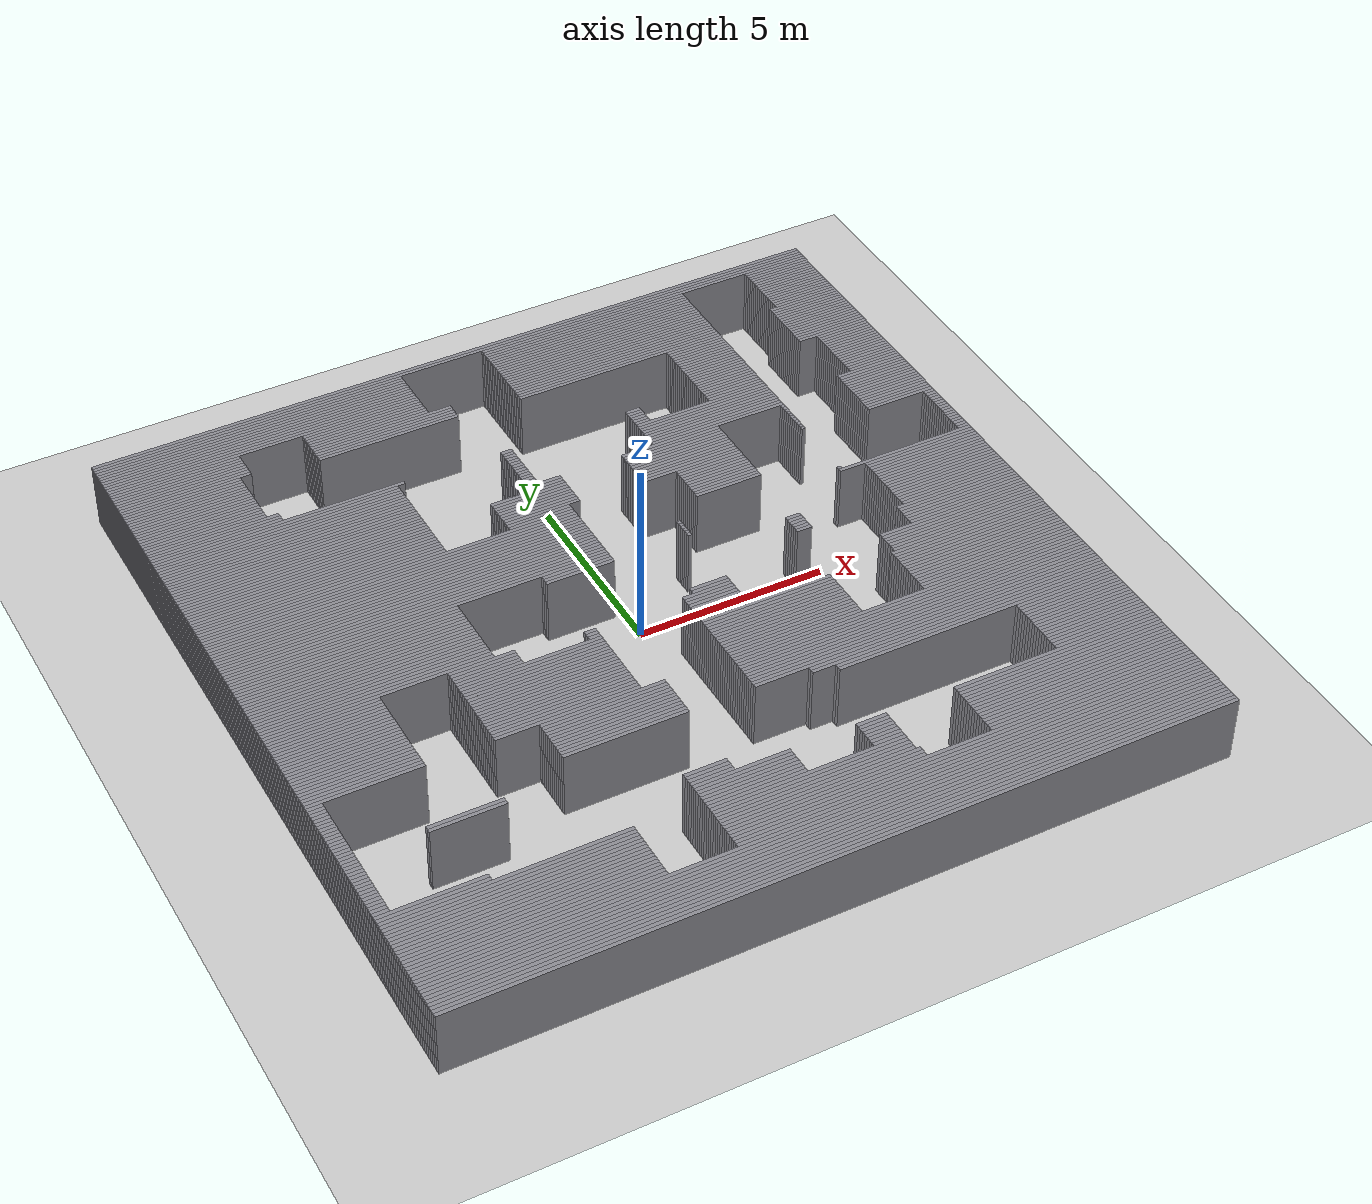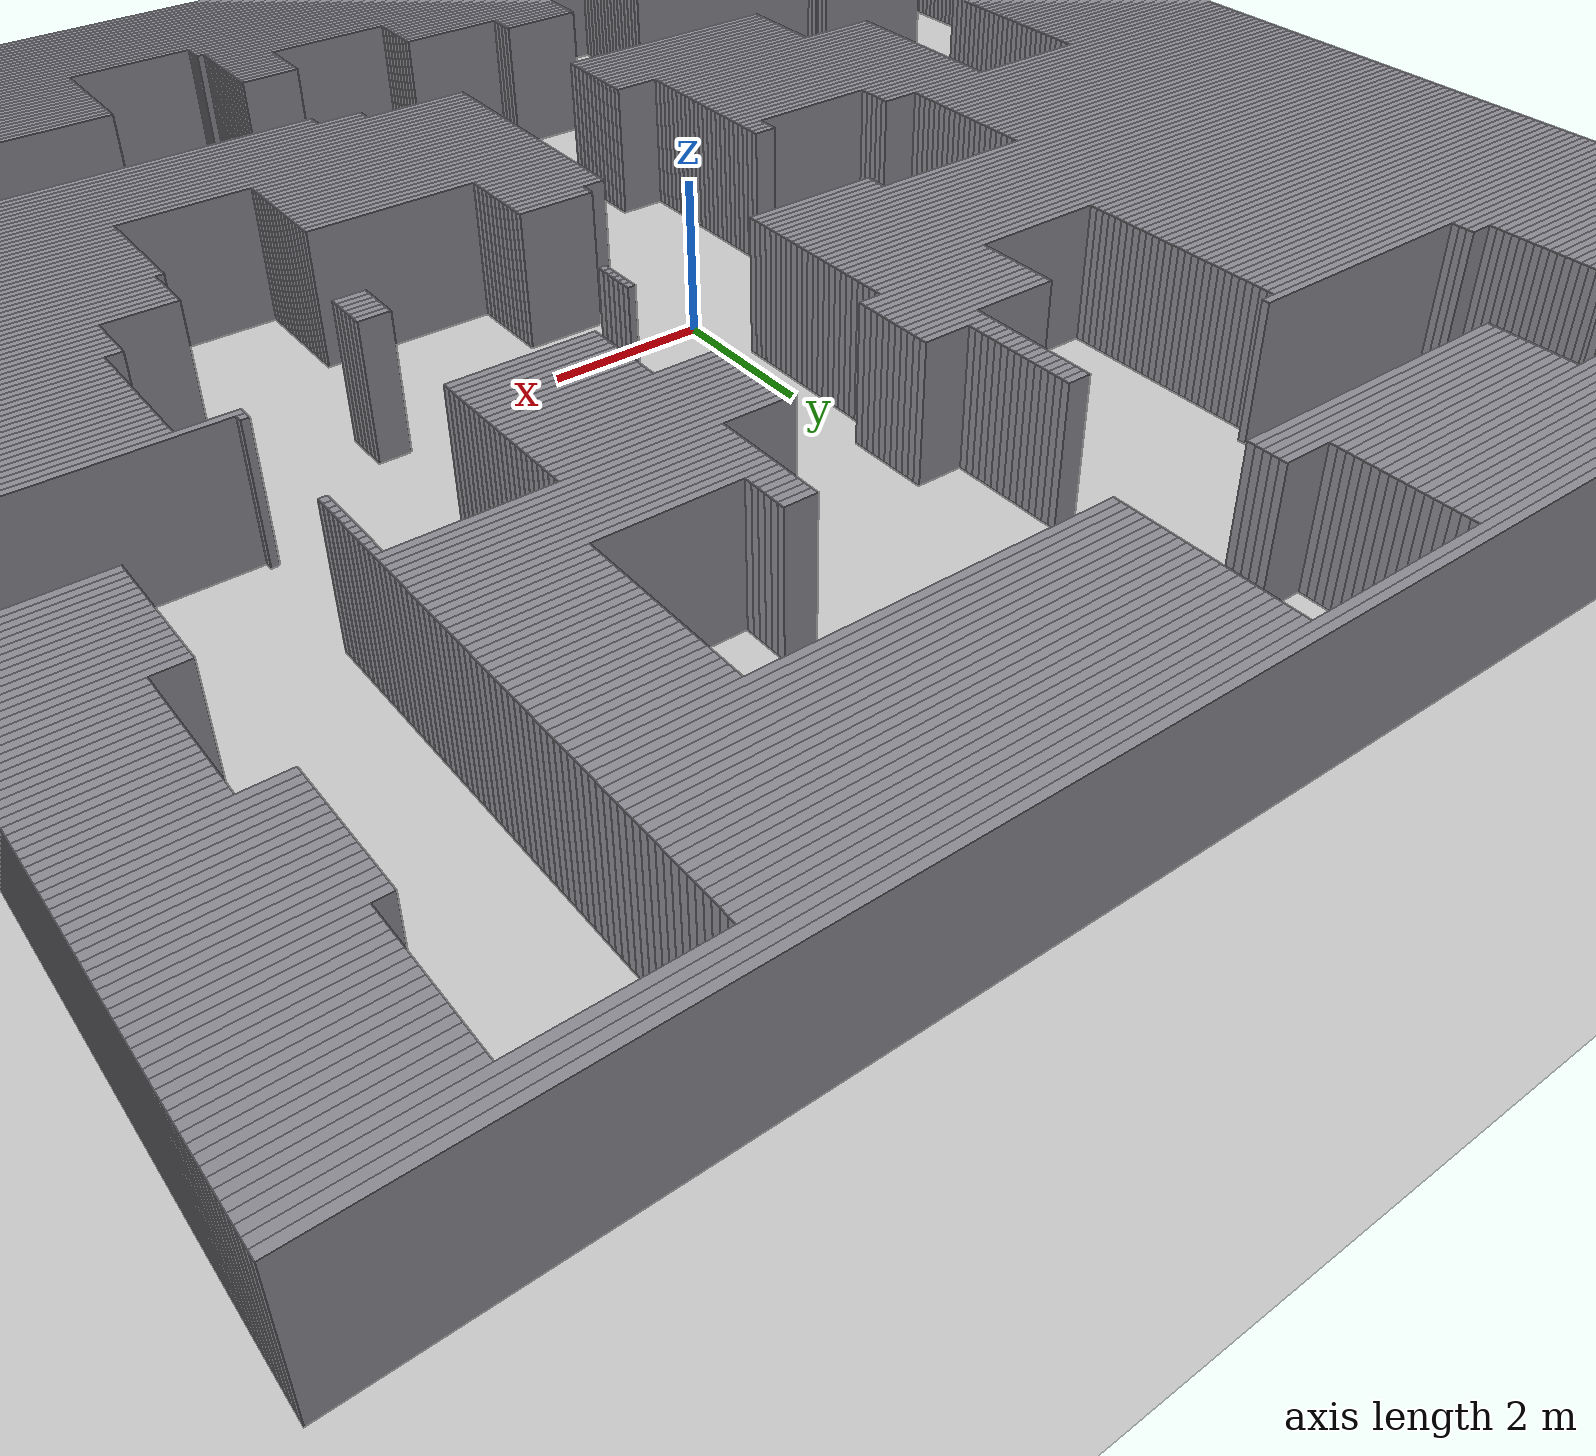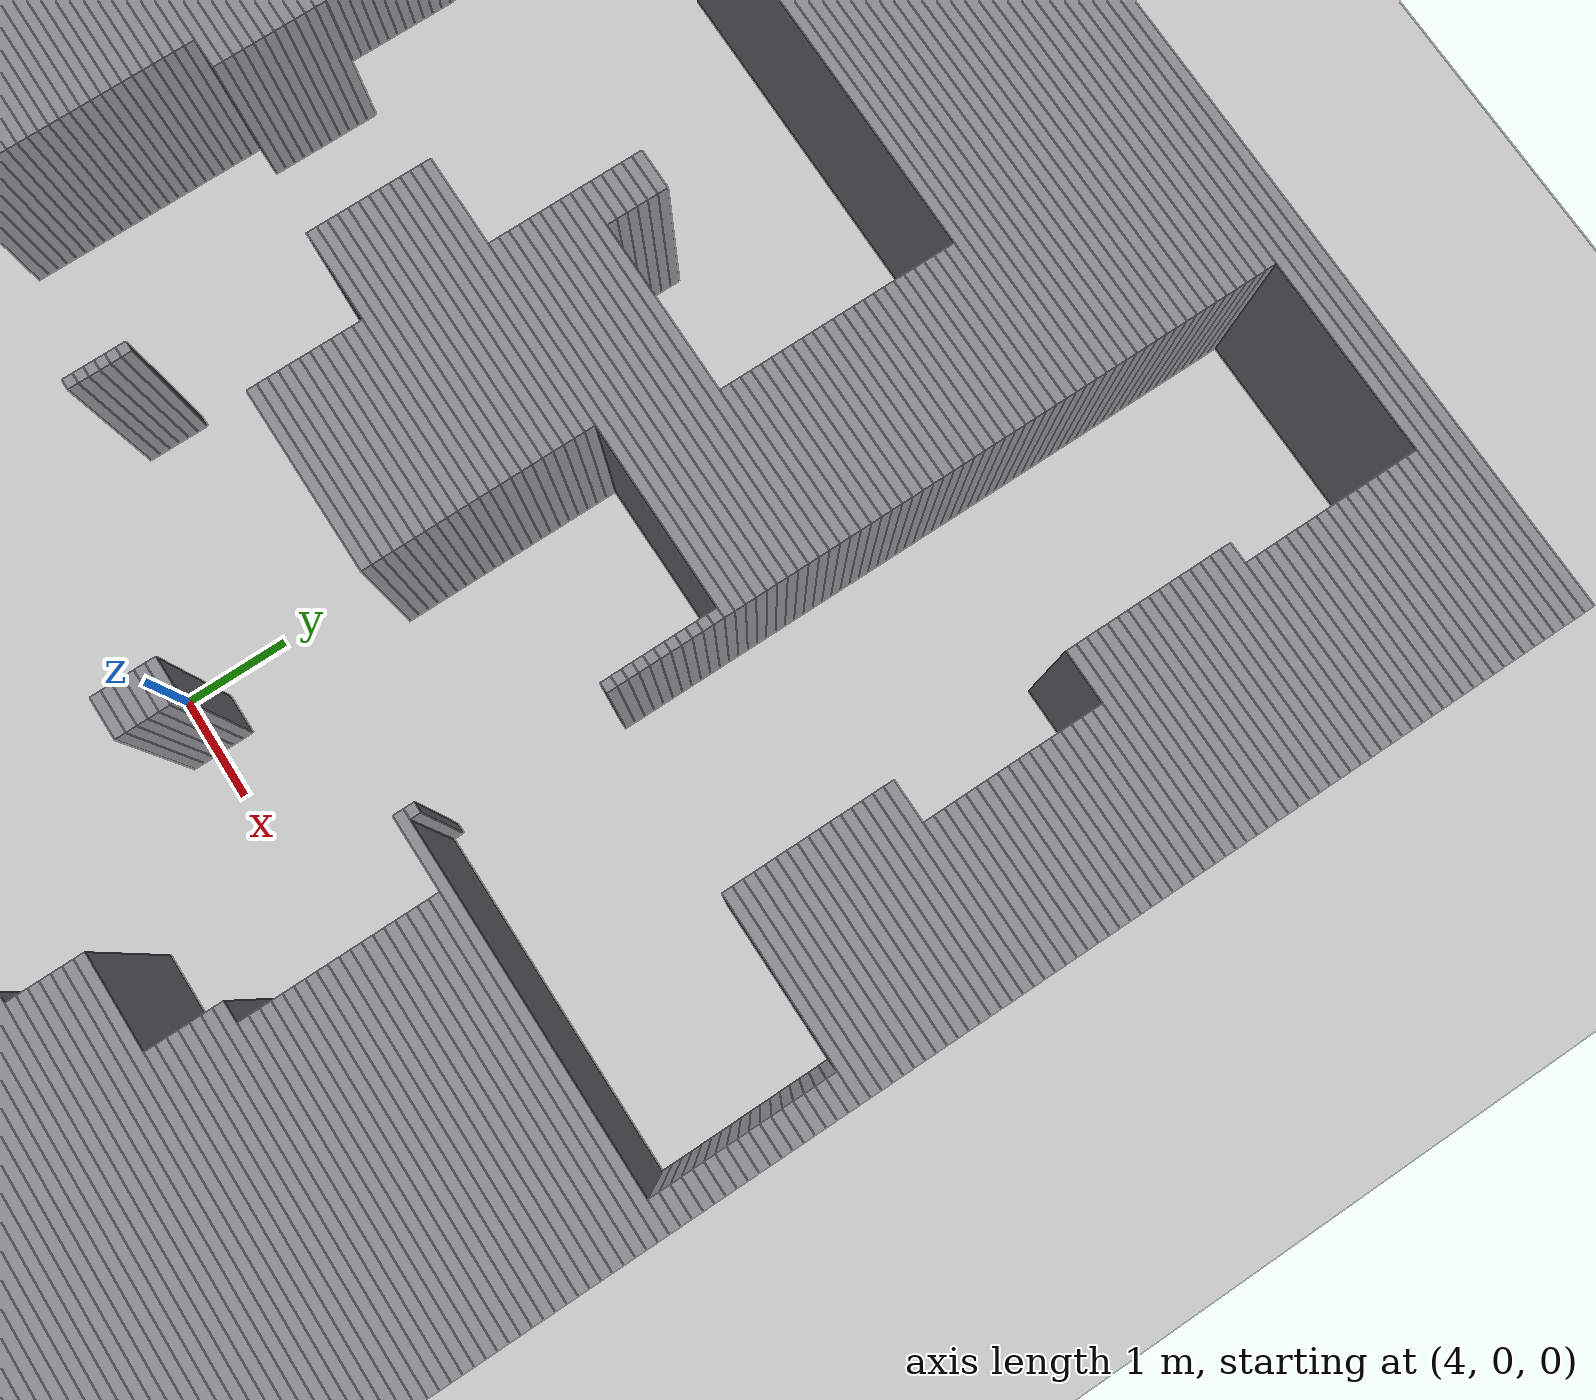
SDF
<?xml version='1.0'?>
<sdf version='1.6'><world name='default'>
  <include><uri>model://sun</uri></include>
  <include><uri>model://ground_plane</uri></include>
  <include><uri>model://dep_car_map_0000_2a91f458</uri></include>
  <physics name='default_physics' type='ode'><max_step_size>0.002</max_step_size><real_time_update_rate>500</real_time_update_rate></physics>
</world></sdf>

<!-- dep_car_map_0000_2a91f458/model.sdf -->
<sdf version='1.6'><model name='dep_car_map_0000_2a91f458'><static>true</static><link name='wall_0'><pose>0.000000 10.000000 0.900000 0 0 0</pose><collision name='collision'><geometry><box><size>20.100000 0.100000 1.800000</size></box></geometry></collision><visual name='visual'><geometry><box><size>20.100000 0.100000 1.800000</size></box></geometry><material><ambient>0.55 0.55 0.58 1</ambient></material></visual></link><link name='wall_1'><pose>0.000000 9.900000 0.900000 0 0 0</pose><collision name='collision'><geometry><box><size>20.100000 0.100000 1.800000</size></box></geometry></collision><visual name='visual'><geometry><box><size>20.100000 0.100000 1.800000</size></box></geometry><material><ambient>0.55 0.55 0.58 1</ambient></material></visual></link><link name='wall_2'><pose>-5.900000 9.800000 0.900000 0 0 0</pose><collision name='collision'><geometry><box><size>8.300000 0.100000 1.800000</size></box></geometry></collision><visual name='visual'><geometry><box><size>8.300000 0.100000 1.800000</size></box></geometry><material><ambient>0.55 0.55 0.58 1</ambient></material></visual></link><link name='wall_3'><pose>5.300000 9.800000 0.900000 0 0 0</pose><collision name='collision'><geometry><box><size>9.500000 0.100000 1.800000</size></box></geometry></collision><visual name='visual'><geometry><box><size>9.500000 0.100000 1.800000</size></box></geometry><material><ambient>0.55 0.55 0.58 1</ambient></material></visual></link><link name='wall_4'><pose>-5.900000 9.700000 0.900000 0 0 0</pose><collision name='collision'><geometry><box><size>8.300000 0.100000 1.800000</size></box></geometry></collision><visual name='visual'><geometry><box><size>8.300000 0.100000 1.800000</size></box></geometry><material><ambient>0.55 0.55 0.58 1</ambient></material></visual></link><link name='wall_5'><pose>5.300000 9.700000 0.900000 0 0 0</pose><collision name='collision'><geometry><box><size>9.500000 0.100000 1.800000</size></box></geometry></collision><visual name='visual'><geometry><box><size>9.500000 0.100000 1.800000</size></box></geometry><material><ambient>0.55 0.55 0.58 1</ambient></material></visual></link><link name='wall_6'><pose>-5.900000 9.600000 0.900000 0 0 0</pose><collision name='collision'><geometry><box><size>8.300000 0.100000 1.800000</size></box></geometry></collision><visual name='visual'><geometry><box><size>8.300000 0.100000 1.800000</size></box></geometry><material><ambient>0.55 0.55 0.58 1</ambient></material></visual></link><link name='wall_7'><pose>3.450000 9.600000 0.900000 0 0 0</pose><collision name='collision'><geometry><box><size>5.800000 0.100000 1.800000</size></box></geometry></collision><visual name='visual'><geometry><box><size>5.800000 0.100000 1.800000</size></box></geometry><material><ambient>0.55 0.55 0.58 1</ambient></material></visual></link><link name='wall_8'><pose>9.150000 9.600000 0.900000 0 0 0</pose><collision name='collision'><geometry><box><size>1.800000 0.100000 1.800000</size></box></geometry></collision><visual name='visual'><geometry><box><size>1.800000 0.100000 1.800000</size></box></geometry><material><ambient>0.55 0.55 0.58 1</ambient></material></visual></link><link name='wall_9'><pose>-5.900000 9.500000 0.900000 0 0 0</pose><collision name='collision'><geometry><box><size>8.300000 0.100000 1.800000</size></box></geometry></collision><visual name='visual'><geometry><box><size>8.300000 0.100000 1.800000</size></box></geometry><material><ambient>0.55 0.55 0.58 1</ambient></material></visual></link><link name='wall_10'><pose>3.450000 9.500000 0.900000 0 0 0</pose><collision name='collision'><geometry><box><size>5.800000 0.100000 1.800000</size></box></geometry></collision><visual name='visual'><geometry><box><size>5.800000 0.100000 1.800000</size></box></geometry><material><ambient>0.55 0.55 0.58 1</ambient></material></visual></link><link name='wall_11'><pose>9.150000 9.500000 0.900000 0 0 0</pose><collision name='collision'><geometry><box><size>1.800000 0.100000 1.800000</size></box></geometry></collision><visual name='visual'><geometry><box><size>1.800000 0.100000 1.800000</size></box></geometry><material><ambient>0.55 0.55 0.58 1</ambient></material></visual></link><link name='wall_12'><pose>-5.900000 9.400000 0.900000 0 0 0</pose><collision name='collision'><geometry><box><size>8.300000 0.100000 1.800000</size></box></geometry></collision><visual name='visual'><geometry><box><size>8.300000 0.100000 1.800000</size></box></geometry><material><ambient>0.55 0.55 0.58 1</ambient></material></visual></link><link name='wall_13'><pose>3.450000 9.400000 0.900000 0 0 0</pose><collision name='collision'><geometry><box><size>5.800000 0.100000 1.800000</size></box></geometry></collision><visual name='visual'><geometry><box><size>5.800000 0.100000 1.800000</size></box></geometry><material><ambient>0.55 0.55 0.58 1</ambient></material></visual></link><link name='wall_14'><pose>9.150000 9.400000 0.900000 0 0 0</pose><collision name='collision'><geometry><box><size>1.800000 0.100000 1.800000</size></box></geometry></collision><visual name='visual'><geometry><box><size>1.800000 0.100000 1.800000</size></box></geometry><material><ambient>0.55 0.55 0.58 1</ambient></material></visual></link><link name='wall_15'><pose>-5.900000 9.300000 0.900000 0 0 0</pose><collision name='collision'><geometry><box><size>8.300000 0.100000 1.800000</size></box></geometry></collision><visual name='visual'><geometry><box><size>8.300000 0.100000 1.800000</size></box></geometry><material><ambient>0.55 0.55 0.58 1</ambient></material></visual></link><link name='wall_16'><pose>3.450000 9.300000 0.900000 0 0 0</pose><collision name='collision'><geometry><box><size>5.800000 0.100000 1.800000</size></box></geometry></collision><visual name='visual'><geometry><box><size>5.800000 0.100000 1.800000</size></box></geometry><material><ambient>0.55 0.55 0.58 1</ambient></material></visual></link><link name='wall_17'><pose>9.150000 9.300000 0.900000 0 0 0</pose><collision name='collision'><geometry><box><size>1.800000 0.100000 1.800000</size></box></geometry></collision><visual name='visual'><geometry><box><size>1.800000 0.100000 1.800000</size></box></geometry><material><ambient>0.55 0.55 0.58 1</ambient></material></visual></link><link name='wall_18'><pose>-5.900000 9.200000 0.900000 0 0 0</pose><collision name='collision'><geometry><box><size>8.300000 0.100000 1.800000</size></box></geometry></collision><visual name='visual'><geometry><box><size>8.300000 0.100000 1.800000</size></box></geometry><material><ambient>0.55 0.55 0.58 1</ambient></material></visual></link><link name='wall_19'><pose>3.450000 9.200000 0.900000 0 0 0</pose><collision name='collision'><geometry><box><size>5.800000 0.100000 1.800000</size></box></geometry></collision><visual name='visual'><geometry><box><size>5.800000 0.100000 1.800000</size></box></geometry><material><ambient>0.55 0.55 0.58 1</ambient></material></visual></link><link name='wall_20'><pose>9.150000 9.200000 0.900000 0 0 0</pose><collision name='collision'><geometry><box><size>1.800000 0.100000 1.800000</size></box></geometry></collision><visual name='visual'><geometry><box><size>1.800000 0.100000 1.800000</size></box></geometry><material><ambient>0.55 0.55 0.58 1</ambient></material></visual></link><link name='wall_21'><pose>-5.900000 9.100000 0.900000 0 0 0</pose><collision name='collision'><geometry><box><size>8.300000 0.100000 1.800000</size></box></geometry></collision><visual name='visual'><geometry><box><size>8.300000 0.100000 1.800000</size></box></geometry><material><ambient>0.55 0.55 0.58 1</ambient></material></visual></link><link name='wall_22'><pose>3.450000 9.100000 0.900000 0 0 0</pose><collision name='collision'><geometry><box><size>5.800000 0.100000 1.800000</size></box></geometry></collision><visual name='visual'><geometry><box><size>5.800000 0.100000 1.800000</size></box></geometry><material><ambient>0.55 0.55 0.58 1</ambient></material></visual></link><link name='wall_23'><pose>9.150000 9.100000 0.900000 0 0 0</pose><collision name='collision'><geometry><box><size>1.800000 0.100000 1.800000</size></box></geometry></collision><visual name='visual'><geometry><box><size>1.800000 0.100000 1.800000</size></box></geometry><material><ambient>0.55 0.55 0.58 1</ambient></material></visual></link><link name='wall_24'><pose>-5.900000 9.000000 0.900000 0 0 0</pose><collision name='collision'><geometry><box><size>8.300000 0.100000 1.800000</size></box></geometry></collision><visual name='visual'><geometry><box><size>8.300000 0.100000 1.800000</size></box></geometry><material><ambient>0.55 0.55 0.58 1</ambient></material></visual></link><link name='wall_25'><pose>3.450000 9.000000 0.900000 0 0 0</pose><collision name='collision'><geometry><box><size>5.800000 0.100000 1.800000</size></box></geometry></collision><visual name='visual'><geometry><box><size>5.800000 0.100000 1.800000</size></box></geometry><material><ambient>0.55 0.55 0.58 1</ambient></material></visual></link><link name='wall_26'><pose>9.150000 9.000000 0.900000 0 0 0</pose><collision name='collision'><geometry><box><size>1.800000 0.100000 1.800000</size></box></geometry></collision><visual name='visual'><geometry><box><size>1.800000 0.100000 1.800000</size></box></geometry><material><ambient>0.55 0.55 0.58 1</ambient></material></visual></link><link name='wall_27'><pose>-5.900000 8.900000 0.900000 0 0 0</pose><collision name='collision'><geometry><box><size>8.300000 0.100000 1.800000</size></box></geometry></collision><visual name='visual'><geometry><box><size>8.300000 0.100000 1.800000</size></box></geometry><material><ambient>0.55 0.55 0.58 1</ambient></material></visual></link><link name='wall_28'><pose>3.450000 8.900000 0.900000 0 0 0</pose><collision name='collision'><geometry><box><size>5.800000 0.100000 1.800000</size></box></geometry></collision><visual name='visual'><geometry><box><size>5.800000 0.100000 1.800000</size></box></geometry><material><ambient>0.55 0.55 0.58 1</ambient></material></visual></link><link name='wall_29'><pose>9.150000 8.900000 0.900000 0 0 0</pose><collision name='collision'><geometry><box><size>1.800000 0.100000 1.800000</size></box></geometry></collision><visual name='visual'><geometry><box><size>1.800000 0.100000 1.800000</size></box></geometry><material><ambient>0.55 0.55 0.58 1</ambient></material></visual></link><link name='wall_30'><pose>-5.900000 8.800000 0.900000 0 0 0</pose><collision name='collision'><geometry><box><size>8.300000 0.100000 1.800000</size></box></geometry></collision><visual name='visual'><geometry><box><size>8.300000 0.100000 1.800000</size></box></geometry><material><ambient>0.55 0.55 0.58 1</ambient></material></visual></link><link name='wall_31'><pose>3.450000 8.800000 0.900000 0 0 0</pose><collision name='collision'><geometry><box><size>5.800000 0.100000 1.800000</size></box></geometry></collision><visual name='visual'><geometry><box><size>5.800000 0.100000 1.800000</size></box></geometry><material><ambient>0.55 0.55 0.58 1</ambient></material></visual></link><link name='wall_32'><pose>9.150000 8.800000 0.900000 0 0 0</pose><collision name='collision'><geometry><box><size>1.800000 0.100000 1.800000</size></box></geometry></collision><visual name='visual'><geometry><box><size>1.800000 0.100000 1.800000</size></box></geometry><material><ambient>0.55 0.55 0.58 1</ambient></material></visual></link><link name='wall_33'><pose>-8.350000 8.700000 0.900000 0 0 0</pose><collision name='collision'><geometry><box><size>3.400000 0.100000 1.800000</size></box></geometry></collision><visual name='visual'><geometry><box><size>3.400000 0.100000 1.800000</size></box></geometry><material><ambient>0.55 0.55 0.58 1</ambient></material></visual></link><link name='wall_34'><pose>-3.350000 8.700000 0.900000 0 0 0</pose><collision name='collision'><geometry><box><size>3.200000 0.100000 1.800000</size></box></geometry></collision><visual name='visual'><geometry><box><size>3.200000 0.100000 1.800000</size></box></geometry><material><ambient>0.55 0.55 0.58 1</ambient></material></visual></link><link name='wall_35'><pose>3.450000 8.700000 0.900000 0 0 0</pose><collision name='collision'><geometry><box><size>5.800000 0.100000 1.800000</size></box></geometry></collision><visual name='visual'><geometry><box><size>5.800000 0.100000 1.800000</size></box></geometry><material><ambient>0.55 0.55 0.58 1</ambient></material></visual></link><link name='wall_36'><pose>9.150000 8.700000 0.900000 0 0 0</pose><collision name='collision'><geometry><box><size>1.800000 0.100000 1.800000</size></box></geometry></collision><visual name='visual'><geometry><box><size>1.800000 0.100000 1.800000</size></box></geometry><material><ambient>0.55 0.55 0.58 1</ambient></material></visual></link><link name='wall_37'><pose>-8.350000 8.600000 0.900000 0 0 0</pose><collision name='collision'><geometry><box><size>3.400000 0.100000 1.800000</size></box></geometry></collision><visual name='visual'><geometry><box><size>3.400000 0.100000 1.800000</size></box></geometry><material><ambient>0.55 0.55 0.58 1</ambient></material></visual></link><link name='wall_38'><pose>-3.350000 8.600000 0.900000 0 0 0</pose><collision name='collision'><geometry><box><size>3.200000 0.100000 1.800000</size></box></geometry></collision><visual name='visual'><geometry><box><size>3.200000 0.100000 1.800000</size></box></geometry><material><ambient>0.55 0.55 0.58 1</ambient></material></visual></link><link name='wall_39'><pose>3.450000 8.600000 0.900000 0 0 0</pose><collision name='collision'><geometry><box><size>5.800000 0.100000 1.800000</size></box></geometry></collision><visual name='visual'><geometry><box><size>5.800000 0.100000 1.800000</size></box></geometry><material><ambient>0.55 0.55 0.58 1</ambient></material></visual></link><link name='wall_40'><pose>9.150000 8.600000 0.900000 0 0 0</pose><collision name='collision'><geometry><box><size>1.800000 0.100000 1.800000</size></box></geometry></collision><visual name='visual'><geometry><box><size>1.800000 0.100000 1.800000</size></box></geometry><material><ambient>0.55 0.55 0.58 1</ambient></material></visual></link><link name='wall_41'><pose>-8.350000 8.500000 0.900000 0 0 0</pose><collision name='collision'><geometry><box><size>3.400000 0.100000 1.800000</size></box></geometry></collision><visual name='visual'><geometry><box><size>3.400000 0.100000 1.800000</size></box></geometry><material><ambient>0.55 0.55 0.58 1</ambient></material></visual></link><link name='wall_42'><pose>-3.350000 8.500000 0.900000 0 0 0</pose><collision name='collision'><geometry><box><size>3.200000 0.100000 1.800000</size></box></geometry></collision><visual name='visual'><geometry><box><size>3.200000 0.100000 1.800000</size></box></geometry><material><ambient>0.55 0.55 0.58 1</ambient></material></visual></link><link name='wall_43'><pose>3.450000 8.500000 0.900000 0 0 0</pose><collision name='collision'><geometry><box><size>5.800000 0.100000 1.800000</size></box></geometry></collision><visual name='visual'><geometry><box><size>5.800000 0.100000 1.800000</size></box></geometry><material><ambient>0.55 0.55 0.58 1</ambient></material></visual></link><link name='wall_44'><pose>9.150000 8.500000 0.900000 0 0 0</pose><collision name='collision'><geometry><box><size>1.800000 0.100000 1.800000</size></box></geometry></collision><visual name='visual'><geometry><box><size>1.800000 0.100000 1.800000</size></box></geometry><material><ambient>0.55 0.55 0.58 1</ambient></material></visual></link><link name='wall_45'><pose>-8.350000 8.400000 0.900000 0 0 0</pose><collision name='collision'><geometry><box><size>3.400000 0.100000 1.800000</size></box></geometry></collision><visual name='visual'><geometry><box><size>3.400000 0.100000 1.800000</size></box></geometry><material><ambient>0.55 0.55 0.58 1</ambient></material></visual></link><link name='wall_46'><pose>-3.350000 8.400000 0.900000 0 0 0</pose><collision name='collision'><geometry><box><size>3.200000 0.100000 1.800000</size></box></geometry></collision><visual name='visual'><geometry><box><size>3.200000 0.100000 1.800000</size></box></geometry><material><ambient>0.55 0.55 0.58 1</ambient></material></visual></link><link name='wall_47'><pose>3.450000 8.400000 0.900000 0 0 0</pose><collision name='collision'><geometry><box><size>5.800000 0.100000 1.800000</size></box></geometry></collision><visual name='visual'><geometry><box><size>5.800000 0.100000 1.800000</size></box></geometry><material><ambient>0.55 0.55 0.58 1</ambient></material></visual></link><link name='wall_48'><pose>9.150000 8.400000 0.900000 0 0 0</pose><collision name='collision'><geometry><box><size>1.800000 0.100000 1.800000</size></box></geometry></collision><visual name='visual'><geometry><box><size>1.800000 0.100000 1.800000</size></box></geometry><material><ambient>0.55 0.55 0.58 1</ambient></material></visual></link><link name='wall_49'><pose>-8.350000 8.300000 0.900000 0 0 0</pose><collision name='collision'><geometry><box><size>3.400000 0.100000 1.800000</size></box></geometry></collision><visual name='visual'><geometry><box><size>3.400000 0.100000 1.800000</size></box></geometry><material><ambient>0.55 0.55 0.58 1</ambient></material></visual></link><link name='wall_50'><pose>-3.350000 8.300000 0.900000 0 0 0</pose><collision name='collision'><geometry><box><size>3.200000 0.100000 1.800000</size></box></geometry></collision><visual name='visual'><geometry><box><size>3.200000 0.100000 1.800000</size></box></geometry><material><ambient>0.55 0.55 0.58 1</ambient></material></visual></link><link name='wall_51'><pose>3.450000 8.300000 0.900000 0 0 0</pose><collision name='collision'><geometry><box><size>5.800000 0.100000 1.800000</size></box></geometry></collision><visual name='visual'><geometry><box><size>5.800000 0.100000 1.800000</size></box></geometry><material><ambient>0.55 0.55 0.58 1</ambient></material></visual></link><link name='wall_52'><pose>9.150000 8.300000 0.900000 0 0 0</pose><collision name='collision'><geometry><box><size>1.800000 0.100000 1.800000</size></box></geometry></collision><visual name='visual'><geometry><box><size>1.800000 0.100000 1.800000</size></box></geometry><material><ambient>0.55 0.55 0.58 1</ambient></material></visual></link><link name='wall_53'><pose>-8.350000 8.200000 0.900000 0 0 0</pose><collision name='collision'><geometry><box><size>3.400000 0.100000 1.800000</size></box></geometry></collision><visual name='visual'><geometry><box><size>3.400000 0.100000 1.800000</size></box></geometry><material><ambient>0.55 0.55 0.58 1</ambient></material></visual></link><link name='wall_54'><pose>-3.350000 8.200000 0.900000 0 0 0</pose><collision name='collision'><geometry><box><size>3.200000 0.100000 1.800000</size></box></geometry></collision><visual name='visual'><geometry><box><size>3.200000 0.100000 1.800000</size></box></geometry><material><ambient>0.55 0.55 0.58 1</ambient></material></visual></link><link name='wall_55'><pose>3.450000 8.200000 0.900000 0 0 0</pose><collision name='collision'><geometry><box><size>5.800000 0.100000 1.800000</size></box></geometry></collision><visual name='visual'><geometry><box><size>5.800000 0.100000 1.800000</size></box></geometry><material><ambient>0.55 0.55 0.58 1</ambient></material></visual></link><link name='wall_56'><pose>9.150000 8.200000 0.900000 0 0 0</pose><collision name='collision'><geometry><box><size>1.800000 0.100000 1.800000</size></box></geometry></collision><visual name='visual'><geometry><box><size>1.800000 0.100000 1.800000</size></box></geometry><material><ambient>0.55 0.55 0.58 1</ambient></material></visual></link><link name='wall_57'><pose>-8.350000 8.100000 0.900000 0 0 0</pose><collision name='collision'><geometry><box><size>3.400000 0.100000 1.800000</size></box></geometry></collision><visual name='visual'><geometry><box><size>3.400000 0.100000 1.800000</size></box></geometry><material><ambient>0.55 0.55 0.58 1</ambient></material></visual></link><link name='wall_58'><pose>-3.050000 8.100000 0.900000 0 0 0</pose><collision name='collision'><geometry><box><size>3.800000 0.100000 1.800000</size></box></geometry></collision><visual name='visual'><geometry><box><size>3.800000 0.100000 1.800000</size></box></geometry><material><ambient>0.55 0.55 0.58 1</ambient></material></visual></link><link name='wall_59'><pose>3.450000 8.100000 0.900000 0 0 0</pose><collision name='collision'><geometry><box><size>5.800000 0.100000 1.800000</size></box></geometry></collision><visual name='visual'><geometry><box><size>5.800000 0.100000 1.800000</size></box></geometry><material><ambient>0.55 0.55 0.58 1</ambient></material></visual></link><link name='wall_60'><pose>9.150000 8.100000 0.900000 0 0 0</pose><collision name='collision'><geometry><box><size>1.800000 0.100000 1.800000</size></box></geometry></collision><visual name='visual'><geometry><box><size>1.800000 0.100000 1.800000</size></box></geometry><material><ambient>0.55 0.55 0.58 1</ambient></material></visual></link><link name='wall_61'><pose>-8.350000 8.000000 0.900000 0 0 0</pose><collision name='collision'><geometry><box><size>3.400000 0.100000 1.800000</size></box></geometry></collision><visual name='visual'><geometry><box><size>3.400000 0.100000 1.800000</size></box></geometry><material><ambient>0.55 0.55 0.58 1</ambient></material></visual></link><link name='wall_62'><pose>-3.050000 8.000000 0.900000 0 0 0</pose><collision name='collision'><geometry><box><size>3.800000 0.100000 1.800000</size></box></geometry></collision><visual name='visual'><geometry><box><size>3.800000 0.100000 1.800000</size></box></geometry><material><ambient>0.55 0.55 0.58 1</ambient></material></visual></link><link name='wall_63'><pose>3.450000 8.000000 0.900000 0 0 0</pose><collision name='collision'><geometry><box><size>5.800000 0.100000 1.800000</size></box></geometry></collision><visual name='visual'><geometry><box><size>5.800000 0.100000 1.800000</size></box></geometry><material><ambient>0.55 0.55 0.58 1</ambient></material></visual></link><link name='wall_64'><pose>9.150000 8.000000 0.900000 0 0 0</pose><collision name='collision'><geometry><box><size>1.800000 0.100000 1.800000</size></box></geometry></collision><visual name='visual'><geometry><box><size>1.800000 0.100000 1.800000</size></box></geometry><material><ambient>0.55 0.55 0.58 1</ambient></material></visual></link><link name='wall_65'><pose>-8.500000 7.900000 0.900000 0 0 0</pose><collision name='collision'><geometry><box><size>3.100000 0.100000 1.800000</size></box></geometry></collision><visual name='visual'><geometry><box><size>3.100000 0.100000 1.800000</size></box></geometry><material><ambient>0.55 0.55 0.58 1</ambient></material></visual></link><link name='wall_66'><pose>-3.050000 7.900000 0.900000 0 0 0</pose><collision name='collision'><geometry><box><size>3.800000 0.100000 1.800000</size></box></geometry></collision><visual name='visual'><geometry><box><size>3.800000 0.100000 1.800000</size></box></geometry><material><ambient>0.55 0.55 0.58 1</ambient></material></visual></link><link name='wall_67'><pose>3.450000 7.900000 0.900000 0 0 0</pose><collision name='collision'><geometry><box><size>5.800000 0.100000 1.800000</size></box></geometry></collision><visual name='visual'><geometry><box><size>5.800000 0.100000 1.800000</size></box></geometry><material><ambient>0.55 0.55 0.58 1</ambient></material></visual></link><link name='wall_68'><pose>9.050000 7.900000 0.900000 0 0 0</pose><collision name='collision'><geometry><box><size>2.000000 0.100000 1.800000</size></box></geometry></collision><visual name='visual'><geometry><box><size>2.000000 0.100000 1.800000</size></box></geometry><material><ambient>0.55 0.55 0.58 1</ambient></material></visual></link><link name='wall_69'><pose>-8.500000 7.800000 0.900000 0 0 0</pose><collision name='collision'><geometry><box><size>3.100000 0.100000 1.800000</size></box></geometry></collision><visual name='visual'><geometry><box><size>3.100000 0.100000 1.800000</size></box></geometry><material><ambient>0.55 0.55 0.58 1</ambient></material></visual></link><link name='wall_70'><pose>-3.050000 7.800000 0.900000 0 0 0</pose><collision name='collision'><geometry><box><size>3.800000 0.100000 1.800000</size></box></geometry></collision><visual name='visual'><geometry><box><size>3.800000 0.100000 1.800000</size></box></geometry><material><ambient>0.55 0.55 0.58 1</ambient></material></visual></link><link name='wall_71'><pose>3.450000 7.800000 0.900000 0 0 0</pose><collision name='collision'><geometry><box><size>5.800000 0.100000 1.800000</size></box></geometry></collision><visual name='visual'><geometry><box><size>5.800000 0.100000 1.800000</size></box></geometry><material><ambient>0.55 0.55 0.58 1</ambient></material></visual></link><link name='wall_72'><pose>9.050000 7.800000 0.900000 0 0 0</pose><collision name='collision'><geometry><box><size>2.000000 0.100000 1.800000</size></box></geometry></collision><visual name='visual'><geometry><box><size>2.000000 0.100000 1.800000</size></box></geometry><material><ambient>0.55 0.55 0.58 1</ambient></material></visual></link><link name='wall_73'><pose>-8.500000 7.700000 0.900000 0 0 0</pose><collision name='collision'><geometry><box><size>3.100000 0.100000 1.800000</size></box></geometry></collision><visual name='visual'><geometry><box><size>3.100000 0.100000 1.800000</size></box></geometry><material><ambient>0.55 0.55 0.58 1</ambient></material></visual></link><link name='wall_74'><pose>-3.050000 7.700000 0.900000 0 0 0</pose><collision name='collision'><geometry><box><size>3.800000 0.100000 1.800000</size></box></geometry></collision><visual name='visual'><geometry><box><size>3.800000 0.100000 1.800000</size></box></geometry><material><ambient>0.55 0.55 0.58 1</ambient></material></visual></link><link name='wall_75'><pose>3.450000 7.700000 0.900000 0 0 0</pose><collision name='collision'><geometry><box><size>5.800000 0.100000 1.800000</size></box></geometry></collision><visual name='visual'><geometry><box><size>5.800000 0.100000 1.800000</size></box></geometry><material><ambient>0.55 0.55 0.58 1</ambient></material></visual></link><link name='wall_76'><pose>9.050000 7.700000 0.900000 0 0 0</pose><collision name='collision'><geometry><box><size>2.000000 0.100000 1.800000</size></box></geometry></collision><visual name='visual'><geometry><box><size>2.000000 0.100000 1.800000</size></box></geometry><material><ambient>0.55 0.55 0.58 1</ambient></material></visual></link><link name='wall_77'><pose>-8.500000 7.600000 0.900000 0 0 0</pose><collision name='collision'><geometry><box><size>3.100000 0.100000 1.800000</size></box></geometry></collision><visual name='visual'><geometry><box><size>3.100000 0.100000 1.800000</size></box></geometry><material><ambient>0.55 0.55 0.58 1</ambient></material></visual></link><link name='wall_78'><pose>3.450000 7.600000 0.900000 0 0 0</pose><collision name='collision'><geometry><box><size>5.800000 0.100000 1.800000</size></box></geometry></collision><visual name='visual'><geometry><box><size>5.800000 0.100000 1.800000</size></box></geometry><material><ambient>0.55 0.55 0.58 1</ambient></material></visual></link><link name='wall_79'><pose>9.050000 7.600000 0.900000 0 0 0</pose><collision name='collision'><geometry><box><size>2.000000 0.100000 1.800000</size></box></geometry></collision><visual name='visual'><geometry><box><size>2.000000 0.100000 1.800000</size></box></geometry><material><ambient>0.55 0.55 0.58 1</ambient></material></visual></link><link name='wall_80'><pose>-8.500000 7.500000 0.900000 0 0 0</pose><collision name='collision'><geometry><box><size>3.100000 0.100000 1.800000</size></box></geometry></collision><visual name='visual'><geometry><box><size>3.100000 0.100000 1.800000</size></box></geometry><material><ambient>0.55 0.55 0.58 1</ambient></material></visual></link><link name='wall_81'><pose>5.550000 7.500000 0.900000 0 0 0</pose><collision name='collision'><geometry><box><size>1.600000 0.100000 1.800000</size></box></geometry></collision><visual name='visual'><geometry><box><size>1.600000 0.100000 1.800000</size></box></geometry><material><ambient>0.55 0.55 0.58 1</ambient></material></visual></link><link name='wall_82'><pose>9.050000 7.500000 0.900000 0 0 0</pose><collision name='collision'><geometry><box><size>2.000000 0.100000 1.800000</size></box></geometry></collision><visual name='visual'><geometry><box><size>2.000000 0.100000 1.800000</size></box></geometry><material><ambient>0.55 0.55 0.58 1</ambient></material></visual></link><link name='wall_83'><pose>-8.500000 7.400000 0.900000 0 0 0</pose><collision name='collision'><geometry><box><size>3.100000 0.100000 1.800000</size></box></geometry></collision><visual name='visual'><geometry><box><size>3.100000 0.100000 1.800000</size></box></geometry><material><ambient>0.55 0.55 0.58 1</ambient></material></visual></link><link name='wall_84'><pose>5.550000 7.400000 0.900000 0 0 0</pose><collision name='collision'><geometry><box><size>1.600000 0.100000 1.800000</size></box></geometry></collision><visual name='visual'><geometry><box><size>1.600000 0.100000 1.800000</size></box></geometry><material><ambient>0.55 0.55 0.58 1</ambient></material></visual></link><link name='wall_85'><pose>9.050000 7.400000 0.900000 0 0 0</pose><collision name='collision'><geometry><box><size>2.000000 0.100000 1.800000</size></box></geometry></collision><visual name='visual'><geometry><box><size>2.000000 0.100000 1.800000</size></box></geometry><material><ambient>0.55 0.55 0.58 1</ambient></material></visual></link><link name='wall_86'><pose>-8.500000 7.300000 0.900000 0 0 0</pose><collision name='collision'><geometry><box><size>3.100000 0.100000 1.800000</size></box></geometry></collision><visual name='visual'><geometry><box><size>3.100000 0.100000 1.800000</size></box></geometry><material><ambient>0.55 0.55 0.58 1</ambient></material></visual></link><link name='wall_87'><pose>5.550000 7.300000 0.900000 0 0 0</pose><collision name='collision'><geometry><box><size>1.600000 0.100000 1.800000</size></box></geometry></collision><visual name='visual'><geometry><box><size>1.600000 0.100000 1.800000</size></box></geometry><material><ambient>0.55 0.55 0.58 1</ambient></material></visual></link><link name='wall_88'><pose>9.050000 7.300000 0.900000 0 0 0</pose><collision name='collision'><geometry><box><size>2.000000 0.100000 1.800000</size></box></geometry></collision><visual name='visual'><geometry><box><size>2.000000 0.100000 1.800000</size></box></geometry><material><ambient>0.55 0.55 0.58 1</ambient></material></visual></link><link name='wall_89'><pose>-8.500000 7.200000 0.900000 0 0 0</pose><collision name='collision'><geometry><box><size>3.100000 0.100000 1.800000</size></box></geometry></collision><visual name='visual'><geometry><box><size>3.100000 0.100000 1.800000</size></box></geometry><material><ambient>0.55 0.55 0.58 1</ambient></material></visual></link><link name='wall_90'><pose>5.550000 7.200000 0.900000 0 0 0</pose><collision name='collision'><geometry><box><size>1.600000 0.100000 1.800000</size></box></geometry></collision><visual name='visual'><geometry><box><size>1.600000 0.100000 1.800000</size></box></geometry><material><ambient>0.55 0.55 0.58 1</ambient></material></visual></link><link name='wall_91'><pose>9.050000 7.200000 0.900000 0 0 0</pose><collision name='collision'><geometry><box><size>2.000000 0.100000 1.800000</size></box></geometry></collision><visual name='visual'><geometry><box><size>2.000000 0.100000 1.800000</size></box></geometry><material><ambient>0.55 0.55 0.58 1</ambient></material></visual></link><link name='wall_92'><pose>-8.500000 7.100000 0.900000 0 0 0</pose><collision name='collision'><geometry><box><size>3.100000 0.100000 1.800000</size></box></geometry></collision><visual name='visual'><geometry><box><size>3.100000 0.100000 1.800000</size></box></geometry><material><ambient>0.55 0.55 0.58 1</ambient></material></visual></link><link name='wall_93'><pose>5.550000 7.100000 0.900000 0 0 0</pose><collision name='collision'><geometry><box><size>1.600000 0.100000 1.800000</size></box></geometry></collision><visual name='visual'><geometry><box><size>1.600000 0.100000 1.800000</size></box></geometry><material><ambient>0.55 0.55 0.58 1</ambient></material></visual></link><link name='wall_94'><pose>9.050000 7.100000 0.900000 0 0 0</pose><collision name='collision'><geometry><box><size>2.000000 0.100000 1.800000</size></box></geometry></collision><visual name='visual'><geometry><box><size>2.000000 0.100000 1.800000</size></box></geometry><material><ambient>0.55 0.55 0.58 1</ambient></material></visual></link><link name='wall_95'><pose>-8.500000 7.000000 0.900000 0 0 0</pose><collision name='collision'><geometry><box><size>3.100000 0.100000 1.800000</size></box></geometry></collision><visual name='visual'><geometry><box><size>3.100000 0.100000 1.800000</size></box></geometry><material><ambient>0.55 0.55 0.58 1</ambient></material></visual></link><link name='wall_96'><pose>5.550000 7.000000 0.900000 0 0 0</pose><collision name='collision'><geometry><box><size>1.600000 0.100000 1.800000</size></box></geometry></collision><visual name='visual'><geometry><box><size>1.600000 0.100000 1.800000</size></box></geometry><material><ambient>0.55 0.55 0.58 1</ambient></material></visual></link><link name='wall_97'><pose>9.050000 7.000000 0.900000 0 0 0</pose><collision name='collision'><geometry><box><size>2.000000 0.100000 1.800000</size></box></geometry></collision><visual name='visual'><geometry><box><size>2.000000 0.100000 1.800000</size></box></geometry><material><ambient>0.55 0.55 0.58 1</ambient></material></visual></link><link name='wall_98'><pose>-8.500000 6.900000 0.900000 0 0 0</pose><collision name='collision'><geometry><box><size>3.100000 0.100000 1.800000</size></box></geometry></collision><visual name='visual'><geometry><box><size>3.100000 0.100000 1.800000</size></box></geometry><material><ambient>0.55 0.55 0.58 1</ambient></material></visual></link><link name='wall_99'><pose>5.550000 6.900000 0.900000 0 0 0</pose><collision name='collision'><geometry><box><size>1.600000 0.100000 1.800000</size></box></geometry></collision><visual name='visual'><geometry><box><size>1.600000 0.100000 1.800000</size></box></geometry><material><ambient>0.55 0.55 0.58 1</ambient></material></visual></link><link name='wall_100'><pose>9.050000 6.900000 0.900000 0 0 0</pose><collision name='collision'><geometry><box><size>2.000000 0.100000 1.800000</size></box></geometry></collision><visual name='visual'><geometry><box><size>2.000000 0.100000 1.800000</size></box></geometry><material><ambient>0.55 0.55 0.58 1</ambient></material></visual></link><link name='wall_101'><pose>-8.500000 6.800000 0.900000 0 0 0</pose><collision name='collision'><geometry><box><size>3.100000 0.100000 1.800000</size></box></geometry></collision><visual name='visual'><geometry><box><size>3.100000 0.100000 1.800000</size></box></geometry><material><ambient>0.55 0.55 0.58 1</ambient></material></visual></link><link name='wall_102'><pose>5.550000 6.800000 0.900000 0 0 0</pose><collision name='collision'><geometry><box><size>1.600000 0.100000 1.800000</size></box></geometry></collision><visual name='visual'><geometry><box><size>1.600000 0.100000 1.800000</size></box></geometry><material><ambient>0.55 0.55 0.58 1</ambient></material></visual></link><link name='wall_103'><pose>9.050000 6.800000 0.900000 0 0 0</pose><collision name='collision'><geometry><box><size>2.000000 0.100000 1.800000</size></box></geometry></collision><visual name='visual'><geometry><box><size>2.000000 0.100000 1.800000</size></box></geometry><material><ambient>0.55 0.55 0.58 1</ambient></material></visual></link><link name='wall_104'><pose>-8.500000 6.700000 0.900000 0 0 0</pose><collision name='collision'><geometry><box><size>3.100000 0.100000 1.800000</size></box></geometry></collision><visual name='visual'><geometry><box><size>3.100000 0.100000 1.800000</size></box></geometry><material><ambient>0.55 0.55 0.58 1</ambient></material></visual></link><link name='wall_105'><pose>5.550000 6.700000 0.900000 0 0 0</pose><collision name='collision'><geometry><box><size>1.600000 0.100000 1.800000</size></box></geometry></collision><visual name='visual'><geometry><box><size>1.600000 0.100000 1.800000</size></box></geometry><material><ambient>0.55 0.55 0.58 1</ambient></material></visual></link><link name='wall_106'><pose>9.050000 6.700000 0.900000 0 0 0</pose><collision name='collision'><geometry><box><size>2.000000 0.100000 1.800000</size></box></geometry></collision><visual name='visual'><geometry><box><size>2.000000 0.100000 1.800000</size></box></geometry><material><ambient>0.55 0.55 0.58 1</ambient></material></visual></link><link name='wall_107'><pose>-8.500000 6.600000 0.900000 0 0 0</pose><collision name='collision'><geometry><box><size>3.100000 0.100000 1.800000</size></box></geometry></collision><visual name='visual'><geometry><box><size>3.100000 0.100000 1.800000</size></box></geometry><material><ambient>0.55 0.55 0.58 1</ambient></material></visual></link><link name='wall_108'><pose>5.550000 6.600000 0.900000 0 0 0</pose><collision name='collision'><geometry><box><size>1.600000 0.100000 1.800000</size></box></geometry></collision><visual name='visual'><geometry><box><size>1.600000 0.100000 1.800000</size></box></geometry><material><ambient>0.55 0.55 0.58 1</ambient></material></visual></link><link name='wall_109'><pose>9.050000 6.600000 0.900000 0 0 0</pose><collision name='collision'><geometry><box><size>2.000000 0.100000 1.800000</size></box></geometry></collision><visual name='visual'><geometry><box><size>2.000000 0.100000 1.800000</size></box></geometry><material><ambient>0.55 0.55 0.58 1</ambient></material></visual></link><link name='wall_110'><pose>-8.500000 6.500000 0.900000 0 0 0</pose><collision name='collision'><geometry><box><size>3.100000 0.100000 1.800000</size></box></geometry></collision><visual name='visual'><geometry><box><size>3.100000 0.100000 1.800000</size></box></geometry><material><ambient>0.55 0.55 0.58 1</ambient></material></visual></link><link name='wall_111'><pose>5.550000 6.500000 0.900000 0 0 0</pose><collision name='collision'><geometry><box><size>1.600000 0.100000 1.800000</size></box></geometry></collision><visual name='visual'><geometry><box><size>1.600000 0.100000 1.800000</size></box></geometry><material><ambient>0.55 0.55 0.58 1</ambient></material></visual></link><link name='wall_112'><pose>9.050000 6.500000 0.900000 0 0 0</pose><collision name='collision'><geometry><box><size>2.000000 0.100000 1.800000</size></box></geometry></collision><visual name='visual'><geometry><box><size>2.000000 0.100000 1.800000</size></box></geometry><material><ambient>0.55 0.55 0.58 1</ambient></material></visual></link><link name='wall_113'><pose>-8.500000 6.400000 0.900000 0 0 0</pose><collision name='collision'><geometry><box><size>3.100000 0.100000 1.800000</size></box></geometry></collision><visual name='visual'><geometry><box><size>3.100000 0.100000 1.800000</size></box></geometry><material><ambient>0.55 0.55 0.58 1</ambient></material></visual></link><link name='wall_114'><pose>5.550000 6.400000 0.900000 0 0 0</pose><collision name='collision'><geometry><box><size>1.600000 0.100000 1.800000</size></box></geometry></collision><visual name='visual'><geometry><box><size>1.600000 0.100000 1.800000</size></box></geometry><material><ambient>0.55 0.55 0.58 1</ambient></material></visual></link><link name='wall_115'><pose>9.050000 6.400000 0.900000 0 0 0</pose><collision name='collision'><geometry><box><size>2.000000 0.100000 1.800000</size></box></geometry></collision><visual name='visual'><geometry><box><size>2.000000 0.100000 1.800000</size></box></geometry><material><ambient>0.55 0.55 0.58 1</ambient></material></visual></link><link name='wall_116'><pose>-8.500000 6.300000 0.900000 0 0 0</pose><collision name='collision'><geometry><box><size>3.100000 0.100000 1.800000</size></box></geometry></collision><visual name='visual'><geometry><box><size>3.100000 0.100000 1.800000</size></box></geometry><material><ambient>0.55 0.55 0.58 1</ambient></material></visual></link><link name='wall_117'><pose>5.550000 6.300000 0.900000 0 0 0</pose><collision name='collision'><geometry><box><size>1.600000 0.100000 1.800000</size></box></geometry></collision><visual name='visual'><geometry><box><size>1.600000 0.100000 1.800000</size></box></geometry><material><ambient>0.55 0.55 0.58 1</ambient></material></visual></link><link name='wall_118'><pose>9.300000 6.300000 0.900000 0 0 0</pose><collision name='collision'><geometry><box><size>1.500000 0.100000 1.800000</size></box></geometry></collision><visual name='visual'><geometry><box><size>1.500000 0.100000 1.800000</size></box></geometry><material><ambient>0.55 0.55 0.58 1</ambient></material></visual></link><link name='wall_119'><pose>-8.350000 6.200000 0.900000 0 0 0</pose><collision name='collision'><geometry><box><size>3.400000 0.100000 1.800000</size></box></geometry></collision><visual name='visual'><geometry><box><size>3.400000 0.100000 1.800000</size></box></geometry><material><ambient>0.55 0.55 0.58 1</ambient></material></visual></link><link name='wall_120'><pose>5.550000 6.200000 0.900000 0 0 0</pose><collision name='collision'><geometry><box><size>1.600000 0.100000 1.800000</size></box></geometry></collision><visual name='visual'><geometry><box><size>1.600000 0.100000 1.800000</size></box></geometry><material><ambient>0.55 0.55 0.58 1</ambient></material></visual></link><link name='wall_121'><pose>9.300000 6.200000 0.900000 0 0 0</pose><collision name='collision'><geometry><box><size>1.500000 0.100000 1.800000</size></box></geometry></collision><visual name='visual'><geometry><box><size>1.500000 0.100000 1.800000</size></box></geometry><material><ambient>0.55 0.55 0.58 1</ambient></material></visual></link><link name='wall_122'><pose>-8.350000 6.100000 0.900000 0 0 0</pose><collision name='collision'><geometry><box><size>3.400000 0.100000 1.800000</size></box></geometry></collision><visual name='visual'><geometry><box><size>3.400000 0.100000 1.800000</size></box></geometry><material><ambient>0.55 0.55 0.58 1</ambient></material></visual></link><link name='wall_123'><pose>5.550000 6.100000 0.900000 0 0 0</pose><collision name='collision'><geometry><box><size>1.600000 0.100000 1.800000</size></box></geometry></collision><visual name='visual'><geometry><box><size>1.600000 0.100000 1.800000</size></box></geometry><material><ambient>0.55 0.55 0.58 1</ambient></material></visual></link><link name='wall_124'><pose>9.300000 6.100000 0.900000 0 0 0</pose><collision name='collision'><geometry><box><size>1.500000 0.100000 1.800000</size></box></geometry></collision><visual name='visual'><geometry><box><size>1.500000 0.100000 1.800000</size></box></geometry><material><ambient>0.55 0.55 0.58 1</ambient></material></visual></link><link name='wall_125'><pose>-8.350000 6.000000 0.900000 0 0 0</pose><collision name='collision'><geometry><box><size>3.400000 0.100000 1.800000</size></box></geometry></collision><visual name='visual'><geometry><box><size>3.400000 0.100000 1.800000</size></box></geometry><material><ambient>0.55 0.55 0.58 1</ambient></material></visual></link><link name='wall_126'><pose>5.550000 6.000000 0.900000 0 0 0</pose><collision name='collision'><geometry><box><size>1.600000 0.100000 1.800000</size></box></geometry></collision><visual name='visual'><geometry><box><size>1.600000 0.100000 1.800000</size></box></geometry><material><ambient>0.55 0.55 0.58 1</ambient></material></visual></link><link name='wall_127'><pose>9.300000 6.000000 0.900000 0 0 0</pose><collision name='collision'><geometry><box><size>1.500000 0.100000 1.800000</size></box></geometry></collision><visual name='visual'><geometry><box><size>1.500000 0.100000 1.800000</size></box></geometry><material><ambient>0.55 0.55 0.58 1</ambient></material></visual></link><link name='wall_128'><pose>-6.750000 5.900000 0.900000 0 0 0</pose><collision name='collision'><geometry><box><size>6.600000 0.100000 1.800000</size></box></geometry></collision><visual name='visual'><geometry><box><size>6.600000 0.100000 1.800000</size></box></geometry><material><ambient>0.55 0.55 0.58 1</ambient></material></visual></link><link name='wall_129'><pose>5.550000 5.900000 0.900000 0 0 0</pose><collision name='collision'><geometry><box><size>1.600000 0.100000 1.800000</size></box></geometry></collision><visual name='visual'><geometry><box><size>1.600000 0.100000 1.800000</size></box></geometry><material><ambient>0.55 0.55 0.58 1</ambient></material></visual></link><link name='wall_130'><pose>9.300000 5.900000 0.900000 0 0 0</pose><collision name='collision'><geometry><box><size>1.500000 0.100000 1.800000</size></box></geometry></collision><visual name='visual'><geometry><box><size>1.500000 0.100000 1.800000</size></box></geometry><material><ambient>0.55 0.55 0.58 1</ambient></material></visual></link><link name='wall_131'><pose>-6.850000 5.800000 0.900000 0 0 0</pose><collision name='collision'><geometry><box><size>6.400000 0.100000 1.800000</size></box></geometry></collision><visual name='visual'><geometry><box><size>6.400000 0.100000 1.800000</size></box></geometry><material><ambient>0.55 0.55 0.58 1</ambient></material></visual></link><link name='wall_132'><pose>-0.700000 5.800000 0.900000 0 0 0</pose><collision name='collision'><geometry><box><size>0.300000 0.100000 1.800000</size></box></geometry></collision><visual name='visual'><geometry><box><size>0.300000 0.100000 1.800000</size></box></geometry><material><ambient>0.55 0.55 0.58 1</ambient></material></visual></link><link name='wall_133'><pose>2.850000 5.800000 0.900000 0 0 0</pose><collision name='collision'><geometry><box><size>0.400000 0.100000 1.800000</size></box></geometry></collision><visual name='visual'><geometry><box><size>0.400000 0.100000 1.800000</size></box></geometry><material><ambient>0.55 0.55 0.58 1</ambient></material></visual></link><link name='wall_134'><pose>5.550000 5.800000 0.900000 0 0 0</pose><collision name='collision'><geometry><box><size>1.600000 0.100000 1.800000</size></box></geometry></collision><visual name='visual'><geometry><box><size>1.600000 0.100000 1.800000</size></box></geometry><material><ambient>0.55 0.55 0.58 1</ambient></material></visual></link><link name='wall_135'><pose>9.300000 5.800000 0.900000 0 0 0</pose><collision name='collision'><geometry><box><size>1.500000 0.100000 1.800000</size></box></geometry></collision><visual name='visual'><geometry><box><size>1.500000 0.100000 1.800000</size></box></geometry><material><ambient>0.55 0.55 0.58 1</ambient></material></visual></link><link name='wall_136'><pose>-6.850000 5.700000 0.900000 0 0 0</pose><collision name='collision'><geometry><box><size>6.400000 0.100000 1.800000</size></box></geometry></collision><visual name='visual'><geometry><box><size>6.400000 0.100000 1.800000</size></box></geometry><material><ambient>0.55 0.55 0.58 1</ambient></material></visual></link><link name='wall_137'><pose>-0.700000 5.700000 0.900000 0 0 0</pose><collision name='collision'><geometry><box><size>0.300000 0.100000 1.800000</size></box></geometry></collision><visual name='visual'><geometry><box><size>0.300000 0.100000 1.800000</size></box></geometry><material><ambient>0.55 0.55 0.58 1</ambient></material></visual></link><link name='wall_138'><pose>2.850000 5.700000 0.900000 0 0 0</pose><collision name='collision'><geometry><box><size>0.400000 0.100000 1.800000</size></box></geometry></collision><visual name='visual'><geometry><box><size>0.400000 0.100000 1.800000</size></box></geometry><material><ambient>0.55 0.55 0.58 1</ambient></material></visual></link><link name='wall_139'><pose>5.550000 5.700000 0.900000 0 0 0</pose><collision name='collision'><geometry><box><size>1.600000 0.100000 1.800000</size></box></geometry></collision><visual name='visual'><geometry><box><size>1.600000 0.100000 1.800000</size></box></geometry><material><ambient>0.55 0.55 0.58 1</ambient></material></visual></link><link name='wall_140'><pose>9.300000 5.700000 0.900000 0 0 0</pose><collision name='collision'><geometry><box><size>1.500000 0.100000 1.800000</size></box></geometry></collision><visual name='visual'><geometry><box><size>1.500000 0.100000 1.800000</size></box></geometry><material><ambient>0.55 0.55 0.58 1</ambient></material></visual></link><link name='wall_141'><pose>-6.850000 5.600000 0.900000 0 0 0</pose><collision name='collision'><geometry><box><size>6.400000 0.100000 1.800000</size></box></geometry></collision><visual name='visual'><geometry><box><size>6.400000 0.100000 1.800000</size></box></geometry><material><ambient>0.55 0.55 0.58 1</ambient></material></visual></link><link name='wall_142'><pose>-0.700000 5.600000 0.900000 0 0 0</pose><collision name='collision'><geometry><box><size>0.300000 0.100000 1.800000</size></box></geometry></collision><visual name='visual'><geometry><box><size>0.300000 0.100000 1.800000</size></box></geometry><material><ambient>0.55 0.55 0.58 1</ambient></material></visual></link><link name='wall_143'><pose>2.850000 5.600000 0.900000 0 0 0</pose><collision name='collision'><geometry><box><size>0.400000 0.100000 1.800000</size></box></geometry></collision><visual name='visual'><geometry><box><size>0.400000 0.100000 1.800000</size></box></geometry><material><ambient>0.55 0.55 0.58 1</ambient></material></visual></link><link name='wall_144'><pose>5.550000 5.600000 0.900000 0 0 0</pose><collision name='collision'><geometry><box><size>1.600000 0.100000 1.800000</size></box></geometry></collision><visual name='visual'><geometry><box><size>1.600000 0.100000 1.800000</size></box></geometry><material><ambient>0.55 0.55 0.58 1</ambient></material></visual></link><link name='wall_145'><pose>9.300000 5.600000 0.900000 0 0 0</pose><collision name='collision'><geometry><box><size>1.500000 0.100000 1.800000</size></box></geometry></collision><visual name='visual'><geometry><box><size>1.500000 0.100000 1.800000</size></box></geometry><material><ambient>0.55 0.55 0.58 1</ambient></material></visual></link><link name='wall_146'><pose>-6.850000 5.500000 0.900000 0 0 0</pose><collision name='collision'><geometry><box><size>6.400000 0.100000 1.800000</size></box></geometry></collision><visual name='visual'><geometry><box><size>6.400000 0.100000 1.800000</size></box></geometry><material><ambient>0.55 0.55 0.58 1</ambient></material></visual></link><link name='wall_147'><pose>-0.700000 5.500000 0.900000 0 0 0</pose><collision name='collision'><geometry><box><size>0.300000 0.100000 1.800000</size></box></geometry></collision><visual name='visual'><geometry><box><size>0.300000 0.100000 1.800000</size></box></geometry><material><ambient>0.55 0.55 0.58 1</ambient></material></visual></link><link name='wall_148'><pose>2.850000 5.500000 0.900000 0 0 0</pose><collision name='collision'><geometry><box><size>0.400000 0.100000 1.800000</size></box></geometry></collision><visual name='visual'><geometry><box><size>0.400000 0.100000 1.800000</size></box></geometry><material><ambient>0.55 0.55 0.58 1</ambient></material></visual></link><link name='wall_149'><pose>5.550000 5.500000 0.900000 0 0 0</pose><collision name='collision'><geometry><box><size>1.600000 0.100000 1.800000</size></box></geometry></collision><visual name='visual'><geometry><box><size>1.600000 0.100000 1.800000</size></box></geometry><material><ambient>0.55 0.55 0.58 1</ambient></material></visual></link><link name='wall_150'><pose>9.300000 5.500000 0.900000 0 0 0</pose><collision name='collision'><geometry><box><size>1.500000 0.100000 1.800000</size></box></geometry></collision><visual name='visual'><geometry><box><size>1.500000 0.100000 1.800000</size></box></geometry><material><ambient>0.55 0.55 0.58 1</ambient></material></visual></link><link name='wall_151'><pose>-6.850000 5.400000 0.900000 0 0 0</pose><collision name='collision'><geometry><box><size>6.400000 0.100000 1.800000</size></box></geometry></collision><visual name='visual'><geometry><box><size>6.400000 0.100000 1.800000</size></box></geometry><material><ambient>0.55 0.55 0.58 1</ambient></material></visual></link><link name='wall_152'><pose>-0.700000 5.400000 0.900000 0 0 0</pose><collision name='collision'><geometry><box><size>0.300000 0.100000 1.800000</size></box></geometry></collision><visual name='visual'><geometry><box><size>0.300000 0.100000 1.800000</size></box></geometry><material><ambient>0.55 0.55 0.58 1</ambient></material></visual></link><link name='wall_153'><pose>2.850000 5.400000 0.900000 0 0 0</pose><collision name='collision'><geometry><box><size>0.400000 0.100000 1.800000</size></box></geometry></collision><visual name='visual'><geometry><box><size>0.400000 0.100000 1.800000</size></box></geometry><material><ambient>0.55 0.55 0.58 1</ambient></material></visual></link><link name='wall_154'><pose>5.550000 5.400000 0.900000 0 0 0</pose><collision name='collision'><geometry><box><size>1.600000 0.100000 1.800000</size></box></geometry></collision><visual name='visual'><geometry><box><size>1.600000 0.100000 1.800000</size></box></geometry><material><ambient>0.55 0.55 0.58 1</ambient></material></visual></link><link name='wall_155'><pose>9.300000 5.400000 0.900000 0 0 0</pose><collision name='collision'><geometry><box><size>1.500000 0.100000 1.800000</size></box></geometry></collision><visual name='visual'><geometry><box><size>1.500000 0.100000 1.800000</size></box></geometry><material><ambient>0.55 0.55 0.58 1</ambient></material></visual></link><link name='wall_156'><pose>-6.850000 5.300000 0.900000 0 0 0</pose><collision name='collision'><geometry><box><size>6.400000 0.100000 1.800000</size></box></geometry></collision><visual name='visual'><geometry><box><size>6.400000 0.100000 1.800000</size></box></geometry><material><ambient>0.55 0.55 0.58 1</ambient></material></visual></link><link name='wall_157'><pose>-0.700000 5.300000 0.900000 0 0 0</pose><collision name='collision'><geometry><box><size>0.300000 0.100000 1.800000</size></box></geometry></collision><visual name='visual'><geometry><box><size>0.300000 0.100000 1.800000</size></box></geometry><material><ambient>0.55 0.55 0.58 1</ambient></material></visual></link><link name='wall_158'><pose>2.850000 5.300000 0.900000 0 0 0</pose><collision name='collision'><geometry><box><size>0.400000 0.100000 1.800000</size></box></geometry></collision><visual name='visual'><geometry><box><size>0.400000 0.100000 1.800000</size></box></geometry><material><ambient>0.55 0.55 0.58 1</ambient></material></visual></link><link name='wall_159'><pose>5.550000 5.300000 0.900000 0 0 0</pose><collision name='collision'><geometry><box><size>1.600000 0.100000 1.800000</size></box></geometry></collision><visual name='visual'><geometry><box><size>1.600000 0.100000 1.800000</size></box></geometry><material><ambient>0.55 0.55 0.58 1</ambient></material></visual></link><link name='wall_160'><pose>9.300000 5.300000 0.900000 0 0 0</pose><collision name='collision'><geometry><box><size>1.500000 0.100000 1.800000</size></box></geometry></collision><visual name='visual'><geometry><box><size>1.500000 0.100000 1.800000</size></box></geometry><material><ambient>0.55 0.55 0.58 1</ambient></material></visual></link><link name='wall_161'><pose>-6.850000 5.200000 0.900000 0 0 0</pose><collision name='collision'><geometry><box><size>6.400000 0.100000 1.800000</size></box></geometry></collision><visual name='visual'><geometry><box><size>6.400000 0.100000 1.800000</size></box></geometry><material><ambient>0.55 0.55 0.58 1</ambient></material></visual></link><link name='wall_162'><pose>-0.700000 5.200000 0.900000 0 0 0</pose><collision name='collision'><geometry><box><size>0.300000 0.100000 1.800000</size></box></geometry></collision><visual name='visual'><geometry><box><size>0.300000 0.100000 1.800000</size></box></geometry><material><ambient>0.55 0.55 0.58 1</ambient></material></visual></link><link name='wall_163'><pose>4.500000 5.200000 0.900000 0 0 0</pose><collision name='collision'><geometry><box><size>3.700000 0.100000 1.800000</size></box></geometry></collision><visual name='visual'><geometry><box><size>3.700000 0.100000 1.800000</size></box></geometry><material><ambient>0.55 0.55 0.58 1</ambient></material></visual></link><link name='wall_164'><pose>9.300000 5.200000 0.900000 0 0 0</pose><collision name='collision'><geometry><box><size>1.500000 0.100000 1.800000</size></box></geometry></collision><visual name='visual'><geometry><box><size>1.500000 0.100000 1.800000</size></box></geometry><material><ambient>0.55 0.55 0.58 1</ambient></material></visual></link><link name='wall_165'><pose>-6.850000 5.100000 0.900000 0 0 0</pose><collision name='collision'><geometry><box><size>6.400000 0.100000 1.800000</size></box></geometry></collision><visual name='visual'><geometry><box><size>6.400000 0.100000 1.800000</size></box></geometry><material><ambient>0.55 0.55 0.58 1</ambient></material></visual></link><link name='wall_166'><pose>-0.700000 5.100000 0.900000 0 0 0</pose><collision name='collision'><geometry><box><size>0.300000 0.100000 1.800000</size></box></geometry></collision><visual name='visual'><geometry><box><size>0.300000 0.100000 1.800000</size></box></geometry><material><ambient>0.55 0.55 0.58 1</ambient></material></visual></link><link name='wall_167'><pose>4.500000 5.100000 0.900000 0 0 0</pose><collision name='collision'><geometry><box><size>3.700000 0.100000 1.800000</size></box></geometry></collision><visual name='visual'><geometry><box><size>3.700000 0.100000 1.800000</size></box></geometry><material><ambient>0.55 0.55 0.58 1</ambient></material></visual></link><link name='wall_168'><pose>9.300000 5.100000 0.900000 0 0 0</pose><collision name='collision'><geometry><box><size>1.500000 0.100000 1.800000</size></box></geometry></collision><visual name='visual'><geometry><box><size>1.500000 0.100000 1.800000</size></box></geometry><material><ambient>0.55 0.55 0.58 1</ambient></material></visual></link><link name='wall_169'><pose>-6.850000 5.000000 0.900000 0 0 0</pose><collision name='collision'><geometry><box><size>6.400000 0.100000 1.800000</size></box></geometry></collision><visual name='visual'><geometry><box><size>6.400000 0.100000 1.800000</size></box></geometry><material><ambient>0.55 0.55 0.58 1</ambient></material></visual></link><link name='wall_170'><pose>-0.700000 5.000000 0.900000 0 0 0</pose><collision name='collision'><geometry><box><size>0.300000 0.100000 1.800000</size></box></geometry></collision><visual name='visual'><geometry><box><size>0.300000 0.100000 1.800000</size></box></geometry><material><ambient>0.55 0.55 0.58 1</ambient></material></visual></link><link name='wall_171'><pose>4.500000 5.000000 0.900000 0 0 0</pose><collision name='collision'><geometry><box><size>3.700000 0.100000 1.800000</size></box></geometry></collision><visual name='visual'><geometry><box><size>3.700000 0.100000 1.800000</size></box></geometry><material><ambient>0.55 0.55 0.58 1</ambient></material></visual></link><link name='wall_172'><pose>9.300000 5.000000 0.900000 0 0 0</pose><collision name='collision'><geometry><box><size>1.500000 0.100000 1.800000</size></box></geometry></collision><visual name='visual'><geometry><box><size>1.500000 0.100000 1.800000</size></box></geometry><material><ambient>0.55 0.55 0.58 1</ambient></material></visual></link><link name='wall_173'><pose>-6.850000 4.900000 0.900000 0 0 0</pose><collision name='collision'><geometry><box><size>6.400000 0.100000 1.800000</size></box></geometry></collision><visual name='visual'><geometry><box><size>6.400000 0.100000 1.800000</size></box></geometry><material><ambient>0.55 0.55 0.58 1</ambient></material></visual></link><link name='wall_174'><pose>-0.700000 4.900000 0.900000 0 0 0</pose><collision name='collision'><geometry><box><size>0.300000 0.100000 1.800000</size></box></geometry></collision><visual name='visual'><geometry><box><size>0.300000 0.100000 1.800000</size></box></geometry><material><ambient>0.55 0.55 0.58 1</ambient></material></visual></link><link name='wall_175'><pose>4.500000 4.900000 0.900000 0 0 0</pose><collision name='collision'><geometry><box><size>3.700000 0.100000 1.800000</size></box></geometry></collision><visual name='visual'><geometry><box><size>3.700000 0.100000 1.800000</size></box></geometry><material><ambient>0.55 0.55 0.58 1</ambient></material></visual></link><link name='wall_176'><pose>9.300000 4.900000 0.900000 0 0 0</pose><collision name='collision'><geometry><box><size>1.500000 0.100000 1.800000</size></box></geometry></collision><visual name='visual'><geometry><box><size>1.500000 0.100000 1.800000</size></box></geometry><material><ambient>0.55 0.55 0.58 1</ambient></material></visual></link><link name='wall_177'><pose>-6.850000 4.800000 0.900000 0 0 0</pose><collision name='collision'><geometry><box><size>6.400000 0.100000 1.800000</size></box></geometry></collision><visual name='visual'><geometry><box><size>6.400000 0.100000 1.800000</size></box></geometry><material><ambient>0.55 0.55 0.58 1</ambient></material></visual></link><link name='wall_178'><pose>-0.700000 4.800000 0.900000 0 0 0</pose><collision name='collision'><geometry><box><size>0.300000 0.100000 1.800000</size></box></geometry></collision><visual name='visual'><geometry><box><size>0.300000 0.100000 1.800000</size></box></geometry><material><ambient>0.55 0.55 0.58 1</ambient></material></visual></link><link name='wall_179'><pose>4.500000 4.800000 0.900000 0 0 0</pose><collision name='collision'><geometry><box><size>3.700000 0.100000 1.800000</size></box></geometry></collision><visual name='visual'><geometry><box><size>3.700000 0.100000 1.800000</size></box></geometry><material><ambient>0.55 0.55 0.58 1</ambient></material></visual></link><link name='wall_180'><pose>9.300000 4.800000 0.900000 0 0 0</pose><collision name='collision'><geometry><box><size>1.500000 0.100000 1.800000</size></box></geometry></collision><visual name='visual'><geometry><box><size>1.500000 0.100000 1.800000</size></box></geometry><material><ambient>0.55 0.55 0.58 1</ambient></material></visual></link><link name='wall_181'><pose>-6.850000 4.700000 0.900000 0 0 0</pose><collision name='collision'><geometry><box><size>6.400000 0.100000 1.800000</size></box></geometry></collision><visual name='visual'><geometry><box><size>6.400000 0.100000 1.800000</size></box></geometry><material><ambient>0.55 0.55 0.58 1</ambient></material></visual></link><link name='wall_182'><pose>-0.700000 4.700000 0.900000 0 0 0</pose><collision name='collision'><geometry><box><size>0.300000 0.100000 1.800000</size></box></geometry></collision><visual name='visual'><geometry><box><size>0.300000 0.100000 1.800000</size></box></geometry><material><ambient>0.55 0.55 0.58 1</ambient></material></visual></link><link name='wall_183'><pose>4.500000 4.700000 0.900000 0 0 0</pose><collision name='collision'><geometry><box><size>3.700000 0.100000 1.800000</size></box></geometry></collision><visual name='visual'><geometry><box><size>3.700000 0.100000 1.800000</size></box></geometry><material><ambient>0.55 0.55 0.58 1</ambient></material></visual></link><link name='wall_184'><pose>9.300000 4.700000 0.900000 0 0 0</pose><collision name='collision'><geometry><box><size>1.500000 0.100000 1.800000</size></box></geometry></collision><visual name='visual'><geometry><box><size>1.500000 0.100000 1.800000</size></box></geometry><material><ambient>0.55 0.55 0.58 1</ambient></material></visual></link><link name='wall_185'><pose>-6.850000 4.600000 0.900000 0 0 0</pose><collision name='collision'><geometry><box><size>6.400000 0.100000 1.800000</size></box></geometry></collision><visual name='visual'><geometry><box><size>6.400000 0.100000 1.800000</size></box></geometry><material><ambient>0.55 0.55 0.58 1</ambient></material></visual></link><link name='wall_186'><pose>-0.700000 4.600000 0.900000 0 0 0</pose><collision name='collision'><geometry><box><size>0.300000 0.100000 1.800000</size></box></geometry></collision><visual name='visual'><geometry><box><size>0.300000 0.100000 1.800000</size></box></geometry><material><ambient>0.55 0.55 0.58 1</ambient></material></visual></link><link name='wall_187'><pose>4.500000 4.600000 0.900000 0 0 0</pose><collision name='collision'><geometry><box><size>3.700000 0.100000 1.800000</size></box></geometry></collision><visual name='visual'><geometry><box><size>3.700000 0.100000 1.800000</size></box></geometry><material><ambient>0.55 0.55 0.58 1</ambient></material></visual></link><link name='wall_188'><pose>9.100000 4.600000 0.900000 0 0 0</pose><collision name='collision'><geometry><box><size>1.900000 0.100000 1.800000</size></box></geometry></collision><visual name='visual'><geometry><box><size>1.900000 0.100000 1.800000</size></box></geometry><material><ambient>0.55 0.55 0.58 1</ambient></material></visual></link><link name='wall_189'><pose>-6.850000 4.500000 0.900000 0 0 0</pose><collision name='collision'><geometry><box><size>6.400000 0.100000 1.800000</size></box></geometry></collision><visual name='visual'><geometry><box><size>6.400000 0.100000 1.800000</size></box></geometry><material><ambient>0.55 0.55 0.58 1</ambient></material></visual></link><link name='wall_190'><pose>-0.700000 4.500000 0.900000 0 0 0</pose><collision name='collision'><geometry><box><size>0.300000 0.100000 1.800000</size></box></geometry></collision><visual name='visual'><geometry><box><size>0.300000 0.100000 1.800000</size></box></geometry><material><ambient>0.55 0.55 0.58 1</ambient></material></visual></link><link name='wall_191'><pose>4.500000 4.500000 0.900000 0 0 0</pose><collision name='collision'><geometry><box><size>3.700000 0.100000 1.800000</size></box></geometry></collision><visual name='visual'><geometry><box><size>3.700000 0.100000 1.800000</size></box></geometry><material><ambient>0.55 0.55 0.58 1</ambient></material></visual></link><link name='wall_192'><pose>9.100000 4.500000 0.900000 0 0 0</pose><collision name='collision'><geometry><box><size>1.900000 0.100000 1.800000</size></box></geometry></collision><visual name='visual'><geometry><box><size>1.900000 0.100000 1.800000</size></box></geometry><material><ambient>0.55 0.55 0.58 1</ambient></material></visual></link><link name='wall_193'><pose>-6.850000 4.400000 0.900000 0 0 0</pose><collision name='collision'><geometry><box><size>6.400000 0.100000 1.800000</size></box></geometry></collision><visual name='visual'><geometry><box><size>6.400000 0.100000 1.800000</size></box></geometry><material><ambient>0.55 0.55 0.58 1</ambient></material></visual></link><link name='wall_194'><pose>-0.700000 4.400000 0.900000 0 0 0</pose><collision name='collision'><geometry><box><size>0.300000 0.100000 1.800000</size></box></geometry></collision><visual name='visual'><geometry><box><size>0.300000 0.100000 1.800000</size></box></geometry><material><ambient>0.55 0.55 0.58 1</ambient></material></visual></link><link name='wall_195'><pose>4.500000 4.400000 0.900000 0 0 0</pose><collision name='collision'><geometry><box><size>3.700000 0.100000 1.800000</size></box></geometry></collision><visual name='visual'><geometry><box><size>3.700000 0.100000 1.800000</size></box></geometry><material><ambient>0.55 0.55 0.58 1</ambient></material></visual></link><link name='wall_196'><pose>9.100000 4.400000 0.900000 0 0 0</pose><collision name='collision'><geometry><box><size>1.900000 0.100000 1.800000</size></box></geometry></collision><visual name='visual'><geometry><box><size>1.900000 0.100000 1.800000</size></box></geometry><material><ambient>0.55 0.55 0.58 1</ambient></material></visual></link><link name='wall_197'><pose>-6.850000 4.300000 0.900000 0 0 0</pose><collision name='collision'><geometry><box><size>6.400000 0.100000 1.800000</size></box></geometry></collision><visual name='visual'><geometry><box><size>6.400000 0.100000 1.800000</size></box></geometry><material><ambient>0.55 0.55 0.58 1</ambient></material></visual></link><link name='wall_198'><pose>-0.400000 4.300000 0.900000 0 0 0</pose><collision name='collision'><geometry><box><size>0.900000 0.100000 1.800000</size></box></geometry></collision><visual name='visual'><geometry><box><size>0.900000 0.100000 1.800000</size></box></geometry><material><ambient>0.55 0.55 0.58 1</ambient></material></visual></link><link name='wall_199'><pose>4.050000 4.300000 0.900000 0 0 0</pose><collision name='collision'><geometry><box><size>4.600000 0.100000 1.800000</size></box></geometry></collision><visual name='visual'><geometry><box><size>4.600000 0.100000 1.800000</size></box></geometry><material><ambient>0.55 0.55 0.58 1</ambient></material></visual></link><link name='wall_200'><pose>9.100000 4.300000 0.900000 0 0 0</pose><collision name='collision'><geometry><box><size>1.900000 0.100000 1.800000</size></box></geometry></collision><visual name='visual'><geometry><box><size>1.900000 0.100000 1.800000</size></box></geometry><material><ambient>0.55 0.55 0.58 1</ambient></material></visual></link><link name='wall_201'><pose>-6.850000 4.200000 0.900000 0 0 0</pose><collision name='collision'><geometry><box><size>6.400000 0.100000 1.800000</size></box></geometry></collision><visual name='visual'><geometry><box><size>6.400000 0.100000 1.800000</size></box></geometry><material><ambient>0.55 0.55 0.58 1</ambient></material></visual></link><link name='wall_202'><pose>-0.400000 4.200000 0.900000 0 0 0</pose><collision name='collision'><geometry><box><size>0.900000 0.100000 1.800000</size></box></geometry></collision><visual name='visual'><geometry><box><size>0.900000 0.100000 1.800000</size></box></geometry><material><ambient>0.55 0.55 0.58 1</ambient></material></visual></link><link name='wall_203'><pose>3.100000 4.200000 0.900000 0 0 0</pose><collision name='collision'><geometry><box><size>2.700000 0.100000 1.800000</size></box></geometry></collision><visual name='visual'><geometry><box><size>2.700000 0.100000 1.800000</size></box></geometry><material><ambient>0.55 0.55 0.58 1</ambient></material></visual></link><link name='wall_204'><pose>6.300000 4.200000 0.900000 0 0 0</pose><collision name='collision'><geometry><box><size>0.100000 0.100000 1.800000</size></box></geometry></collision><visual name='visual'><geometry><box><size>0.100000 0.100000 1.800000</size></box></geometry><material><ambient>0.55 0.55 0.58 1</ambient></material></visual></link><link name='wall_205'><pose>9.100000 4.200000 0.900000 0 0 0</pose><collision name='collision'><geometry><box><size>1.900000 0.100000 1.800000</size></box></geometry></collision><visual name='visual'><geometry><box><size>1.900000 0.100000 1.800000</size></box></geometry><material><ambient>0.55 0.55 0.58 1</ambient></material></visual></link><link name='wall_206'><pose>-6.850000 4.100000 0.900000 0 0 0</pose><collision name='collision'><geometry><box><size>6.400000 0.100000 1.800000</size></box></geometry></collision><visual name='visual'><geometry><box><size>6.400000 0.100000 1.800000</size></box></geometry><material><ambient>0.55 0.55 0.58 1</ambient></material></visual></link><link name='wall_207'><pose>-0.950000 4.100000 0.900000 0 0 0</pose><collision name='collision'><geometry><box><size>2.000000 0.100000 1.800000</size></box></geometry></collision><visual name='visual'><geometry><box><size>2.000000 0.100000 1.800000</size></box></geometry><material><ambient>0.55 0.55 0.58 1</ambient></material></visual></link><link name='wall_208'><pose>3.100000 4.100000 0.900000 0 0 0</pose><collision name='collision'><geometry><box><size>2.700000 0.100000 1.800000</size></box></geometry></collision><visual name='visual'><geometry><box><size>2.700000 0.100000 1.800000</size></box></geometry><material><ambient>0.55 0.55 0.58 1</ambient></material></visual></link><link name='wall_209'><pose>6.300000 4.100000 0.900000 0 0 0</pose><collision name='collision'><geometry><box><size>0.100000 0.100000 1.800000</size></box></geometry></collision><visual name='visual'><geometry><box><size>0.100000 0.100000 1.800000</size></box></geometry><material><ambient>0.55 0.55 0.58 1</ambient></material></visual></link><link name='wall_210'><pose>9.100000 4.100000 0.900000 0 0 0</pose><collision name='collision'><geometry><box><size>1.900000 0.100000 1.800000</size></box></geometry></collision><visual name='visual'><geometry><box><size>1.900000 0.100000 1.800000</size></box></geometry><material><ambient>0.55 0.55 0.58 1</ambient></material></visual></link><link name='wall_211'><pose>-6.850000 4.000000 0.900000 0 0 0</pose><collision name='collision'><geometry><box><size>6.400000 0.100000 1.800000</size></box></geometry></collision><visual name='visual'><geometry><box><size>6.400000 0.100000 1.800000</size></box></geometry><material><ambient>0.55 0.55 0.58 1</ambient></material></visual></link><link name='wall_212'><pose>-0.950000 4.000000 0.900000 0 0 0</pose><collision name='collision'><geometry><box><size>2.000000 0.100000 1.800000</size></box></geometry></collision><visual name='visual'><geometry><box><size>2.000000 0.100000 1.800000</size></box></geometry><material><ambient>0.55 0.55 0.58 1</ambient></material></visual></link><link name='wall_213'><pose>3.100000 4.000000 0.900000 0 0 0</pose><collision name='collision'><geometry><box><size>2.700000 0.100000 1.800000</size></box></geometry></collision><visual name='visual'><geometry><box><size>2.700000 0.100000 1.800000</size></box></geometry><material><ambient>0.55 0.55 0.58 1</ambient></material></visual></link><link name='wall_214'><pose>6.300000 4.000000 0.900000 0 0 0</pose><collision name='collision'><geometry><box><size>0.100000 0.100000 1.800000</size></box></geometry></collision><visual name='visual'><geometry><box><size>0.100000 0.100000 1.800000</size></box></geometry><material><ambient>0.55 0.55 0.58 1</ambient></material></visual></link><link name='wall_215'><pose>9.100000 4.000000 0.900000 0 0 0</pose><collision name='collision'><geometry><box><size>1.900000 0.100000 1.800000</size></box></geometry></collision><visual name='visual'><geometry><box><size>1.900000 0.100000 1.800000</size></box></geometry><material><ambient>0.55 0.55 0.58 1</ambient></material></visual></link><link name='wall_216'><pose>-6.850000 3.900000 0.900000 0 0 0</pose><collision name='collision'><geometry><box><size>6.400000 0.100000 1.800000</size></box></geometry></collision><visual name='visual'><geometry><box><size>6.400000 0.100000 1.800000</size></box></geometry><material><ambient>0.55 0.55 0.58 1</ambient></material></visual></link><link name='wall_217'><pose>-0.950000 3.900000 0.900000 0 0 0</pose><collision name='collision'><geometry><box><size>2.000000 0.100000 1.800000</size></box></geometry></collision><visual name='visual'><geometry><box><size>2.000000 0.100000 1.800000</size></box></geometry><material><ambient>0.55 0.55 0.58 1</ambient></material></visual></link><link name='wall_218'><pose>3.100000 3.900000 0.900000 0 0 0</pose><collision name='collision'><geometry><box><size>2.700000 0.100000 1.800000</size></box></geometry></collision><visual name='visual'><geometry><box><size>2.700000 0.100000 1.800000</size></box></geometry><material><ambient>0.55 0.55 0.58 1</ambient></material></visual></link><link name='wall_219'><pose>6.300000 3.900000 0.900000 0 0 0</pose><collision name='collision'><geometry><box><size>0.100000 0.100000 1.800000</size></box></geometry></collision><visual name='visual'><geometry><box><size>0.100000 0.100000 1.800000</size></box></geometry><material><ambient>0.55 0.55 0.58 1</ambient></material></visual></link><link name='wall_220'><pose>9.100000 3.900000 0.900000 0 0 0</pose><collision name='collision'><geometry><box><size>1.900000 0.100000 1.800000</size></box></geometry></collision><visual name='visual'><geometry><box><size>1.900000 0.100000 1.800000</size></box></geometry><material><ambient>0.55 0.55 0.58 1</ambient></material></visual></link><link name='wall_221'><pose>-6.850000 3.800000 0.900000 0 0 0</pose><collision name='collision'><geometry><box><size>6.400000 0.100000 1.800000</size></box></geometry></collision><visual name='visual'><geometry><box><size>6.400000 0.100000 1.800000</size></box></geometry><material><ambient>0.55 0.55 0.58 1</ambient></material></visual></link><link name='wall_222'><pose>-0.950000 3.800000 0.900000 0 0 0</pose><collision name='collision'><geometry><box><size>2.000000 0.100000 1.800000</size></box></geometry></collision><visual name='visual'><geometry><box><size>2.000000 0.100000 1.800000</size></box></geometry><material><ambient>0.55 0.55 0.58 1</ambient></material></visual></link><link name='wall_223'><pose>3.100000 3.800000 0.900000 0 0 0</pose><collision name='collision'><geometry><box><size>2.700000 0.100000 1.800000</size></box></geometry></collision><visual name='visual'><geometry><box><size>2.700000 0.100000 1.800000</size></box></geometry><material><ambient>0.55 0.55 0.58 1</ambient></material></visual></link><link name='wall_224'><pose>6.300000 3.800000 0.900000 0 0 0</pose><collision name='collision'><geometry><box><size>0.100000 0.100000 1.800000</size></box></geometry></collision><visual name='visual'><geometry><box><size>0.100000 0.100000 1.800000</size></box></geometry><material><ambient>0.55 0.55 0.58 1</ambient></material></visual></link><link name='wall_225'><pose>9.100000 3.800000 0.900000 0 0 0</pose><collision name='collision'><geometry><box><size>1.900000 0.100000 1.800000</size></box></geometry></collision><visual name='visual'><geometry><box><size>1.900000 0.100000 1.800000</size></box></geometry><material><ambient>0.55 0.55 0.58 1</ambient></material></visual></link><link name='wall_226'><pose>-6.850000 3.700000 0.900000 0 0 0</pose><collision name='collision'><geometry><box><size>6.400000 0.100000 1.800000</size></box></geometry></collision><visual name='visual'><geometry><box><size>6.400000 0.100000 1.800000</size></box></geometry><material><ambient>0.55 0.55 0.58 1</ambient></material></visual></link><link name='wall_227'><pose>-0.950000 3.700000 0.900000 0 0 0</pose><collision name='collision'><geometry><box><size>2.000000 0.100000 1.800000</size></box></geometry></collision><visual name='visual'><geometry><box><size>2.000000 0.100000 1.800000</size></box></geometry><material><ambient>0.55 0.55 0.58 1</ambient></material></visual></link><link name='wall_228'><pose>3.100000 3.700000 0.900000 0 0 0</pose><collision name='collision'><geometry><box><size>2.700000 0.100000 1.800000</size></box></geometry></collision><visual name='visual'><geometry><box><size>2.700000 0.100000 1.800000</size></box></geometry><material><ambient>0.55 0.55 0.58 1</ambient></material></visual></link><link name='wall_229'><pose>6.300000 3.700000 0.900000 0 0 0</pose><collision name='collision'><geometry><box><size>0.100000 0.100000 1.800000</size></box></geometry></collision><visual name='visual'><geometry><box><size>0.100000 0.100000 1.800000</size></box></geometry><material><ambient>0.55 0.55 0.58 1</ambient></material></visual></link><link name='wall_230'><pose>9.100000 3.700000 0.900000 0 0 0</pose><collision name='collision'><geometry><box><size>1.900000 0.100000 1.800000</size></box></geometry></collision><visual name='visual'><geometry><box><size>1.900000 0.100000 1.800000</size></box></geometry><material><ambient>0.55 0.55 0.58 1</ambient></material></visual></link><link name='wall_231'><pose>-6.850000 3.600000 0.900000 0 0 0</pose><collision name='collision'><geometry><box><size>6.400000 0.100000 1.800000</size></box></geometry></collision><visual name='visual'><geometry><box><size>6.400000 0.100000 1.800000</size></box></geometry><material><ambient>0.55 0.55 0.58 1</ambient></material></visual></link><link name='wall_232'><pose>-0.950000 3.600000 0.900000 0 0 0</pose><collision name='collision'><geometry><box><size>2.000000 0.100000 1.800000</size></box></geometry></collision><visual name='visual'><geometry><box><size>2.000000 0.100000 1.800000</size></box></geometry><material><ambient>0.55 0.55 0.58 1</ambient></material></visual></link><link name='wall_233'><pose>3.100000 3.600000 0.900000 0 0 0</pose><collision name='collision'><geometry><box><size>2.700000 0.100000 1.800000</size></box></geometry></collision><visual name='visual'><geometry><box><size>2.700000 0.100000 1.800000</size></box></geometry><material><ambient>0.55 0.55 0.58 1</ambient></material></visual></link><link name='wall_234'><pose>6.300000 3.600000 0.900000 0 0 0</pose><collision name='collision'><geometry><box><size>0.100000 0.100000 1.800000</size></box></geometry></collision><visual name='visual'><geometry><box><size>0.100000 0.100000 1.800000</size></box></geometry><material><ambient>0.55 0.55 0.58 1</ambient></material></visual></link><link name='wall_235'><pose>9.100000 3.600000 0.900000 0 0 0</pose><collision name='collision'><geometry><box><size>1.900000 0.100000 1.800000</size></box></geometry></collision><visual name='visual'><geometry><box><size>1.900000 0.100000 1.800000</size></box></geometry><material><ambient>0.55 0.55 0.58 1</ambient></material></visual></link><link name='wall_236'><pose>-6.850000 3.500000 0.900000 0 0 0</pose><collision name='collision'><geometry><box><size>6.400000 0.100000 1.800000</size></box></geometry></collision><visual name='visual'><geometry><box><size>6.400000 0.100000 1.800000</size></box></geometry><material><ambient>0.55 0.55 0.58 1</ambient></material></visual></link><link name='wall_237'><pose>-0.950000 3.500000 0.900000 0 0 0</pose><collision name='collision'><geometry><box><size>2.000000 0.100000 1.800000</size></box></geometry></collision><visual name='visual'><geometry><box><size>2.000000 0.100000 1.800000</size></box></geometry><material><ambient>0.55 0.55 0.58 1</ambient></material></visual></link><link name='wall_238'><pose>3.100000 3.500000 0.900000 0 0 0</pose><collision name='collision'><geometry><box><size>2.700000 0.100000 1.800000</size></box></geometry></collision><visual name='visual'><geometry><box><size>2.700000 0.100000 1.800000</size></box></geometry><material><ambient>0.55 0.55 0.58 1</ambient></material></visual></link><link name='wall_239'><pose>6.300000 3.500000 0.900000 0 0 0</pose><collision name='collision'><geometry><box><size>0.100000 0.100000 1.800000</size></box></geometry></collision><visual name='visual'><geometry><box><size>0.100000 0.100000 1.800000</size></box></geometry><material><ambient>0.55 0.55 0.58 1</ambient></material></visual></link><link name='wall_240'><pose>9.100000 3.500000 0.900000 0 0 0</pose><collision name='collision'><geometry><box><size>1.900000 0.100000 1.800000</size></box></geometry></collision><visual name='visual'><geometry><box><size>1.900000 0.100000 1.800000</size></box></geometry><material><ambient>0.55 0.55 0.58 1</ambient></material></visual></link><link name='wall_241'><pose>-6.850000 3.400000 0.900000 0 0 0</pose><collision name='collision'><geometry><box><size>6.400000 0.100000 1.800000</size></box></geometry></collision><visual name='visual'><geometry><box><size>6.400000 0.100000 1.800000</size></box></geometry><material><ambient>0.55 0.55 0.58 1</ambient></material></visual></link><link name='wall_242'><pose>-0.950000 3.400000 0.900000 0 0 0</pose><collision name='collision'><geometry><box><size>2.000000 0.100000 1.800000</size></box></geometry></collision><visual name='visual'><geometry><box><size>2.000000 0.100000 1.800000</size></box></geometry><material><ambient>0.55 0.55 0.58 1</ambient></material></visual></link><link name='wall_243'><pose>3.100000 3.400000 0.900000 0 0 0</pose><collision name='collision'><geometry><box><size>2.700000 0.100000 1.800000</size></box></geometry></collision><visual name='visual'><geometry><box><size>2.700000 0.100000 1.800000</size></box></geometry><material><ambient>0.55 0.55 0.58 1</ambient></material></visual></link><link name='wall_244'><pose>6.300000 3.400000 0.900000 0 0 0</pose><collision name='collision'><geometry><box><size>0.100000 0.100000 1.800000</size></box></geometry></collision><visual name='visual'><geometry><box><size>0.100000 0.100000 1.800000</size></box></geometry><material><ambient>0.55 0.55 0.58 1</ambient></material></visual></link><link name='wall_245'><pose>9.100000 3.400000 0.900000 0 0 0</pose><collision name='collision'><geometry><box><size>1.900000 0.100000 1.800000</size></box></geometry></collision><visual name='visual'><geometry><box><size>1.900000 0.100000 1.800000</size></box></geometry><material><ambient>0.55 0.55 0.58 1</ambient></material></visual></link><link name='wall_246'><pose>-6.850000 3.300000 0.900000 0 0 0</pose><collision name='collision'><geometry><box><size>6.400000 0.100000 1.800000</size></box></geometry></collision><visual name='visual'><geometry><box><size>6.400000 0.100000 1.800000</size></box></geometry><material><ambient>0.55 0.55 0.58 1</ambient></material></visual></link><link name='wall_247'><pose>-0.950000 3.300000 0.900000 0 0 0</pose><collision name='collision'><geometry><box><size>2.000000 0.100000 1.800000</size></box></geometry></collision><visual name='visual'><geometry><box><size>2.000000 0.100000 1.800000</size></box></geometry><material><ambient>0.55 0.55 0.58 1</ambient></material></visual></link><link name='wall_248'><pose>3.100000 3.300000 0.900000 0 0 0</pose><collision name='collision'><geometry><box><size>2.700000 0.100000 1.800000</size></box></geometry></collision><visual name='visual'><geometry><box><size>2.700000 0.100000 1.800000</size></box></geometry><material><ambient>0.55 0.55 0.58 1</ambient></material></visual></link><link name='wall_249'><pose>6.300000 3.300000 0.900000 0 0 0</pose><collision name='collision'><geometry><box><size>0.100000 0.100000 1.800000</size></box></geometry></collision><visual name='visual'><geometry><box><size>0.100000 0.100000 1.800000</size></box></geometry><material><ambient>0.55 0.55 0.58 1</ambient></material></visual></link><link name='wall_250'><pose>9.100000 3.300000 0.900000 0 0 0</pose><collision name='collision'><geometry><box><size>1.900000 0.100000 1.800000</size></box></geometry></collision><visual name='visual'><geometry><box><size>1.900000 0.100000 1.800000</size></box></geometry><material><ambient>0.55 0.55 0.58 1</ambient></material></visual></link><link name='wall_251'><pose>-6.850000 3.200000 0.900000 0 0 0</pose><collision name='collision'><geometry><box><size>6.400000 0.100000 1.800000</size></box></geometry></collision><visual name='visual'><geometry><box><size>6.400000 0.100000 1.800000</size></box></geometry><material><ambient>0.55 0.55 0.58 1</ambient></material></visual></link><link name='wall_252'><pose>-1.100000 3.200000 0.900000 0 0 0</pose><collision name='collision'><geometry><box><size>1.700000 0.100000 1.800000</size></box></geometry></collision><visual name='visual'><geometry><box><size>1.700000 0.100000 1.800000</size></box></geometry><material><ambient>0.55 0.55 0.58 1</ambient></material></visual></link><link name='wall_253'><pose>3.100000 3.200000 0.900000 0 0 0</pose><collision name='collision'><geometry><box><size>2.700000 0.100000 1.800000</size></box></geometry></collision><visual name='visual'><geometry><box><size>2.700000 0.100000 1.800000</size></box></geometry><material><ambient>0.55 0.55 0.58 1</ambient></material></visual></link><link name='wall_254'><pose>6.300000 3.200000 0.900000 0 0 0</pose><collision name='collision'><geometry><box><size>0.100000 0.100000 1.800000</size></box></geometry></collision><visual name='visual'><geometry><box><size>0.100000 0.100000 1.800000</size></box></geometry><material><ambient>0.55 0.55 0.58 1</ambient></material></visual></link><link name='wall_255'><pose>9.100000 3.200000 0.900000 0 0 0</pose><collision name='collision'><geometry><box><size>1.900000 0.100000 1.800000</size></box></geometry></collision><visual name='visual'><geometry><box><size>1.900000 0.100000 1.800000</size></box></geometry><material><ambient>0.55 0.55 0.58 1</ambient></material></visual></link><link name='wall_256'><pose>-6.850000 3.100000 0.900000 0 0 0</pose><collision name='collision'><geometry><box><size>6.400000 0.100000 1.800000</size></box></geometry></collision><visual name='visual'><geometry><box><size>6.400000 0.100000 1.800000</size></box></geometry><material><ambient>0.55 0.55 0.58 1</ambient></material></visual></link><link name='wall_257'><pose>-1.100000 3.100000 0.900000 0 0 0</pose><collision name='collision'><geometry><box><size>1.700000 0.100000 1.800000</size></box></geometry></collision><visual name='visual'><geometry><box><size>1.700000 0.100000 1.800000</size></box></geometry><material><ambient>0.55 0.55 0.58 1</ambient></material></visual></link><link name='wall_258'><pose>3.550000 3.100000 0.900000 0 0 0</pose><collision name='collision'><geometry><box><size>1.800000 0.100000 1.800000</size></box></geometry></collision><visual name='visual'><geometry><box><size>1.800000 0.100000 1.800000</size></box></geometry><material><ambient>0.55 0.55 0.58 1</ambient></material></visual></link><link name='wall_259'><pose>9.100000 3.100000 0.900000 0 0 0</pose><collision name='collision'><geometry><box><size>1.900000 0.100000 1.800000</size></box></geometry></collision><visual name='visual'><geometry><box><size>1.900000 0.100000 1.800000</size></box></geometry><material><ambient>0.55 0.55 0.58 1</ambient></material></visual></link><link name='wall_260'><pose>-5.150000 3.000000 0.900000 0 0 0</pose><collision name='collision'><geometry><box><size>9.800000 0.100000 1.800000</size></box></geometry></collision><visual name='visual'><geometry><box><size>9.800000 0.100000 1.800000</size></box></geometry><material><ambient>0.55 0.55 0.58 1</ambient></material></visual></link><link name='wall_261'><pose>3.550000 3.000000 0.900000 0 0 0</pose><collision name='collision'><geometry><box><size>1.800000 0.100000 1.800000</size></box></geometry></collision><visual name='visual'><geometry><box><size>1.800000 0.100000 1.800000</size></box></geometry><material><ambient>0.55 0.55 0.58 1</ambient></material></visual></link><link name='wall_262'><pose>9.900000 3.000000 0.900000 0 0 0</pose><collision name='collision'><geometry><box><size>0.300000 0.100000 1.800000</size></box></geometry></collision><visual name='visual'><geometry><box><size>0.300000 0.100000 1.800000</size></box></geometry><material><ambient>0.55 0.55 0.58 1</ambient></material></visual></link><link name='wall_263'><pose>-5.150000 2.900000 0.900000 0 0 0</pose><collision name='collision'><geometry><box><size>9.800000 0.100000 1.800000</size></box></geometry></collision><visual name='visual'><geometry><box><size>9.800000 0.100000 1.800000</size></box></geometry><material><ambient>0.55 0.55 0.58 1</ambient></material></visual></link><link name='wall_264'><pose>3.550000 2.900000 0.900000 0 0 0</pose><collision name='collision'><geometry><box><size>1.800000 0.100000 1.800000</size></box></geometry></collision><visual name='visual'><geometry><box><size>1.800000 0.100000 1.800000</size></box></geometry><material><ambient>0.55 0.55 0.58 1</ambient></material></visual></link><link name='wall_265'><pose>9.900000 2.900000 0.900000 0 0 0</pose><collision name='collision'><geometry><box><size>0.300000 0.100000 1.800000</size></box></geometry></collision><visual name='visual'><geometry><box><size>0.300000 0.100000 1.800000</size></box></geometry><material><ambient>0.55 0.55 0.58 1</ambient></material></visual></link><link name='wall_266'><pose>-5.150000 2.800000 0.900000 0 0 0</pose><collision name='collision'><geometry><box><size>9.800000 0.100000 1.800000</size></box></geometry></collision><visual name='visual'><geometry><box><size>9.800000 0.100000 1.800000</size></box></geometry><material><ambient>0.55 0.55 0.58 1</ambient></material></visual></link><link name='wall_267'><pose>3.550000 2.800000 0.900000 0 0 0</pose><collision name='collision'><geometry><box><size>1.800000 0.100000 1.800000</size></box></geometry></collision><visual name='visual'><geometry><box><size>1.800000 0.100000 1.800000</size></box></geometry><material><ambient>0.55 0.55 0.58 1</ambient></material></visual></link><link name='wall_268'><pose>9.900000 2.800000 0.900000 0 0 0</pose><collision name='collision'><geometry><box><size>0.300000 0.100000 1.800000</size></box></geometry></collision><visual name='visual'><geometry><box><size>0.300000 0.100000 1.800000</size></box></geometry><material><ambient>0.55 0.55 0.58 1</ambient></material></visual></link><link name='wall_269'><pose>-5.150000 2.700000 0.900000 0 0 0</pose><collision name='collision'><geometry><box><size>9.800000 0.100000 1.800000</size></box></geometry></collision><visual name='visual'><geometry><box><size>9.800000 0.100000 1.800000</size></box></geometry><material><ambient>0.55 0.55 0.58 1</ambient></material></visual></link><link name='wall_270'><pose>3.550000 2.700000 0.900000 0 0 0</pose><collision name='collision'><geometry><box><size>1.800000 0.100000 1.800000</size></box></geometry></collision><visual name='visual'><geometry><box><size>1.800000 0.100000 1.800000</size></box></geometry><material><ambient>0.55 0.55 0.58 1</ambient></material></visual></link><link name='wall_271'><pose>9.900000 2.700000 0.900000 0 0 0</pose><collision name='collision'><geometry><box><size>0.300000 0.100000 1.800000</size></box></geometry></collision><visual name='visual'><geometry><box><size>0.300000 0.100000 1.800000</size></box></geometry><material><ambient>0.55 0.55 0.58 1</ambient></material></visual></link><link name='wall_272'><pose>-5.150000 2.600000 0.900000 0 0 0</pose><collision name='collision'><geometry><box><size>9.800000 0.100000 1.800000</size></box></geometry></collision><visual name='visual'><geometry><box><size>9.800000 0.100000 1.800000</size></box></geometry><material><ambient>0.55 0.55 0.58 1</ambient></material></visual></link><link name='wall_273'><pose>3.550000 2.600000 0.900000 0 0 0</pose><collision name='collision'><geometry><box><size>1.800000 0.100000 1.800000</size></box></geometry></collision><visual name='visual'><geometry><box><size>1.800000 0.100000 1.800000</size></box></geometry><material><ambient>0.55 0.55 0.58 1</ambient></material></visual></link><link name='wall_274'><pose>9.900000 2.600000 0.900000 0 0 0</pose><collision name='collision'><geometry><box><size>0.300000 0.100000 1.800000</size></box></geometry></collision><visual name='visual'><geometry><box><size>0.300000 0.100000 1.800000</size></box></geometry><material><ambient>0.55 0.55 0.58 1</ambient></material></visual></link><link name='wall_275'><pose>-5.150000 2.500000 0.900000 0 0 0</pose><collision name='collision'><geometry><box><size>9.800000 0.100000 1.800000</size></box></geometry></collision><visual name='visual'><geometry><box><size>9.800000 0.100000 1.800000</size></box></geometry><material><ambient>0.55 0.55 0.58 1</ambient></material></visual></link><link name='wall_276'><pose>3.550000 2.500000 0.900000 0 0 0</pose><collision name='collision'><geometry><box><size>1.800000 0.100000 1.800000</size></box></geometry></collision><visual name='visual'><geometry><box><size>1.800000 0.100000 1.800000</size></box></geometry><material><ambient>0.55 0.55 0.58 1</ambient></material></visual></link><link name='wall_277'><pose>9.900000 2.500000 0.900000 0 0 0</pose><collision name='collision'><geometry><box><size>0.300000 0.100000 1.800000</size></box></geometry></collision><visual name='visual'><geometry><box><size>0.300000 0.100000 1.800000</size></box></geometry><material><ambient>0.55 0.55 0.58 1</ambient></material></visual></link><link name='wall_278'><pose>-5.150000 2.400000 0.900000 0 0 0</pose><collision name='collision'><geometry><box><size>9.800000 0.100000 1.800000</size></box></geometry></collision><visual name='visual'><geometry><box><size>9.800000 0.100000 1.800000</size></box></geometry><material><ambient>0.55 0.55 0.58 1</ambient></material></visual></link><link name='wall_279'><pose>3.550000 2.400000 0.900000 0 0 0</pose><collision name='collision'><geometry><box><size>1.800000 0.100000 1.800000</size></box></geometry></collision><visual name='visual'><geometry><box><size>1.800000 0.100000 1.800000</size></box></geometry><material><ambient>0.55 0.55 0.58 1</ambient></material></visual></link><link name='wall_280'><pose>9.900000 2.400000 0.900000 0 0 0</pose><collision name='collision'><geometry><box><size>0.300000 0.100000 1.800000</size></box></geometry></collision><visual name='visual'><geometry><box><size>0.300000 0.100000 1.800000</size></box></geometry><material><ambient>0.55 0.55 0.58 1</ambient></material></visual></link><link name='wall_281'><pose>-5.150000 2.300000 0.900000 0 0 0</pose><collision name='collision'><geometry><box><size>9.800000 0.100000 1.800000</size></box></geometry></collision><visual name='visual'><geometry><box><size>9.800000 0.100000 1.800000</size></box></geometry><material><ambient>0.55 0.55 0.58 1</ambient></material></visual></link><link name='wall_282'><pose>3.550000 2.300000 0.900000 0 0 0</pose><collision name='collision'><geometry><box><size>1.800000 0.100000 1.800000</size></box></geometry></collision><visual name='visual'><geometry><box><size>1.800000 0.100000 1.800000</size></box></geometry><material><ambient>0.55 0.55 0.58 1</ambient></material></visual></link><link name='wall_283'><pose>9.900000 2.300000 0.900000 0 0 0</pose><collision name='collision'><geometry><box><size>0.300000 0.100000 1.800000</size></box></geometry></collision><visual name='visual'><geometry><box><size>0.300000 0.100000 1.800000</size></box></geometry><material><ambient>0.55 0.55 0.58 1</ambient></material></visual></link><link name='wall_284'><pose>-5.150000 2.200000 0.900000 0 0 0</pose><collision name='collision'><geometry><box><size>9.800000 0.100000 1.800000</size></box></geometry></collision><visual name='visual'><geometry><box><size>9.800000 0.100000 1.800000</size></box></geometry><material><ambient>0.55 0.55 0.58 1</ambient></material></visual></link><link name='wall_285'><pose>3.550000 2.200000 0.900000 0 0 0</pose><collision name='collision'><geometry><box><size>1.800000 0.100000 1.800000</size></box></geometry></collision><visual name='visual'><geometry><box><size>1.800000 0.100000 1.800000</size></box></geometry><material><ambient>0.55 0.55 0.58 1</ambient></material></visual></link><link name='wall_286'><pose>9.900000 2.200000 0.900000 0 0 0</pose><collision name='collision'><geometry><box><size>0.300000 0.100000 1.800000</size></box></geometry></collision><visual name='visual'><geometry><box><size>0.300000 0.100000 1.800000</size></box></geometry><material><ambient>0.55 0.55 0.58 1</ambient></material></visual></link><link name='wall_287'><pose>-5.150000 2.100000 0.900000 0 0 0</pose><collision name='collision'><geometry><box><size>9.800000 0.100000 1.800000</size></box></geometry></collision><visual name='visual'><geometry><box><size>9.800000 0.100000 1.800000</size></box></geometry><material><ambient>0.55 0.55 0.58 1</ambient></material></visual></link><link name='wall_288'><pose>3.550000 2.100000 0.900000 0 0 0</pose><collision name='collision'><geometry><box><size>1.800000 0.100000 1.800000</size></box></geometry></collision><visual name='visual'><geometry><box><size>1.800000 0.100000 1.800000</size></box></geometry><material><ambient>0.55 0.55 0.58 1</ambient></material></visual></link><link name='wall_289'><pose>9.900000 2.100000 0.900000 0 0 0</pose><collision name='collision'><geometry><box><size>0.300000 0.100000 1.800000</size></box></geometry></collision><visual name='visual'><geometry><box><size>0.300000 0.100000 1.800000</size></box></geometry><material><ambient>0.55 0.55 0.58 1</ambient></material></visual></link><link name='wall_290'><pose>-5.150000 2.000000 0.900000 0 0 0</pose><collision name='collision'><geometry><box><size>9.800000 0.100000 1.800000</size></box></geometry></collision><visual name='visual'><geometry><box><size>9.800000 0.100000 1.800000</size></box></geometry><material><ambient>0.55 0.55 0.58 1</ambient></material></visual></link><link name='wall_291'><pose>9.900000 2.000000 0.900000 0 0 0</pose><collision name='collision'><geometry><box><size>0.300000 0.100000 1.800000</size></box></geometry></collision><visual name='visual'><geometry><box><size>0.300000 0.100000 1.800000</size></box></geometry><material><ambient>0.55 0.55 0.58 1</ambient></material></visual></link><link name='wall_292'><pose>-5.150000 1.900000 0.900000 0 0 0</pose><collision name='collision'><geometry><box><size>9.800000 0.100000 1.800000</size></box></geometry></collision><visual name='visual'><geometry><box><size>9.800000 0.100000 1.800000</size></box></geometry><material><ambient>0.55 0.55 0.58 1</ambient></material></visual></link><link name='wall_293'><pose>9.900000 1.900000 0.900000 0 0 0</pose><collision name='collision'><geometry><box><size>0.300000 0.100000 1.800000</size></box></geometry></collision><visual name='visual'><geometry><box><size>0.300000 0.100000 1.800000</size></box></geometry><material><ambient>0.55 0.55 0.58 1</ambient></material></visual></link><link name='wall_294'><pose>-5.150000 1.800000 0.900000 0 0 0</pose><collision name='collision'><geometry><box><size>9.800000 0.100000 1.800000</size></box></geometry></collision><visual name='visual'><geometry><box><size>9.800000 0.100000 1.800000</size></box></geometry><material><ambient>0.55 0.55 0.58 1</ambient></material></visual></link><link name='wall_295'><pose>9.900000 1.800000 0.900000 0 0 0</pose><collision name='collision'><geometry><box><size>0.300000 0.100000 1.800000</size></box></geometry></collision><visual name='visual'><geometry><box><size>0.300000 0.100000 1.800000</size></box></geometry><material><ambient>0.55 0.55 0.58 1</ambient></material></visual></link><link name='wall_296'><pose>-5.150000 1.700000 0.900000 0 0 0</pose><collision name='collision'><geometry><box><size>9.800000 0.100000 1.800000</size></box></geometry></collision><visual name='visual'><geometry><box><size>9.800000 0.100000 1.800000</size></box></geometry><material><ambient>0.55 0.55 0.58 1</ambient></material></visual></link><link name='wall_297'><pose>9.900000 1.700000 0.900000 0 0 0</pose><collision name='collision'><geometry><box><size>0.300000 0.100000 1.800000</size></box></geometry></collision><visual name='visual'><geometry><box><size>0.300000 0.100000 1.800000</size></box></geometry><material><ambient>0.55 0.55 0.58 1</ambient></material></visual></link><link name='wall_298'><pose>-5.150000 1.600000 0.900000 0 0 0</pose><collision name='collision'><geometry><box><size>9.800000 0.100000 1.800000</size></box></geometry></collision><visual name='visual'><geometry><box><size>9.800000 0.100000 1.800000</size></box></geometry><material><ambient>0.55 0.55 0.58 1</ambient></material></visual></link><link name='wall_299'><pose>9.900000 1.600000 0.900000 0 0 0</pose><collision name='collision'><geometry><box><size>0.300000 0.100000 1.800000</size></box></geometry></collision><visual name='visual'><geometry><box><size>0.300000 0.100000 1.800000</size></box></geometry><material><ambient>0.55 0.55 0.58 1</ambient></material></visual></link><link name='wall_300'><pose>-5.150000 1.500000 0.900000 0 0 0</pose><collision name='collision'><geometry><box><size>9.800000 0.100000 1.800000</size></box></geometry></collision><visual name='visual'><geometry><box><size>9.800000 0.100000 1.800000</size></box></geometry><material><ambient>0.55 0.55 0.58 1</ambient></material></visual></link><link name='wall_301'><pose>9.900000 1.500000 0.900000 0 0 0</pose><collision name='collision'><geometry><box><size>0.300000 0.100000 1.800000</size></box></geometry></collision><visual name='visual'><geometry><box><size>0.300000 0.100000 1.800000</size></box></geometry><material><ambient>0.55 0.55 0.58 1</ambient></material></visual></link><link name='wall_302'><pose>-5.150000 1.400000 0.900000 0 0 0</pose><collision name='collision'><geometry><box><size>9.800000 0.100000 1.800000</size></box></geometry></collision><visual name='visual'><geometry><box><size>9.800000 0.100000 1.800000</size></box></geometry><material><ambient>0.55 0.55 0.58 1</ambient></material></visual></link><link name='wall_303'><pose>1.800000 1.400000 0.900000 0 0 0</pose><collision name='collision'><geometry><box><size>0.100000 0.100000 1.800000</size></box></geometry></collision><visual name='visual'><geometry><box><size>0.100000 0.100000 1.800000</size></box></geometry><material><ambient>0.55 0.55 0.58 1</ambient></material></visual></link><link name='wall_304'><pose>6.300000 1.400000 0.900000 0 0 0</pose><collision name='collision'><geometry><box><size>0.100000 0.100000 1.800000</size></box></geometry></collision><visual name='visual'><geometry><box><size>0.100000 0.100000 1.800000</size></box></geometry><material><ambient>0.55 0.55 0.58 1</ambient></material></visual></link><link name='wall_305'><pose>9.900000 1.400000 0.900000 0 0 0</pose><collision name='collision'><geometry><box><size>0.300000 0.100000 1.800000</size></box></geometry></collision><visual name='visual'><geometry><box><size>0.300000 0.100000 1.800000</size></box></geometry><material><ambient>0.55 0.55 0.58 1</ambient></material></visual></link><link name='wall_306'><pose>-5.150000 1.300000 0.900000 0 0 0</pose><collision name='collision'><geometry><box><size>9.800000 0.100000 1.800000</size></box></geometry></collision><visual name='visual'><geometry><box><size>9.800000 0.100000 1.800000</size></box></geometry><material><ambient>0.55 0.55 0.58 1</ambient></material></visual></link><link name='wall_307'><pose>1.800000 1.300000 0.900000 0 0 0</pose><collision name='collision'><geometry><box><size>0.100000 0.100000 1.800000</size></box></geometry></collision><visual name='visual'><geometry><box><size>0.100000 0.100000 1.800000</size></box></geometry><material><ambient>0.55 0.55 0.58 1</ambient></material></visual></link><link name='wall_308'><pose>8.150000 1.300000 0.900000 0 0 0</pose><collision name='collision'><geometry><box><size>3.800000 0.100000 1.800000</size></box></geometry></collision><visual name='visual'><geometry><box><size>3.800000 0.100000 1.800000</size></box></geometry><material><ambient>0.55 0.55 0.58 1</ambient></material></visual></link><link name='wall_309'><pose>-5.150000 1.200000 0.900000 0 0 0</pose><collision name='collision'><geometry><box><size>9.800000 0.100000 1.800000</size></box></geometry></collision><visual name='visual'><geometry><box><size>9.800000 0.100000 1.800000</size></box></geometry><material><ambient>0.55 0.55 0.58 1</ambient></material></visual></link><link name='wall_310'><pose>1.800000 1.200000 0.900000 0 0 0</pose><collision name='collision'><geometry><box><size>0.100000 0.100000 1.800000</size></box></geometry></collision><visual name='visual'><geometry><box><size>0.100000 0.100000 1.800000</size></box></geometry><material><ambient>0.55 0.55 0.58 1</ambient></material></visual></link><link name='wall_311'><pose>8.500000 1.200000 0.900000 0 0 0</pose><collision name='collision'><geometry><box><size>3.100000 0.100000 1.800000</size></box></geometry></collision><visual name='visual'><geometry><box><size>3.100000 0.100000 1.800000</size></box></geometry><material><ambient>0.55 0.55 0.58 1</ambient></material></visual></link><link name='wall_312'><pose>-7.150000 1.100000 0.900000 0 0 0</pose><collision name='collision'><geometry><box><size>5.800000 0.100000 1.800000</size></box></geometry></collision><visual name='visual'><geometry><box><size>5.800000 0.100000 1.800000</size></box></geometry><material><ambient>0.55 0.55 0.58 1</ambient></material></visual></link><link name='wall_313'><pose>-1.150000 1.100000 0.900000 0 0 0</pose><collision name='collision'><geometry><box><size>1.800000 0.100000 1.800000</size></box></geometry></collision><visual name='visual'><geometry><box><size>1.800000 0.100000 1.800000</size></box></geometry><material><ambient>0.55 0.55 0.58 1</ambient></material></visual></link><link name='wall_314'><pose>1.800000 1.100000 0.900000 0 0 0</pose><collision name='collision'><geometry><box><size>0.100000 0.100000 1.800000</size></box></geometry></collision><visual name='visual'><geometry><box><size>0.100000 0.100000 1.800000</size></box></geometry><material><ambient>0.55 0.55 0.58 1</ambient></material></visual></link><link name='wall_315'><pose>8.500000 1.100000 0.900000 0 0 0</pose><collision name='collision'><geometry><box><size>3.100000 0.100000 1.800000</size></box></geometry></collision><visual name='visual'><geometry><box><size>3.100000 0.100000 1.800000</size></box></geometry><material><ambient>0.55 0.55 0.58 1</ambient></material></visual></link><link name='wall_316'><pose>-7.150000 1.000000 0.900000 0 0 0</pose><collision name='collision'><geometry><box><size>5.800000 0.100000 1.800000</size></box></geometry></collision><visual name='visual'><geometry><box><size>5.800000 0.100000 1.800000</size></box></geometry><material><ambient>0.55 0.55 0.58 1</ambient></material></visual></link><link name='wall_317'><pose>-1.150000 1.000000 0.900000 0 0 0</pose><collision name='collision'><geometry><box><size>1.800000 0.100000 1.800000</size></box></geometry></collision><visual name='visual'><geometry><box><size>1.800000 0.100000 1.800000</size></box></geometry><material><ambient>0.55 0.55 0.58 1</ambient></material></visual></link><link name='wall_318'><pose>1.800000 1.000000 0.900000 0 0 0</pose><collision name='collision'><geometry><box><size>0.100000 0.100000 1.800000</size></box></geometry></collision><visual name='visual'><geometry><box><size>0.100000 0.100000 1.800000</size></box></geometry><material><ambient>0.55 0.55 0.58 1</ambient></material></visual></link><link name='wall_319'><pose>8.500000 1.000000 0.900000 0 0 0</pose><collision name='collision'><geometry><box><size>3.100000 0.100000 1.800000</size></box></geometry></collision><visual name='visual'><geometry><box><size>3.100000 0.100000 1.800000</size></box></geometry><material><ambient>0.55 0.55 0.58 1</ambient></material></visual></link><link name='wall_320'><pose>-7.150000 0.900000 0.900000 0 0 0</pose><collision name='collision'><geometry><box><size>5.800000 0.100000 1.800000</size></box></geometry></collision><visual name='visual'><geometry><box><size>5.800000 0.100000 1.800000</size></box></geometry><material><ambient>0.55 0.55 0.58 1</ambient></material></visual></link><link name='wall_321'><pose>-1.150000 0.900000 0.900000 0 0 0</pose><collision name='collision'><geometry><box><size>1.800000 0.100000 1.800000</size></box></geometry></collision><visual name='visual'><geometry><box><size>1.800000 0.100000 1.800000</size></box></geometry><material><ambient>0.55 0.55 0.58 1</ambient></material></visual></link><link name='wall_322'><pose>1.800000 0.900000 0.900000 0 0 0</pose><collision name='collision'><geometry><box><size>0.100000 0.100000 1.800000</size></box></geometry></collision><visual name='visual'><geometry><box><size>0.100000 0.100000 1.800000</size></box></geometry><material><ambient>0.55 0.55 0.58 1</ambient></material></visual></link><link name='wall_323'><pose>8.500000 0.900000 0.900000 0 0 0</pose><collision name='collision'><geometry><box><size>3.100000 0.100000 1.800000</size></box></geometry></collision><visual name='visual'><geometry><box><size>3.100000 0.100000 1.800000</size></box></geometry><material><ambient>0.55 0.55 0.58 1</ambient></material></visual></link><link name='wall_324'><pose>-7.150000 0.800000 0.900000 0 0 0</pose><collision name='collision'><geometry><box><size>5.800000 0.100000 1.800000</size></box></geometry></collision><visual name='visual'><geometry><box><size>5.800000 0.100000 1.800000</size></box></geometry><material><ambient>0.55 0.55 0.58 1</ambient></material></visual></link><link name='wall_325'><pose>8.500000 0.800000 0.900000 0 0 0</pose><collision name='collision'><geometry><box><size>3.100000 0.100000 1.800000</size></box></geometry></collision><visual name='visual'><geometry><box><size>3.100000 0.100000 1.800000</size></box></geometry><material><ambient>0.55 0.55 0.58 1</ambient></material></visual></link><link name='wall_326'><pose>-7.150000 0.700000 0.900000 0 0 0</pose><collision name='collision'><geometry><box><size>5.800000 0.100000 1.800000</size></box></geometry></collision><visual name='visual'><geometry><box><size>5.800000 0.100000 1.800000</size></box></geometry><material><ambient>0.55 0.55 0.58 1</ambient></material></visual></link><link name='wall_327'><pose>8.500000 0.700000 0.900000 0 0 0</pose><collision name='collision'><geometry><box><size>3.100000 0.100000 1.800000</size></box></geometry></collision><visual name='visual'><geometry><box><size>3.100000 0.100000 1.800000</size></box></geometry><material><ambient>0.55 0.55 0.58 1</ambient></material></visual></link><link name='wall_328'><pose>-7.150000 0.600000 0.900000 0 0 0</pose><collision name='collision'><geometry><box><size>5.800000 0.100000 1.800000</size></box></geometry></collision><visual name='visual'><geometry><box><size>5.800000 0.100000 1.800000</size></box></geometry><material><ambient>0.55 0.55 0.58 1</ambient></material></visual></link><link name='wall_329'><pose>8.500000 0.600000 0.900000 0 0 0</pose><collision name='collision'><geometry><box><size>3.100000 0.100000 1.800000</size></box></geometry></collision><visual name='visual'><geometry><box><size>3.100000 0.100000 1.800000</size></box></geometry><material><ambient>0.55 0.55 0.58 1</ambient></material></visual></link><link name='wall_330'><pose>-7.150000 0.500000 0.900000 0 0 0</pose><collision name='collision'><geometry><box><size>5.800000 0.100000 1.800000</size></box></geometry></collision><visual name='visual'><geometry><box><size>5.800000 0.100000 1.800000</size></box></geometry><material><ambient>0.55 0.55 0.58 1</ambient></material></visual></link><link name='wall_331'><pose>8.500000 0.500000 0.900000 0 0 0</pose><collision name='collision'><geometry><box><size>3.100000 0.100000 1.800000</size></box></geometry></collision><visual name='visual'><geometry><box><size>3.100000 0.100000 1.800000</size></box></geometry><material><ambient>0.55 0.55 0.58 1</ambient></material></visual></link><link name='wall_332'><pose>-7.150000 0.400000 0.900000 0 0 0</pose><collision name='collision'><geometry><box><size>5.800000 0.100000 1.800000</size></box></geometry></collision><visual name='visual'><geometry><box><size>5.800000 0.100000 1.800000</size></box></geometry><material><ambient>0.55 0.55 0.58 1</ambient></material></visual></link><link name='wall_333'><pose>8.500000 0.400000 0.900000 0 0 0</pose><collision name='collision'><geometry><box><size>3.100000 0.100000 1.800000</size></box></geometry></collision><visual name='visual'><geometry><box><size>3.100000 0.100000 1.800000</size></box></geometry><material><ambient>0.55 0.55 0.58 1</ambient></material></visual></link><link name='wall_334'><pose>-7.150000 0.300000 0.900000 0 0 0</pose><collision name='collision'><geometry><box><size>5.800000 0.100000 1.800000</size></box></geometry></collision><visual name='visual'><geometry><box><size>5.800000 0.100000 1.800000</size></box></geometry><material><ambient>0.55 0.55 0.58 1</ambient></material></visual></link><link name='wall_335'><pose>4.350000 0.300000 0.900000 0 0 0</pose><collision name='collision'><geometry><box><size>0.400000 0.100000 1.800000</size></box></geometry></collision><visual name='visual'><geometry><box><size>0.400000 0.100000 1.800000</size></box></geometry><material><ambient>0.55 0.55 0.58 1</ambient></material></visual></link><link name='wall_336'><pose>8.500000 0.300000 0.900000 0 0 0</pose><collision name='collision'><geometry><box><size>3.100000 0.100000 1.800000</size></box></geometry></collision><visual name='visual'><geometry><box><size>3.100000 0.100000 1.800000</size></box></geometry><material><ambient>0.55 0.55 0.58 1</ambient></material></visual></link><link name='wall_337'><pose>-7.150000 0.200000 0.900000 0 0 0</pose><collision name='collision'><geometry><box><size>5.800000 0.100000 1.800000</size></box></geometry></collision><visual name='visual'><geometry><box><size>5.800000 0.100000 1.800000</size></box></geometry><material><ambient>0.55 0.55 0.58 1</ambient></material></visual></link><link name='wall_338'><pose>4.350000 0.200000 0.900000 0 0 0</pose><collision name='collision'><geometry><box><size>0.400000 0.100000 1.800000</size></box></geometry></collision><visual name='visual'><geometry><box><size>0.400000 0.100000 1.800000</size></box></geometry><material><ambient>0.55 0.55 0.58 1</ambient></material></visual></link><link name='wall_339'><pose>8.500000 0.200000 0.900000 0 0 0</pose><collision name='collision'><geometry><box><size>3.100000 0.100000 1.800000</size></box></geometry></collision><visual name='visual'><geometry><box><size>3.100000 0.100000 1.800000</size></box></geometry><material><ambient>0.55 0.55 0.58 1</ambient></material></visual></link><link name='wall_340'><pose>-7.150000 0.100000 0.900000 0 0 0</pose><collision name='collision'><geometry><box><size>5.800000 0.100000 1.800000</size></box></geometry></collision><visual name='visual'><geometry><box><size>5.800000 0.100000 1.800000</size></box></geometry><material><ambient>0.55 0.55 0.58 1</ambient></material></visual></link><link name='wall_341'><pose>4.350000 0.100000 0.900000 0 0 0</pose><collision name='collision'><geometry><box><size>0.400000 0.100000 1.800000</size></box></geometry></collision><visual name='visual'><geometry><box><size>0.400000 0.100000 1.800000</size></box></geometry><material><ambient>0.55 0.55 0.58 1</ambient></material></visual></link><link name='wall_342'><pose>8.500000 0.100000 0.900000 0 0 0</pose><collision name='collision'><geometry><box><size>3.100000 0.100000 1.800000</size></box></geometry></collision><visual name='visual'><geometry><box><size>3.100000 0.100000 1.800000</size></box></geometry><material><ambient>0.55 0.55 0.58 1</ambient></material></visual></link><link name='wall_343'><pose>-7.150000 0.000000 0.900000 0 0 0</pose><collision name='collision'><geometry><box><size>5.800000 0.100000 1.800000</size></box></geometry></collision><visual name='visual'><geometry><box><size>5.800000 0.100000 1.800000</size></box></geometry><material><ambient>0.55 0.55 0.58 1</ambient></material></visual></link><link name='wall_344'><pose>4.350000 0.000000 0.900000 0 0 0</pose><collision name='collision'><geometry><box><size>0.400000 0.100000 1.800000</size></box></geometry></collision><visual name='visual'><geometry><box><size>0.400000 0.100000 1.800000</size></box></geometry><material><ambient>0.55 0.55 0.58 1</ambient></material></visual></link><link name='wall_345'><pose>8.500000 0.000000 0.900000 0 0 0</pose><collision name='collision'><geometry><box><size>3.100000 0.100000 1.800000</size></box></geometry></collision><visual name='visual'><geometry><box><size>3.100000 0.100000 1.800000</size></box></geometry><material><ambient>0.55 0.55 0.58 1</ambient></material></visual></link><link name='wall_346'><pose>-7.150000 -0.100000 0.900000 0 0 0</pose><collision name='collision'><geometry><box><size>5.800000 0.100000 1.800000</size></box></geometry></collision><visual name='visual'><geometry><box><size>5.800000 0.100000 1.800000</size></box></geometry><material><ambient>0.55 0.55 0.58 1</ambient></material></visual></link><link name='wall_347'><pose>4.350000 -0.100000 0.900000 0 0 0</pose><collision name='collision'><geometry><box><size>0.400000 0.100000 1.800000</size></box></geometry></collision><visual name='visual'><geometry><box><size>0.400000 0.100000 1.800000</size></box></geometry><material><ambient>0.55 0.55 0.58 1</ambient></material></visual></link><link name='wall_348'><pose>8.500000 -0.100000 0.900000 0 0 0</pose><collision name='collision'><geometry><box><size>3.100000 0.100000 1.800000</size></box></geometry></collision><visual name='visual'><geometry><box><size>3.100000 0.100000 1.800000</size></box></geometry><material><ambient>0.55 0.55 0.58 1</ambient></material></visual></link><link name='wall_349'><pose>-7.150000 -0.200000 0.900000 0 0 0</pose><collision name='collision'><geometry><box><size>5.800000 0.100000 1.800000</size></box></geometry></collision><visual name='visual'><geometry><box><size>5.800000 0.100000 1.800000</size></box></geometry><material><ambient>0.55 0.55 0.58 1</ambient></material></visual></link><link name='wall_350'><pose>4.350000 -0.200000 0.900000 0 0 0</pose><collision name='collision'><geometry><box><size>0.400000 0.100000 1.800000</size></box></geometry></collision><visual name='visual'><geometry><box><size>0.400000 0.100000 1.800000</size></box></geometry><material><ambient>0.55 0.55 0.58 1</ambient></material></visual></link><link name='wall_351'><pose>8.500000 -0.200000 0.900000 0 0 0</pose><collision name='collision'><geometry><box><size>3.100000 0.100000 1.800000</size></box></geometry></collision><visual name='visual'><geometry><box><size>3.100000 0.100000 1.800000</size></box></geometry><material><ambient>0.55 0.55 0.58 1</ambient></material></visual></link><link name='wall_352'><pose>-7.150000 -0.300000 0.900000 0 0 0</pose><collision name='collision'><geometry><box><size>5.800000 0.100000 1.800000</size></box></geometry></collision><visual name='visual'><geometry><box><size>5.800000 0.100000 1.800000</size></box></geometry><material><ambient>0.55 0.55 0.58 1</ambient></material></visual></link><link name='wall_353'><pose>8.500000 -0.300000 0.900000 0 0 0</pose><collision name='collision'><geometry><box><size>3.100000 0.100000 1.800000</size></box></geometry></collision><visual name='visual'><geometry><box><size>3.100000 0.100000 1.800000</size></box></geometry><material><ambient>0.55 0.55 0.58 1</ambient></material></visual></link><link name='wall_354'><pose>-7.150000 -0.400000 0.900000 0 0 0</pose><collision name='collision'><geometry><box><size>5.800000 0.100000 1.800000</size></box></geometry></collision><visual name='visual'><geometry><box><size>5.800000 0.100000 1.800000</size></box></geometry><material><ambient>0.55 0.55 0.58 1</ambient></material></visual></link><link name='wall_355'><pose>8.500000 -0.400000 0.900000 0 0 0</pose><collision name='collision'><geometry><box><size>3.100000 0.100000 1.800000</size></box></geometry></collision><visual name='visual'><geometry><box><size>3.100000 0.100000 1.800000</size></box></geometry><material><ambient>0.55 0.55 0.58 1</ambient></material></visual></link><link name='wall_356'><pose>-7.150000 -0.500000 0.900000 0 0 0</pose><collision name='collision'><geometry><box><size>5.800000 0.100000 1.800000</size></box></geometry></collision><visual name='visual'><geometry><box><size>5.800000 0.100000 1.800000</size></box></geometry><material><ambient>0.55 0.55 0.58 1</ambient></material></visual></link><link name='wall_357'><pose>8.500000 -0.500000 0.900000 0 0 0</pose><collision name='collision'><geometry><box><size>3.100000 0.100000 1.800000</size></box></geometry></collision><visual name='visual'><geometry><box><size>3.100000 0.100000 1.800000</size></box></geometry><material><ambient>0.55 0.55 0.58 1</ambient></material></visual></link><link name='wall_358'><pose>-7.150000 -0.600000 0.900000 0 0 0</pose><collision name='collision'><geometry><box><size>5.800000 0.100000 1.800000</size></box></geometry></collision><visual name='visual'><geometry><box><size>5.800000 0.100000 1.800000</size></box></geometry><material><ambient>0.55 0.55 0.58 1</ambient></material></visual></link><link name='wall_359'><pose>8.400000 -0.600000 0.900000 0 0 0</pose><collision name='collision'><geometry><box><size>3.300000 0.100000 1.800000</size></box></geometry></collision><visual name='visual'><geometry><box><size>3.300000 0.100000 1.800000</size></box></geometry><material><ambient>0.55 0.55 0.58 1</ambient></material></visual></link><link name='wall_360'><pose>-7.150000 -0.700000 0.900000 0 0 0</pose><collision name='collision'><geometry><box><size>5.800000 0.100000 1.800000</size></box></geometry></collision><visual name='visual'><geometry><box><size>5.800000 0.100000 1.800000</size></box></geometry><material><ambient>0.55 0.55 0.58 1</ambient></material></visual></link><link name='wall_361'><pose>8.400000 -0.700000 0.900000 0 0 0</pose><collision name='collision'><geometry><box><size>3.300000 0.100000 1.800000</size></box></geometry></collision><visual name='visual'><geometry><box><size>3.300000 0.100000 1.800000</size></box></geometry><material><ambient>0.55 0.55 0.58 1</ambient></material></visual></link><link name='wall_362'><pose>-7.150000 -0.800000 0.900000 0 0 0</pose><collision name='collision'><geometry><box><size>5.800000 0.100000 1.800000</size></box></geometry></collision><visual name='visual'><geometry><box><size>5.800000 0.100000 1.800000</size></box></geometry><material><ambient>0.55 0.55 0.58 1</ambient></material></visual></link><link name='wall_363'><pose>8.400000 -0.800000 0.900000 0 0 0</pose><collision name='collision'><geometry><box><size>3.300000 0.100000 1.800000</size></box></geometry></collision><visual name='visual'><geometry><box><size>3.300000 0.100000 1.800000</size></box></geometry><material><ambient>0.55 0.55 0.58 1</ambient></material></visual></link><link name='wall_364'><pose>-8.600000 -0.900000 0.900000 0 0 0</pose><collision name='collision'><geometry><box><size>2.900000 0.100000 1.800000</size></box></geometry></collision><visual name='visual'><geometry><box><size>2.900000 0.100000 1.800000</size></box></geometry><material><ambient>0.55 0.55 0.58 1</ambient></material></visual></link><link name='wall_365'><pose>-4.600000 -0.900000 0.900000 0 0 0</pose><collision name='collision'><geometry><box><size>1.700000 0.100000 1.800000</size></box></geometry></collision><visual name='visual'><geometry><box><size>1.700000 0.100000 1.800000</size></box></geometry><material><ambient>0.55 0.55 0.58 1</ambient></material></visual></link><link name='wall_366'><pose>1.350000 -0.900000 0.900000 0 0 0</pose><collision name='collision'><geometry><box><size>1.000000 0.100000 1.800000</size></box></geometry></collision><visual name='visual'><geometry><box><size>1.000000 0.100000 1.800000</size></box></geometry><material><ambient>0.55 0.55 0.58 1</ambient></material></visual></link><link name='wall_367'><pose>8.400000 -0.900000 0.900000 0 0 0</pose><collision name='collision'><geometry><box><size>3.300000 0.100000 1.800000</size></box></geometry></collision><visual name='visual'><geometry><box><size>3.300000 0.100000 1.800000</size></box></geometry><material><ambient>0.55 0.55 0.58 1</ambient></material></visual></link><link name='wall_368'><pose>-8.600000 -1.000000 0.900000 0 0 0</pose><collision name='collision'><geometry><box><size>2.900000 0.100000 1.800000</size></box></geometry></collision><visual name='visual'><geometry><box><size>2.900000 0.100000 1.800000</size></box></geometry><material><ambient>0.55 0.55 0.58 1</ambient></material></visual></link><link name='wall_369'><pose>-4.600000 -1.000000 0.900000 0 0 0</pose><collision name='collision'><geometry><box><size>1.700000 0.100000 1.800000</size></box></geometry></collision><visual name='visual'><geometry><box><size>1.700000 0.100000 1.800000</size></box></geometry><material><ambient>0.55 0.55 0.58 1</ambient></material></visual></link><link name='wall_370'><pose>1.350000 -1.000000 0.900000 0 0 0</pose><collision name='collision'><geometry><box><size>1.000000 0.100000 1.800000</size></box></geometry></collision><visual name='visual'><geometry><box><size>1.000000 0.100000 1.800000</size></box></geometry><material><ambient>0.55 0.55 0.58 1</ambient></material></visual></link><link name='wall_371'><pose>8.400000 -1.000000 0.900000 0 0 0</pose><collision name='collision'><geometry><box><size>3.300000 0.100000 1.800000</size></box></geometry></collision><visual name='visual'><geometry><box><size>3.300000 0.100000 1.800000</size></box></geometry><material><ambient>0.55 0.55 0.58 1</ambient></material></visual></link><link name='wall_372'><pose>-8.600000 -1.100000 0.900000 0 0 0</pose><collision name='collision'><geometry><box><size>2.900000 0.100000 1.800000</size></box></geometry></collision><visual name='visual'><geometry><box><size>2.900000 0.100000 1.800000</size></box></geometry><material><ambient>0.55 0.55 0.58 1</ambient></material></visual></link><link name='wall_373'><pose>-4.600000 -1.100000 0.900000 0 0 0</pose><collision name='collision'><geometry><box><size>1.700000 0.100000 1.800000</size></box></geometry></collision><visual name='visual'><geometry><box><size>1.700000 0.100000 1.800000</size></box></geometry><material><ambient>0.55 0.55 0.58 1</ambient></material></visual></link><link name='wall_374'><pose>-1.900000 -1.100000 0.900000 0 0 0</pose><collision name='collision'><geometry><box><size>0.300000 0.100000 1.800000</size></box></geometry></collision><visual name='visual'><geometry><box><size>0.300000 0.100000 1.800000</size></box></geometry><material><ambient>0.55 0.55 0.58 1</ambient></material></visual></link><link name='wall_375'><pose>1.200000 -1.100000 0.900000 0 0 0</pose><collision name='collision'><geometry><box><size>1.300000 0.100000 1.800000</size></box></geometry></collision><visual name='visual'><geometry><box><size>1.300000 0.100000 1.800000</size></box></geometry><material><ambient>0.55 0.55 0.58 1</ambient></material></visual></link><link name='wall_376'><pose>8.400000 -1.100000 0.900000 0 0 0</pose><collision name='collision'><geometry><box><size>3.300000 0.100000 1.800000</size></box></geometry></collision><visual name='visual'><geometry><box><size>3.300000 0.100000 1.800000</size></box></geometry><material><ambient>0.55 0.55 0.58 1</ambient></material></visual></link><link name='wall_377'><pose>-8.600000 -1.200000 0.900000 0 0 0</pose><collision name='collision'><geometry><box><size>2.900000 0.100000 1.800000</size></box></geometry></collision><visual name='visual'><geometry><box><size>2.900000 0.100000 1.800000</size></box></geometry><material><ambient>0.55 0.55 0.58 1</ambient></material></visual></link><link name='wall_378'><pose>-4.600000 -1.200000 0.900000 0 0 0</pose><collision name='collision'><geometry><box><size>1.700000 0.100000 1.800000</size></box></geometry></collision><visual name='visual'><geometry><box><size>1.700000 0.100000 1.800000</size></box></geometry><material><ambient>0.55 0.55 0.58 1</ambient></material></visual></link><link name='wall_379'><pose>-1.900000 -1.200000 0.900000 0 0 0</pose><collision name='collision'><geometry><box><size>0.300000 0.100000 1.800000</size></box></geometry></collision><visual name='visual'><geometry><box><size>0.300000 0.100000 1.800000</size></box></geometry><material><ambient>0.55 0.55 0.58 1</ambient></material></visual></link><link name='wall_380'><pose>1.200000 -1.200000 0.900000 0 0 0</pose><collision name='collision'><geometry><box><size>1.300000 0.100000 1.800000</size></box></geometry></collision><visual name='visual'><geometry><box><size>1.300000 0.100000 1.800000</size></box></geometry><material><ambient>0.55 0.55 0.58 1</ambient></material></visual></link><link name='wall_381'><pose>8.400000 -1.200000 0.900000 0 0 0</pose><collision name='collision'><geometry><box><size>3.300000 0.100000 1.800000</size></box></geometry></collision><visual name='visual'><geometry><box><size>3.300000 0.100000 1.800000</size></box></geometry><material><ambient>0.55 0.55 0.58 1</ambient></material></visual></link><link name='wall_382'><pose>-8.600000 -1.300000 0.900000 0 0 0</pose><collision name='collision'><geometry><box><size>2.900000 0.100000 1.800000</size></box></geometry></collision><visual name='visual'><geometry><box><size>2.900000 0.100000 1.800000</size></box></geometry><material><ambient>0.55 0.55 0.58 1</ambient></material></visual></link><link name='wall_383'><pose>-4.600000 -1.300000 0.900000 0 0 0</pose><collision name='collision'><geometry><box><size>1.700000 0.100000 1.800000</size></box></geometry></collision><visual name='visual'><geometry><box><size>1.700000 0.100000 1.800000</size></box></geometry><material><ambient>0.55 0.55 0.58 1</ambient></material></visual></link><link name='wall_384'><pose>-1.900000 -1.300000 0.900000 0 0 0</pose><collision name='collision'><geometry><box><size>0.300000 0.100000 1.800000</size></box></geometry></collision><visual name='visual'><geometry><box><size>0.300000 0.100000 1.800000</size></box></geometry><material><ambient>0.55 0.55 0.58 1</ambient></material></visual></link><link name='wall_385'><pose>1.200000 -1.300000 0.900000 0 0 0</pose><collision name='collision'><geometry><box><size>1.300000 0.100000 1.800000</size></box></geometry></collision><visual name='visual'><geometry><box><size>1.300000 0.100000 1.800000</size></box></geometry><material><ambient>0.55 0.55 0.58 1</ambient></material></visual></link><link name='wall_386'><pose>7.950000 -1.300000 0.900000 0 0 0</pose><collision name='collision'><geometry><box><size>4.200000 0.100000 1.800000</size></box></geometry></collision><visual name='visual'><geometry><box><size>4.200000 0.100000 1.800000</size></box></geometry><material><ambient>0.55 0.55 0.58 1</ambient></material></visual></link><link name='wall_387'><pose>-8.600000 -1.400000 0.900000 0 0 0</pose><collision name='collision'><geometry><box><size>2.900000 0.100000 1.800000</size></box></geometry></collision><visual name='visual'><geometry><box><size>2.900000 0.100000 1.800000</size></box></geometry><material><ambient>0.55 0.55 0.58 1</ambient></material></visual></link><link name='wall_388'><pose>-3.600000 -1.400000 0.900000 0 0 0</pose><collision name='collision'><geometry><box><size>3.700000 0.100000 1.800000</size></box></geometry></collision><visual name='visual'><geometry><box><size>3.700000 0.100000 1.800000</size></box></geometry><material><ambient>0.55 0.55 0.58 1</ambient></material></visual></link><link name='wall_389'><pose>1.200000 -1.400000 0.900000 0 0 0</pose><collision name='collision'><geometry><box><size>1.300000 0.100000 1.800000</size></box></geometry></collision><visual name='visual'><geometry><box><size>1.300000 0.100000 1.800000</size></box></geometry><material><ambient>0.55 0.55 0.58 1</ambient></material></visual></link><link name='wall_390'><pose>7.950000 -1.400000 0.900000 0 0 0</pose><collision name='collision'><geometry><box><size>4.200000 0.100000 1.800000</size></box></geometry></collision><visual name='visual'><geometry><box><size>4.200000 0.100000 1.800000</size></box></geometry><material><ambient>0.55 0.55 0.58 1</ambient></material></visual></link><link name='wall_391'><pose>-8.600000 -1.500000 0.900000 0 0 0</pose><collision name='collision'><geometry><box><size>2.900000 0.100000 1.800000</size></box></geometry></collision><visual name='visual'><geometry><box><size>2.900000 0.100000 1.800000</size></box></geometry><material><ambient>0.55 0.55 0.58 1</ambient></material></visual></link><link name='wall_392'><pose>-3.600000 -1.500000 0.900000 0 0 0</pose><collision name='collision'><geometry><box><size>3.700000 0.100000 1.800000</size></box></geometry></collision><visual name='visual'><geometry><box><size>3.700000 0.100000 1.800000</size></box></geometry><material><ambient>0.55 0.55 0.58 1</ambient></material></visual></link><link name='wall_393'><pose>1.200000 -1.500000 0.900000 0 0 0</pose><collision name='collision'><geometry><box><size>1.300000 0.100000 1.800000</size></box></geometry></collision><visual name='visual'><geometry><box><size>1.300000 0.100000 1.800000</size></box></geometry><material><ambient>0.55 0.55 0.58 1</ambient></material></visual></link><link name='wall_394'><pose>7.950000 -1.500000 0.900000 0 0 0</pose><collision name='collision'><geometry><box><size>4.200000 0.100000 1.800000</size></box></geometry></collision><visual name='visual'><geometry><box><size>4.200000 0.100000 1.800000</size></box></geometry><material><ambient>0.55 0.55 0.58 1</ambient></material></visual></link><link name='wall_395'><pose>-8.600000 -1.600000 0.900000 0 0 0</pose><collision name='collision'><geometry><box><size>2.900000 0.100000 1.800000</size></box></geometry></collision><visual name='visual'><geometry><box><size>2.900000 0.100000 1.800000</size></box></geometry><material><ambient>0.55 0.55 0.58 1</ambient></material></visual></link><link name='wall_396'><pose>-3.600000 -1.600000 0.900000 0 0 0</pose><collision name='collision'><geometry><box><size>3.700000 0.100000 1.800000</size></box></geometry></collision><visual name='visual'><geometry><box><size>3.700000 0.100000 1.800000</size></box></geometry><material><ambient>0.55 0.55 0.58 1</ambient></material></visual></link><link name='wall_397'><pose>1.200000 -1.600000 0.900000 0 0 0</pose><collision name='collision'><geometry><box><size>1.300000 0.100000 1.800000</size></box></geometry></collision><visual name='visual'><geometry><box><size>1.300000 0.100000 1.800000</size></box></geometry><material><ambient>0.55 0.55 0.58 1</ambient></material></visual></link><link name='wall_398'><pose>7.950000 -1.600000 0.900000 0 0 0</pose><collision name='collision'><geometry><box><size>4.200000 0.100000 1.800000</size></box></geometry></collision><visual name='visual'><geometry><box><size>4.200000 0.100000 1.800000</size></box></geometry><material><ambient>0.55 0.55 0.58 1</ambient></material></visual></link><link name='wall_399'><pose>-8.600000 -1.700000 0.900000 0 0 0</pose><collision name='collision'><geometry><box><size>2.900000 0.100000 1.800000</size></box></geometry></collision><visual name='visual'><geometry><box><size>2.900000 0.100000 1.800000</size></box></geometry><material><ambient>0.55 0.55 0.58 1</ambient></material></visual></link><link name='wall_400'><pose>-3.600000 -1.700000 0.900000 0 0 0</pose><collision name='collision'><geometry><box><size>3.700000 0.100000 1.800000</size></box></geometry></collision><visual name='visual'><geometry><box><size>3.700000 0.100000 1.800000</size></box></geometry><material><ambient>0.55 0.55 0.58 1</ambient></material></visual></link><link name='wall_401'><pose>1.200000 -1.700000 0.900000 0 0 0</pose><collision name='collision'><geometry><box><size>1.300000 0.100000 1.800000</size></box></geometry></collision><visual name='visual'><geometry><box><size>1.300000 0.100000 1.800000</size></box></geometry><material><ambient>0.55 0.55 0.58 1</ambient></material></visual></link><link name='wall_402'><pose>7.950000 -1.700000 0.900000 0 0 0</pose><collision name='collision'><geometry><box><size>4.200000 0.100000 1.800000</size></box></geometry></collision><visual name='visual'><geometry><box><size>4.200000 0.100000 1.800000</size></box></geometry><material><ambient>0.55 0.55 0.58 1</ambient></material></visual></link><link name='wall_403'><pose>-8.600000 -1.800000 0.900000 0 0 0</pose><collision name='collision'><geometry><box><size>2.900000 0.100000 1.800000</size></box></geometry></collision><visual name='visual'><geometry><box><size>2.900000 0.100000 1.800000</size></box></geometry><material><ambient>0.55 0.55 0.58 1</ambient></material></visual></link><link name='wall_404'><pose>-3.600000 -1.800000 0.900000 0 0 0</pose><collision name='collision'><geometry><box><size>3.700000 0.100000 1.800000</size></box></geometry></collision><visual name='visual'><geometry><box><size>3.700000 0.100000 1.800000</size></box></geometry><material><ambient>0.55 0.55 0.58 1</ambient></material></visual></link><link name='wall_405'><pose>1.200000 -1.800000 0.900000 0 0 0</pose><collision name='collision'><geometry><box><size>1.300000 0.100000 1.800000</size></box></geometry></collision><visual name='visual'><geometry><box><size>1.300000 0.100000 1.800000</size></box></geometry><material><ambient>0.55 0.55 0.58 1</ambient></material></visual></link><link name='wall_406'><pose>7.950000 -1.800000 0.900000 0 0 0</pose><collision name='collision'><geometry><box><size>4.200000 0.100000 1.800000</size></box></geometry></collision><visual name='visual'><geometry><box><size>4.200000 0.100000 1.800000</size></box></geometry><material><ambient>0.55 0.55 0.58 1</ambient></material></visual></link><link name='wall_407'><pose>-8.600000 -1.900000 0.900000 0 0 0</pose><collision name='collision'><geometry><box><size>2.900000 0.100000 1.800000</size></box></geometry></collision><visual name='visual'><geometry><box><size>2.900000 0.100000 1.800000</size></box></geometry><material><ambient>0.55 0.55 0.58 1</ambient></material></visual></link><link name='wall_408'><pose>-3.600000 -1.900000 0.900000 0 0 0</pose><collision name='collision'><geometry><box><size>3.700000 0.100000 1.800000</size></box></geometry></collision><visual name='visual'><geometry><box><size>3.700000 0.100000 1.800000</size></box></geometry><material><ambient>0.55 0.55 0.58 1</ambient></material></visual></link><link name='wall_409'><pose>1.200000 -1.900000 0.900000 0 0 0</pose><collision name='collision'><geometry><box><size>1.300000 0.100000 1.800000</size></box></geometry></collision><visual name='visual'><geometry><box><size>1.300000 0.100000 1.800000</size></box></geometry><material><ambient>0.55 0.55 0.58 1</ambient></material></visual></link><link name='wall_410'><pose>7.950000 -1.900000 0.900000 0 0 0</pose><collision name='collision'><geometry><box><size>4.200000 0.100000 1.800000</size></box></geometry></collision><visual name='visual'><geometry><box><size>4.200000 0.100000 1.800000</size></box></geometry><material><ambient>0.55 0.55 0.58 1</ambient></material></visual></link><link name='wall_411'><pose>-8.600000 -2.000000 0.900000 0 0 0</pose><collision name='collision'><geometry><box><size>2.900000 0.100000 1.800000</size></box></geometry></collision><visual name='visual'><geometry><box><size>2.900000 0.100000 1.800000</size></box></geometry><material><ambient>0.55 0.55 0.58 1</ambient></material></visual></link><link name='wall_412'><pose>-3.600000 -2.000000 0.900000 0 0 0</pose><collision name='collision'><geometry><box><size>3.700000 0.100000 1.800000</size></box></geometry></collision><visual name='visual'><geometry><box><size>3.700000 0.100000 1.800000</size></box></geometry><material><ambient>0.55 0.55 0.58 1</ambient></material></visual></link><link name='wall_413'><pose>2.300000 -2.000000 0.900000 0 0 0</pose><collision name='collision'><geometry><box><size>3.500000 0.100000 1.800000</size></box></geometry></collision><visual name='visual'><geometry><box><size>3.500000 0.100000 1.800000</size></box></geometry><material><ambient>0.55 0.55 0.58 1</ambient></material></visual></link><link name='wall_414'><pose>7.900000 -2.000000 0.900000 0 0 0</pose><collision name='collision'><geometry><box><size>4.300000 0.100000 1.800000</size></box></geometry></collision><visual name='visual'><geometry><box><size>4.300000 0.100000 1.800000</size></box></geometry><material><ambient>0.55 0.55 0.58 1</ambient></material></visual></link><link name='wall_415'><pose>-8.600000 -2.100000 0.900000 0 0 0</pose><collision name='collision'><geometry><box><size>2.900000 0.100000 1.800000</size></box></geometry></collision><visual name='visual'><geometry><box><size>2.900000 0.100000 1.800000</size></box></geometry><material><ambient>0.55 0.55 0.58 1</ambient></material></visual></link><link name='wall_416'><pose>-3.600000 -2.100000 0.900000 0 0 0</pose><collision name='collision'><geometry><box><size>3.700000 0.100000 1.800000</size></box></geometry></collision><visual name='visual'><geometry><box><size>3.700000 0.100000 1.800000</size></box></geometry><material><ambient>0.55 0.55 0.58 1</ambient></material></visual></link><link name='wall_417'><pose>2.300000 -2.100000 0.900000 0 0 0</pose><collision name='collision'><geometry><box><size>3.500000 0.100000 1.800000</size></box></geometry></collision><visual name='visual'><geometry><box><size>3.500000 0.100000 1.800000</size></box></geometry><material><ambient>0.55 0.55 0.58 1</ambient></material></visual></link><link name='wall_418'><pose>7.900000 -2.100000 0.900000 0 0 0</pose><collision name='collision'><geometry><box><size>4.300000 0.100000 1.800000</size></box></geometry></collision><visual name='visual'><geometry><box><size>4.300000 0.100000 1.800000</size></box></geometry><material><ambient>0.55 0.55 0.58 1</ambient></material></visual></link><link name='wall_419'><pose>-8.600000 -2.200000 0.900000 0 0 0</pose><collision name='collision'><geometry><box><size>2.900000 0.100000 1.800000</size></box></geometry></collision><visual name='visual'><geometry><box><size>2.900000 0.100000 1.800000</size></box></geometry><material><ambient>0.55 0.55 0.58 1</ambient></material></visual></link><link name='wall_420'><pose>-3.600000 -2.200000 0.900000 0 0 0</pose><collision name='collision'><geometry><box><size>3.700000 0.100000 1.800000</size></box></geometry></collision><visual name='visual'><geometry><box><size>3.700000 0.100000 1.800000</size></box></geometry><material><ambient>0.55 0.55 0.58 1</ambient></material></visual></link><link name='wall_421'><pose>2.300000 -2.200000 0.900000 0 0 0</pose><collision name='collision'><geometry><box><size>3.500000 0.100000 1.800000</size></box></geometry></collision><visual name='visual'><geometry><box><size>3.500000 0.100000 1.800000</size></box></geometry><material><ambient>0.55 0.55 0.58 1</ambient></material></visual></link><link name='wall_422'><pose>7.900000 -2.200000 0.900000 0 0 0</pose><collision name='collision'><geometry><box><size>4.300000 0.100000 1.800000</size></box></geometry></collision><visual name='visual'><geometry><box><size>4.300000 0.100000 1.800000</size></box></geometry><material><ambient>0.55 0.55 0.58 1</ambient></material></visual></link><link name='wall_423'><pose>-8.600000 -2.300000 0.900000 0 0 0</pose><collision name='collision'><geometry><box><size>2.900000 0.100000 1.800000</size></box></geometry></collision><visual name='visual'><geometry><box><size>2.900000 0.100000 1.800000</size></box></geometry><material><ambient>0.55 0.55 0.58 1</ambient></material></visual></link><link name='wall_424'><pose>-3.600000 -2.300000 0.900000 0 0 0</pose><collision name='collision'><geometry><box><size>3.700000 0.100000 1.800000</size></box></geometry></collision><visual name='visual'><geometry><box><size>3.700000 0.100000 1.800000</size></box></geometry><material><ambient>0.55 0.55 0.58 1</ambient></material></visual></link><link name='wall_425'><pose>2.300000 -2.300000 0.900000 0 0 0</pose><collision name='collision'><geometry><box><size>3.500000 0.100000 1.800000</size></box></geometry></collision><visual name='visual'><geometry><box><size>3.500000 0.100000 1.800000</size></box></geometry><material><ambient>0.55 0.55 0.58 1</ambient></material></visual></link><link name='wall_426'><pose>7.900000 -2.300000 0.900000 0 0 0</pose><collision name='collision'><geometry><box><size>4.300000 0.100000 1.800000</size></box></geometry></collision><visual name='visual'><geometry><box><size>4.300000 0.100000 1.800000</size></box></geometry><material><ambient>0.55 0.55 0.58 1</ambient></material></visual></link><link name='wall_427'><pose>-8.600000 -2.400000 0.900000 0 0 0</pose><collision name='collision'><geometry><box><size>2.900000 0.100000 1.800000</size></box></geometry></collision><visual name='visual'><geometry><box><size>2.900000 0.100000 1.800000</size></box></geometry><material><ambient>0.55 0.55 0.58 1</ambient></material></visual></link><link name='wall_428'><pose>-3.600000 -2.400000 0.900000 0 0 0</pose><collision name='collision'><geometry><box><size>3.700000 0.100000 1.800000</size></box></geometry></collision><visual name='visual'><geometry><box><size>3.700000 0.100000 1.800000</size></box></geometry><material><ambient>0.55 0.55 0.58 1</ambient></material></visual></link><link name='wall_429'><pose>2.300000 -2.400000 0.900000 0 0 0</pose><collision name='collision'><geometry><box><size>3.500000 0.100000 1.800000</size></box></geometry></collision><visual name='visual'><geometry><box><size>3.500000 0.100000 1.800000</size></box></geometry><material><ambient>0.55 0.55 0.58 1</ambient></material></visual></link><link name='wall_430'><pose>7.900000 -2.400000 0.900000 0 0 0</pose><collision name='collision'><geometry><box><size>4.300000 0.100000 1.800000</size></box></geometry></collision><visual name='visual'><geometry><box><size>4.300000 0.100000 1.800000</size></box></geometry><material><ambient>0.55 0.55 0.58 1</ambient></material></visual></link><link name='wall_431'><pose>-8.600000 -2.500000 0.900000 0 0 0</pose><collision name='collision'><geometry><box><size>2.900000 0.100000 1.800000</size></box></geometry></collision><visual name='visual'><geometry><box><size>2.900000 0.100000 1.800000</size></box></geometry><material><ambient>0.55 0.55 0.58 1</ambient></material></visual></link><link name='wall_432'><pose>-3.600000 -2.500000 0.900000 0 0 0</pose><collision name='collision'><geometry><box><size>3.700000 0.100000 1.800000</size></box></geometry></collision><visual name='visual'><geometry><box><size>3.700000 0.100000 1.800000</size></box></geometry><material><ambient>0.55 0.55 0.58 1</ambient></material></visual></link><link name='wall_433'><pose>2.300000 -2.500000 0.900000 0 0 0</pose><collision name='collision'><geometry><box><size>3.500000 0.100000 1.800000</size></box></geometry></collision><visual name='visual'><geometry><box><size>3.500000 0.100000 1.800000</size></box></geometry><material><ambient>0.55 0.55 0.58 1</ambient></material></visual></link><link name='wall_434'><pose>7.900000 -2.500000 0.900000 0 0 0</pose><collision name='collision'><geometry><box><size>4.300000 0.100000 1.800000</size></box></geometry></collision><visual name='visual'><geometry><box><size>4.300000 0.100000 1.800000</size></box></geometry><material><ambient>0.55 0.55 0.58 1</ambient></material></visual></link><link name='wall_435'><pose>-8.600000 -2.600000 0.900000 0 0 0</pose><collision name='collision'><geometry><box><size>2.900000 0.100000 1.800000</size></box></geometry></collision><visual name='visual'><geometry><box><size>2.900000 0.100000 1.800000</size></box></geometry><material><ambient>0.55 0.55 0.58 1</ambient></material></visual></link><link name='wall_436'><pose>-3.600000 -2.600000 0.900000 0 0 0</pose><collision name='collision'><geometry><box><size>3.700000 0.100000 1.800000</size></box></geometry></collision><visual name='visual'><geometry><box><size>3.700000 0.100000 1.800000</size></box></geometry><material><ambient>0.55 0.55 0.58 1</ambient></material></visual></link><link name='wall_437'><pose>2.300000 -2.600000 0.900000 0 0 0</pose><collision name='collision'><geometry><box><size>3.500000 0.100000 1.800000</size></box></geometry></collision><visual name='visual'><geometry><box><size>3.500000 0.100000 1.800000</size></box></geometry><material><ambient>0.55 0.55 0.58 1</ambient></material></visual></link><link name='wall_438'><pose>7.900000 -2.600000 0.900000 0 0 0</pose><collision name='collision'><geometry><box><size>4.300000 0.100000 1.800000</size></box></geometry></collision><visual name='visual'><geometry><box><size>4.300000 0.100000 1.800000</size></box></geometry><material><ambient>0.55 0.55 0.58 1</ambient></material></visual></link><link name='wall_439'><pose>-8.600000 -2.700000 0.900000 0 0 0</pose><collision name='collision'><geometry><box><size>2.900000 0.100000 1.800000</size></box></geometry></collision><visual name='visual'><geometry><box><size>2.900000 0.100000 1.800000</size></box></geometry><material><ambient>0.55 0.55 0.58 1</ambient></material></visual></link><link name='wall_440'><pose>-3.600000 -2.700000 0.900000 0 0 0</pose><collision name='collision'><geometry><box><size>3.700000 0.100000 1.800000</size></box></geometry></collision><visual name='visual'><geometry><box><size>3.700000 0.100000 1.800000</size></box></geometry><material><ambient>0.55 0.55 0.58 1</ambient></material></visual></link><link name='wall_441'><pose>2.300000 -2.700000 0.900000 0 0 0</pose><collision name='collision'><geometry><box><size>3.500000 0.100000 1.800000</size></box></geometry></collision><visual name='visual'><geometry><box><size>3.500000 0.100000 1.800000</size></box></geometry><material><ambient>0.55 0.55 0.58 1</ambient></material></visual></link><link name='wall_442'><pose>7.900000 -2.700000 0.900000 0 0 0</pose><collision name='collision'><geometry><box><size>4.300000 0.100000 1.800000</size></box></geometry></collision><visual name='visual'><geometry><box><size>4.300000 0.100000 1.800000</size></box></geometry><material><ambient>0.55 0.55 0.58 1</ambient></material></visual></link><link name='wall_443'><pose>-8.600000 -2.800000 0.900000 0 0 0</pose><collision name='collision'><geometry><box><size>2.900000 0.100000 1.800000</size></box></geometry></collision><visual name='visual'><geometry><box><size>2.900000 0.100000 1.800000</size></box></geometry><material><ambient>0.55 0.55 0.58 1</ambient></material></visual></link><link name='wall_444'><pose>-3.600000 -2.800000 0.900000 0 0 0</pose><collision name='collision'><geometry><box><size>3.700000 0.100000 1.800000</size></box></geometry></collision><visual name='visual'><geometry><box><size>3.700000 0.100000 1.800000</size></box></geometry><material><ambient>0.55 0.55 0.58 1</ambient></material></visual></link><link name='wall_445'><pose>2.300000 -2.800000 0.900000 0 0 0</pose><collision name='collision'><geometry><box><size>3.500000 0.100000 1.800000</size></box></geometry></collision><visual name='visual'><geometry><box><size>3.500000 0.100000 1.800000</size></box></geometry><material><ambient>0.55 0.55 0.58 1</ambient></material></visual></link><link name='wall_446'><pose>7.900000 -2.800000 0.900000 0 0 0</pose><collision name='collision'><geometry><box><size>4.300000 0.100000 1.800000</size></box></geometry></collision><visual name='visual'><geometry><box><size>4.300000 0.100000 1.800000</size></box></geometry><material><ambient>0.55 0.55 0.58 1</ambient></material></visual></link><link name='wall_447'><pose>-8.600000 -2.900000 0.900000 0 0 0</pose><collision name='collision'><geometry><box><size>2.900000 0.100000 1.800000</size></box></geometry></collision><visual name='visual'><geometry><box><size>2.900000 0.100000 1.800000</size></box></geometry><material><ambient>0.55 0.55 0.58 1</ambient></material></visual></link><link name='wall_448'><pose>-3.600000 -2.900000 0.900000 0 0 0</pose><collision name='collision'><geometry><box><size>3.700000 0.100000 1.800000</size></box></geometry></collision><visual name='visual'><geometry><box><size>3.700000 0.100000 1.800000</size></box></geometry><material><ambient>0.55 0.55 0.58 1</ambient></material></visual></link><link name='wall_449'><pose>2.300000 -2.900000 0.900000 0 0 0</pose><collision name='collision'><geometry><box><size>3.500000 0.100000 1.800000</size></box></geometry></collision><visual name='visual'><geometry><box><size>3.500000 0.100000 1.800000</size></box></geometry><material><ambient>0.55 0.55 0.58 1</ambient></material></visual></link><link name='wall_450'><pose>7.900000 -2.900000 0.900000 0 0 0</pose><collision name='collision'><geometry><box><size>4.300000 0.100000 1.800000</size></box></geometry></collision><visual name='visual'><geometry><box><size>4.300000 0.100000 1.800000</size></box></geometry><material><ambient>0.55 0.55 0.58 1</ambient></material></visual></link><link name='wall_451'><pose>-8.600000 -3.000000 0.900000 0 0 0</pose><collision name='collision'><geometry><box><size>2.900000 0.100000 1.800000</size></box></geometry></collision><visual name='visual'><geometry><box><size>2.900000 0.100000 1.800000</size></box></geometry><material><ambient>0.55 0.55 0.58 1</ambient></material></visual></link><link name='wall_452'><pose>-3.600000 -3.000000 0.900000 0 0 0</pose><collision name='collision'><geometry><box><size>3.700000 0.100000 1.800000</size></box></geometry></collision><visual name='visual'><geometry><box><size>3.700000 0.100000 1.800000</size></box></geometry><material><ambient>0.55 0.55 0.58 1</ambient></material></visual></link><link name='wall_453'><pose>2.300000 -3.000000 0.900000 0 0 0</pose><collision name='collision'><geometry><box><size>3.500000 0.100000 1.800000</size></box></geometry></collision><visual name='visual'><geometry><box><size>3.500000 0.100000 1.800000</size></box></geometry><material><ambient>0.55 0.55 0.58 1</ambient></material></visual></link><link name='wall_454'><pose>7.900000 -3.000000 0.900000 0 0 0</pose><collision name='collision'><geometry><box><size>4.300000 0.100000 1.800000</size></box></geometry></collision><visual name='visual'><geometry><box><size>4.300000 0.100000 1.800000</size></box></geometry><material><ambient>0.55 0.55 0.58 1</ambient></material></visual></link><link name='wall_455'><pose>-8.600000 -3.100000 0.900000 0 0 0</pose><collision name='collision'><geometry><box><size>2.900000 0.100000 1.800000</size></box></geometry></collision><visual name='visual'><geometry><box><size>2.900000 0.100000 1.800000</size></box></geometry><material><ambient>0.55 0.55 0.58 1</ambient></material></visual></link><link name='wall_456'><pose>-3.600000 -3.100000 0.900000 0 0 0</pose><collision name='collision'><geometry><box><size>3.700000 0.100000 1.800000</size></box></geometry></collision><visual name='visual'><geometry><box><size>3.700000 0.100000 1.800000</size></box></geometry><material><ambient>0.55 0.55 0.58 1</ambient></material></visual></link><link name='wall_457'><pose>2.300000 -3.100000 0.900000 0 0 0</pose><collision name='collision'><geometry><box><size>3.500000 0.100000 1.800000</size></box></geometry></collision><visual name='visual'><geometry><box><size>3.500000 0.100000 1.800000</size></box></geometry><material><ambient>0.55 0.55 0.58 1</ambient></material></visual></link><link name='wall_458'><pose>7.900000 -3.100000 0.900000 0 0 0</pose><collision name='collision'><geometry><box><size>4.300000 0.100000 1.800000</size></box></geometry></collision><visual name='visual'><geometry><box><size>4.300000 0.100000 1.800000</size></box></geometry><material><ambient>0.55 0.55 0.58 1</ambient></material></visual></link><link name='wall_459'><pose>-8.600000 -3.200000 0.900000 0 0 0</pose><collision name='collision'><geometry><box><size>2.900000 0.100000 1.800000</size></box></geometry></collision><visual name='visual'><geometry><box><size>2.900000 0.100000 1.800000</size></box></geometry><material><ambient>0.55 0.55 0.58 1</ambient></material></visual></link><link name='wall_460'><pose>-3.600000 -3.200000 0.900000 0 0 0</pose><collision name='collision'><geometry><box><size>3.700000 0.100000 1.800000</size></box></geometry></collision><visual name='visual'><geometry><box><size>3.700000 0.100000 1.800000</size></box></geometry><material><ambient>0.55 0.55 0.58 1</ambient></material></visual></link><link name='wall_461'><pose>2.300000 -3.200000 0.900000 0 0 0</pose><collision name='collision'><geometry><box><size>3.500000 0.100000 1.800000</size></box></geometry></collision><visual name='visual'><geometry><box><size>3.500000 0.100000 1.800000</size></box></geometry><material><ambient>0.55 0.55 0.58 1</ambient></material></visual></link><link name='wall_462'><pose>7.900000 -3.200000 0.900000 0 0 0</pose><collision name='collision'><geometry><box><size>4.300000 0.100000 1.800000</size></box></geometry></collision><visual name='visual'><geometry><box><size>4.300000 0.100000 1.800000</size></box></geometry><material><ambient>0.55 0.55 0.58 1</ambient></material></visual></link><link name='wall_463'><pose>-8.600000 -3.300000 0.900000 0 0 0</pose><collision name='collision'><geometry><box><size>2.900000 0.100000 1.800000</size></box></geometry></collision><visual name='visual'><geometry><box><size>2.900000 0.100000 1.800000</size></box></geometry><material><ambient>0.55 0.55 0.58 1</ambient></material></visual></link><link name='wall_464'><pose>-3.600000 -3.300000 0.900000 0 0 0</pose><collision name='collision'><geometry><box><size>3.700000 0.100000 1.800000</size></box></geometry></collision><visual name='visual'><geometry><box><size>3.700000 0.100000 1.800000</size></box></geometry><material><ambient>0.55 0.55 0.58 1</ambient></material></visual></link><link name='wall_465'><pose>2.300000 -3.300000 0.900000 0 0 0</pose><collision name='collision'><geometry><box><size>3.500000 0.100000 1.800000</size></box></geometry></collision><visual name='visual'><geometry><box><size>3.500000 0.100000 1.800000</size></box></geometry><material><ambient>0.55 0.55 0.58 1</ambient></material></visual></link><link name='wall_466'><pose>7.900000 -3.300000 0.900000 0 0 0</pose><collision name='collision'><geometry><box><size>4.300000 0.100000 1.800000</size></box></geometry></collision><visual name='visual'><geometry><box><size>4.300000 0.100000 1.800000</size></box></geometry><material><ambient>0.55 0.55 0.58 1</ambient></material></visual></link><link name='wall_467'><pose>-9.850000 -3.400000 0.900000 0 0 0</pose><collision name='collision'><geometry><box><size>0.400000 0.100000 1.800000</size></box></geometry></collision><visual name='visual'><geometry><box><size>0.400000 0.100000 1.800000</size></box></geometry><material><ambient>0.55 0.55 0.58 1</ambient></material></visual></link><link name='wall_468'><pose>-2.750000 -3.400000 0.900000 0 0 0</pose><collision name='collision'><geometry><box><size>3.200000 0.100000 1.800000</size></box></geometry></collision><visual name='visual'><geometry><box><size>3.200000 0.100000 1.800000</size></box></geometry><material><ambient>0.55 0.55 0.58 1</ambient></material></visual></link><link name='wall_469'><pose>2.300000 -3.400000 0.900000 0 0 0</pose><collision name='collision'><geometry><box><size>3.500000 0.100000 1.800000</size></box></geometry></collision><visual name='visual'><geometry><box><size>3.500000 0.100000 1.800000</size></box></geometry><material><ambient>0.55 0.55 0.58 1</ambient></material></visual></link><link name='wall_470'><pose>7.900000 -3.400000 0.900000 0 0 0</pose><collision name='collision'><geometry><box><size>4.300000 0.100000 1.800000</size></box></geometry></collision><visual name='visual'><geometry><box><size>4.300000 0.100000 1.800000</size></box></geometry><material><ambient>0.55 0.55 0.58 1</ambient></material></visual></link><link name='wall_471'><pose>-9.850000 -3.500000 0.900000 0 0 0</pose><collision name='collision'><geometry><box><size>0.400000 0.100000 1.800000</size></box></geometry></collision><visual name='visual'><geometry><box><size>0.400000 0.100000 1.800000</size></box></geometry><material><ambient>0.55 0.55 0.58 1</ambient></material></visual></link><link name='wall_472'><pose>-2.750000 -3.500000 0.900000 0 0 0</pose><collision name='collision'><geometry><box><size>3.200000 0.100000 1.800000</size></box></geometry></collision><visual name='visual'><geometry><box><size>3.200000 0.100000 1.800000</size></box></geometry><material><ambient>0.55 0.55 0.58 1</ambient></material></visual></link><link name='wall_473'><pose>5.300000 -3.500000 0.900000 0 0 0</pose><collision name='collision'><geometry><box><size>9.500000 0.100000 1.800000</size></box></geometry></collision><visual name='visual'><geometry><box><size>9.500000 0.100000 1.800000</size></box></geometry><material><ambient>0.55 0.55 0.58 1</ambient></material></visual></link><link name='wall_474'><pose>-9.850000 -3.600000 0.900000 0 0 0</pose><collision name='collision'><geometry><box><size>0.400000 0.100000 1.800000</size></box></geometry></collision><visual name='visual'><geometry><box><size>0.400000 0.100000 1.800000</size></box></geometry><material><ambient>0.55 0.55 0.58 1</ambient></material></visual></link><link name='wall_475'><pose>-2.750000 -3.600000 0.900000 0 0 0</pose><collision name='collision'><geometry><box><size>3.200000 0.100000 1.800000</size></box></geometry></collision><visual name='visual'><geometry><box><size>3.200000 0.100000 1.800000</size></box></geometry><material><ambient>0.55 0.55 0.58 1</ambient></material></visual></link><link name='wall_476'><pose>5.300000 -3.600000 0.900000 0 0 0</pose><collision name='collision'><geometry><box><size>9.500000 0.100000 1.800000</size></box></geometry></collision><visual name='visual'><geometry><box><size>9.500000 0.100000 1.800000</size></box></geometry><material><ambient>0.55 0.55 0.58 1</ambient></material></visual></link><link name='wall_477'><pose>-9.850000 -3.700000 0.900000 0 0 0</pose><collision name='collision'><geometry><box><size>0.400000 0.100000 1.800000</size></box></geometry></collision><visual name='visual'><geometry><box><size>0.400000 0.100000 1.800000</size></box></geometry><material><ambient>0.55 0.55 0.58 1</ambient></material></visual></link><link name='wall_478'><pose>-2.750000 -3.700000 0.900000 0 0 0</pose><collision name='collision'><geometry><box><size>3.200000 0.100000 1.800000</size></box></geometry></collision><visual name='visual'><geometry><box><size>3.200000 0.100000 1.800000</size></box></geometry><material><ambient>0.55 0.55 0.58 1</ambient></material></visual></link><link name='wall_479'><pose>5.300000 -3.700000 0.900000 0 0 0</pose><collision name='collision'><geometry><box><size>9.500000 0.100000 1.800000</size></box></geometry></collision><visual name='visual'><geometry><box><size>9.500000 0.100000 1.800000</size></box></geometry><material><ambient>0.55 0.55 0.58 1</ambient></material></visual></link><link name='wall_480'><pose>-9.850000 -3.800000 0.900000 0 0 0</pose><collision name='collision'><geometry><box><size>0.400000 0.100000 1.800000</size></box></geometry></collision><visual name='visual'><geometry><box><size>0.400000 0.100000 1.800000</size></box></geometry><material><ambient>0.55 0.55 0.58 1</ambient></material></visual></link><link name='wall_481'><pose>-2.750000 -3.800000 0.900000 0 0 0</pose><collision name='collision'><geometry><box><size>3.200000 0.100000 1.800000</size></box></geometry></collision><visual name='visual'><geometry><box><size>3.200000 0.100000 1.800000</size></box></geometry><material><ambient>0.55 0.55 0.58 1</ambient></material></visual></link><link name='wall_482'><pose>5.300000 -3.800000 0.900000 0 0 0</pose><collision name='collision'><geometry><box><size>9.500000 0.100000 1.800000</size></box></geometry></collision><visual name='visual'><geometry><box><size>9.500000 0.100000 1.800000</size></box></geometry><material><ambient>0.55 0.55 0.58 1</ambient></material></visual></link><link name='wall_483'><pose>-9.850000 -3.900000 0.900000 0 0 0</pose><collision name='collision'><geometry><box><size>0.400000 0.100000 1.800000</size></box></geometry></collision><visual name='visual'><geometry><box><size>0.400000 0.100000 1.800000</size></box></geometry><material><ambient>0.55 0.55 0.58 1</ambient></material></visual></link><link name='wall_484'><pose>-2.750000 -3.900000 0.900000 0 0 0</pose><collision name='collision'><geometry><box><size>3.200000 0.100000 1.800000</size></box></geometry></collision><visual name='visual'><geometry><box><size>3.200000 0.100000 1.800000</size></box></geometry><material><ambient>0.55 0.55 0.58 1</ambient></material></visual></link><link name='wall_485'><pose>5.300000 -3.900000 0.900000 0 0 0</pose><collision name='collision'><geometry><box><size>9.500000 0.100000 1.800000</size></box></geometry></collision><visual name='visual'><geometry><box><size>9.500000 0.100000 1.800000</size></box></geometry><material><ambient>0.55 0.55 0.58 1</ambient></material></visual></link><link name='wall_486'><pose>-9.850000 -4.000000 0.900000 0 0 0</pose><collision name='collision'><geometry><box><size>0.400000 0.100000 1.800000</size></box></geometry></collision><visual name='visual'><geometry><box><size>0.400000 0.100000 1.800000</size></box></geometry><material><ambient>0.55 0.55 0.58 1</ambient></material></visual></link><link name='wall_487'><pose>-2.750000 -4.000000 0.900000 0 0 0</pose><collision name='collision'><geometry><box><size>3.200000 0.100000 1.800000</size></box></geometry></collision><visual name='visual'><geometry><box><size>3.200000 0.100000 1.800000</size></box></geometry><material><ambient>0.55 0.55 0.58 1</ambient></material></visual></link><link name='wall_488'><pose>5.300000 -4.000000 0.900000 0 0 0</pose><collision name='collision'><geometry><box><size>9.500000 0.100000 1.800000</size></box></geometry></collision><visual name='visual'><geometry><box><size>9.500000 0.100000 1.800000</size></box></geometry><material><ambient>0.55 0.55 0.58 1</ambient></material></visual></link><link name='wall_489'><pose>-9.850000 -4.100000 0.900000 0 0 0</pose><collision name='collision'><geometry><box><size>0.400000 0.100000 1.800000</size></box></geometry></collision><visual name='visual'><geometry><box><size>0.400000 0.100000 1.800000</size></box></geometry><material><ambient>0.55 0.55 0.58 1</ambient></material></visual></link><link name='wall_490'><pose>-2.750000 -4.100000 0.900000 0 0 0</pose><collision name='collision'><geometry><box><size>3.200000 0.100000 1.800000</size></box></geometry></collision><visual name='visual'><geometry><box><size>3.200000 0.100000 1.800000</size></box></geometry><material><ambient>0.55 0.55 0.58 1</ambient></material></visual></link><link name='wall_491'><pose>5.300000 -4.100000 0.900000 0 0 0</pose><collision name='collision'><geometry><box><size>9.500000 0.100000 1.800000</size></box></geometry></collision><visual name='visual'><geometry><box><size>9.500000 0.100000 1.800000</size></box></geometry><material><ambient>0.55 0.55 0.58 1</ambient></material></visual></link><link name='wall_492'><pose>-9.850000 -4.200000 0.900000 0 0 0</pose><collision name='collision'><geometry><box><size>0.400000 0.100000 1.800000</size></box></geometry></collision><visual name='visual'><geometry><box><size>0.400000 0.100000 1.800000</size></box></geometry><material><ambient>0.55 0.55 0.58 1</ambient></material></visual></link><link name='wall_493'><pose>-2.750000 -4.200000 0.900000 0 0 0</pose><collision name='collision'><geometry><box><size>3.200000 0.100000 1.800000</size></box></geometry></collision><visual name='visual'><geometry><box><size>3.200000 0.100000 1.800000</size></box></geometry><material><ambient>0.55 0.55 0.58 1</ambient></material></visual></link><link name='wall_494'><pose>5.300000 -4.200000 0.900000 0 0 0</pose><collision name='collision'><geometry><box><size>9.500000 0.100000 1.800000</size></box></geometry></collision><visual name='visual'><geometry><box><size>9.500000 0.100000 1.800000</size></box></geometry><material><ambient>0.55 0.55 0.58 1</ambient></material></visual></link><link name='wall_495'><pose>-9.850000 -4.300000 0.900000 0 0 0</pose><collision name='collision'><geometry><box><size>0.400000 0.100000 1.800000</size></box></geometry></collision><visual name='visual'><geometry><box><size>0.400000 0.100000 1.800000</size></box></geometry><material><ambient>0.55 0.55 0.58 1</ambient></material></visual></link><link name='wall_496'><pose>-2.750000 -4.300000 0.900000 0 0 0</pose><collision name='collision'><geometry><box><size>3.200000 0.100000 1.800000</size></box></geometry></collision><visual name='visual'><geometry><box><size>3.200000 0.100000 1.800000</size></box></geometry><material><ambient>0.55 0.55 0.58 1</ambient></material></visual></link><link name='wall_497'><pose>5.300000 -4.300000 0.900000 0 0 0</pose><collision name='collision'><geometry><box><size>9.500000 0.100000 1.800000</size></box></geometry></collision><visual name='visual'><geometry><box><size>9.500000 0.100000 1.800000</size></box></geometry><material><ambient>0.55 0.55 0.58 1</ambient></material></visual></link><link name='wall_498'><pose>-9.850000 -4.400000 0.900000 0 0 0</pose><collision name='collision'><geometry><box><size>0.400000 0.100000 1.800000</size></box></geometry></collision><visual name='visual'><geometry><box><size>0.400000 0.100000 1.800000</size></box></geometry><material><ambient>0.55 0.55 0.58 1</ambient></material></visual></link><link name='wall_499'><pose>-2.750000 -4.400000 0.900000 0 0 0</pose><collision name='collision'><geometry><box><size>3.200000 0.100000 1.800000</size></box></geometry></collision><visual name='visual'><geometry><box><size>3.200000 0.100000 1.800000</size></box></geometry><material><ambient>0.55 0.55 0.58 1</ambient></material></visual></link><link name='wall_500'><pose>5.300000 -4.400000 0.900000 0 0 0</pose><collision name='collision'><geometry><box><size>9.500000 0.100000 1.800000</size></box></geometry></collision><visual name='visual'><geometry><box><size>9.500000 0.100000 1.800000</size></box></geometry><material><ambient>0.55 0.55 0.58 1</ambient></material></visual></link><link name='wall_501'><pose>-9.850000 -4.500000 0.900000 0 0 0</pose><collision name='collision'><geometry><box><size>0.400000 0.100000 1.800000</size></box></geometry></collision><visual name='visual'><geometry><box><size>0.400000 0.100000 1.800000</size></box></geometry><material><ambient>0.55 0.55 0.58 1</ambient></material></visual></link><link name='wall_502'><pose>-2.750000 -4.500000 0.900000 0 0 0</pose><collision name='collision'><geometry><box><size>3.200000 0.100000 1.800000</size></box></geometry></collision><visual name='visual'><geometry><box><size>3.200000 0.100000 1.800000</size></box></geometry><material><ambient>0.55 0.55 0.58 1</ambient></material></visual></link><link name='wall_503'><pose>5.300000 -4.500000 0.900000 0 0 0</pose><collision name='collision'><geometry><box><size>9.500000 0.100000 1.800000</size></box></geometry></collision><visual name='visual'><geometry><box><size>9.500000 0.100000 1.800000</size></box></geometry><material><ambient>0.55 0.55 0.58 1</ambient></material></visual></link><link name='wall_504'><pose>-9.850000 -4.600000 0.900000 0 0 0</pose><collision name='collision'><geometry><box><size>0.400000 0.100000 1.800000</size></box></geometry></collision><visual name='visual'><geometry><box><size>0.400000 0.100000 1.800000</size></box></geometry><material><ambient>0.55 0.55 0.58 1</ambient></material></visual></link><link name='wall_505'><pose>6.000000 -4.600000 0.900000 0 0 0</pose><collision name='collision'><geometry><box><size>8.100000 0.100000 1.800000</size></box></geometry></collision><visual name='visual'><geometry><box><size>8.100000 0.100000 1.800000</size></box></geometry><material><ambient>0.55 0.55 0.58 1</ambient></material></visual></link><link name='wall_506'><pose>-9.850000 -4.700000 0.900000 0 0 0</pose><collision name='collision'><geometry><box><size>0.400000 0.100000 1.800000</size></box></geometry></collision><visual name='visual'><geometry><box><size>0.400000 0.100000 1.800000</size></box></geometry><material><ambient>0.55 0.55 0.58 1</ambient></material></visual></link><link name='wall_507'><pose>6.000000 -4.700000 0.900000 0 0 0</pose><collision name='collision'><geometry><box><size>8.100000 0.100000 1.800000</size></box></geometry></collision><visual name='visual'><geometry><box><size>8.100000 0.100000 1.800000</size></box></geometry><material><ambient>0.55 0.55 0.58 1</ambient></material></visual></link><link name='wall_508'><pose>-9.850000 -4.800000 0.900000 0 0 0</pose><collision name='collision'><geometry><box><size>0.400000 0.100000 1.800000</size></box></geometry></collision><visual name='visual'><geometry><box><size>0.400000 0.100000 1.800000</size></box></geometry><material><ambient>0.55 0.55 0.58 1</ambient></material></visual></link><link name='wall_509'><pose>6.300000 -4.800000 0.900000 0 0 0</pose><collision name='collision'><geometry><box><size>7.500000 0.100000 1.800000</size></box></geometry></collision><visual name='visual'><geometry><box><size>7.500000 0.100000 1.800000</size></box></geometry><material><ambient>0.55 0.55 0.58 1</ambient></material></visual></link><link name='wall_510'><pose>-9.850000 -4.900000 0.900000 0 0 0</pose><collision name='collision'><geometry><box><size>0.400000 0.100000 1.800000</size></box></geometry></collision><visual name='visual'><geometry><box><size>0.400000 0.100000 1.800000</size></box></geometry><material><ambient>0.55 0.55 0.58 1</ambient></material></visual></link><link name='wall_511'><pose>6.300000 -4.900000 0.900000 0 0 0</pose><collision name='collision'><geometry><box><size>7.500000 0.100000 1.800000</size></box></geometry></collision><visual name='visual'><geometry><box><size>7.500000 0.100000 1.800000</size></box></geometry><material><ambient>0.55 0.55 0.58 1</ambient></material></visual></link><link name='wall_512'><pose>-9.850000 -5.000000 0.900000 0 0 0</pose><collision name='collision'><geometry><box><size>0.400000 0.100000 1.800000</size></box></geometry></collision><visual name='visual'><geometry><box><size>0.400000 0.100000 1.800000</size></box></geometry><material><ambient>0.55 0.55 0.58 1</ambient></material></visual></link><link name='wall_513'><pose>8.700000 -5.000000 0.900000 0 0 0</pose><collision name='collision'><geometry><box><size>2.700000 0.100000 1.800000</size></box></geometry></collision><visual name='visual'><geometry><box><size>2.700000 0.100000 1.800000</size></box></geometry><material><ambient>0.55 0.55 0.58 1</ambient></material></visual></link><link name='wall_514'><pose>-9.850000 -5.100000 0.900000 0 0 0</pose><collision name='collision'><geometry><box><size>0.400000 0.100000 1.800000</size></box></geometry></collision><visual name='visual'><geometry><box><size>0.400000 0.100000 1.800000</size></box></geometry><material><ambient>0.55 0.55 0.58 1</ambient></material></visual></link><link name='wall_515'><pose>-7.000000 -5.100000 0.900000 0 0 0</pose><collision name='collision'><geometry><box><size>1.900000 0.100000 1.800000</size></box></geometry></collision><visual name='visual'><geometry><box><size>1.900000 0.100000 1.800000</size></box></geometry><material><ambient>0.55 0.55 0.58 1</ambient></material></visual></link><link name='wall_516'><pose>8.700000 -5.100000 0.900000 0 0 0</pose><collision name='collision'><geometry><box><size>2.700000 0.100000 1.800000</size></box></geometry></collision><visual name='visual'><geometry><box><size>2.700000 0.100000 1.800000</size></box></geometry><material><ambient>0.55 0.55 0.58 1</ambient></material></visual></link><link name='wall_517'><pose>-9.850000 -5.200000 0.900000 0 0 0</pose><collision name='collision'><geometry><box><size>0.400000 0.100000 1.800000</size></box></geometry></collision><visual name='visual'><geometry><box><size>0.400000 0.100000 1.800000</size></box></geometry><material><ambient>0.55 0.55 0.58 1</ambient></material></visual></link><link name='wall_518'><pose>-7.000000 -5.200000 0.900000 0 0 0</pose><collision name='collision'><geometry><box><size>1.900000 0.100000 1.800000</size></box></geometry></collision><visual name='visual'><geometry><box><size>1.900000 0.100000 1.800000</size></box></geometry><material><ambient>0.55 0.55 0.58 1</ambient></material></visual></link><link name='wall_519'><pose>8.700000 -5.200000 0.900000 0 0 0</pose><collision name='collision'><geometry><box><size>2.700000 0.100000 1.800000</size></box></geometry></collision><visual name='visual'><geometry><box><size>2.700000 0.100000 1.800000</size></box></geometry><material><ambient>0.55 0.55 0.58 1</ambient></material></visual></link><link name='wall_520'><pose>-9.850000 -5.300000 0.900000 0 0 0</pose><collision name='collision'><geometry><box><size>0.400000 0.100000 1.800000</size></box></geometry></collision><visual name='visual'><geometry><box><size>0.400000 0.100000 1.800000</size></box></geometry><material><ambient>0.55 0.55 0.58 1</ambient></material></visual></link><link name='wall_521'><pose>8.700000 -5.300000 0.900000 0 0 0</pose><collision name='collision'><geometry><box><size>2.700000 0.100000 1.800000</size></box></geometry></collision><visual name='visual'><geometry><box><size>2.700000 0.100000 1.800000</size></box></geometry><material><ambient>0.55 0.55 0.58 1</ambient></material></visual></link><link name='wall_522'><pose>-9.850000 -5.400000 0.900000 0 0 0</pose><collision name='collision'><geometry><box><size>0.400000 0.100000 1.800000</size></box></geometry></collision><visual name='visual'><geometry><box><size>0.400000 0.100000 1.800000</size></box></geometry><material><ambient>0.55 0.55 0.58 1</ambient></material></visual></link><link name='wall_523'><pose>8.700000 -5.400000 0.900000 0 0 0</pose><collision name='collision'><geometry><box><size>2.700000 0.100000 1.800000</size></box></geometry></collision><visual name='visual'><geometry><box><size>2.700000 0.100000 1.800000</size></box></geometry><material><ambient>0.55 0.55 0.58 1</ambient></material></visual></link><link name='wall_524'><pose>-9.850000 -5.500000 0.900000 0 0 0</pose><collision name='collision'><geometry><box><size>0.400000 0.100000 1.800000</size></box></geometry></collision><visual name='visual'><geometry><box><size>0.400000 0.100000 1.800000</size></box></geometry><material><ambient>0.55 0.55 0.58 1</ambient></material></visual></link><link name='wall_525'><pose>8.700000 -5.500000 0.900000 0 0 0</pose><collision name='collision'><geometry><box><size>2.700000 0.100000 1.800000</size></box></geometry></collision><visual name='visual'><geometry><box><size>2.700000 0.100000 1.800000</size></box></geometry><material><ambient>0.55 0.55 0.58 1</ambient></material></visual></link><link name='wall_526'><pose>-9.850000 -5.600000 0.900000 0 0 0</pose><collision name='collision'><geometry><box><size>0.400000 0.100000 1.800000</size></box></geometry></collision><visual name='visual'><geometry><box><size>0.400000 0.100000 1.800000</size></box></geometry><material><ambient>0.55 0.55 0.58 1</ambient></material></visual></link><link name='wall_527'><pose>8.700000 -5.600000 0.900000 0 0 0</pose><collision name='collision'><geometry><box><size>2.700000 0.100000 1.800000</size></box></geometry></collision><visual name='visual'><geometry><box><size>2.700000 0.100000 1.800000</size></box></geometry><material><ambient>0.55 0.55 0.58 1</ambient></material></visual></link><link name='wall_528'><pose>-9.850000 -5.700000 0.900000 0 0 0</pose><collision name='collision'><geometry><box><size>0.400000 0.100000 1.800000</size></box></geometry></collision><visual name='visual'><geometry><box><size>0.400000 0.100000 1.800000</size></box></geometry><material><ambient>0.55 0.55 0.58 1</ambient></material></visual></link><link name='wall_529'><pose>8.700000 -5.700000 0.900000 0 0 0</pose><collision name='collision'><geometry><box><size>2.700000 0.100000 1.800000</size></box></geometry></collision><visual name='visual'><geometry><box><size>2.700000 0.100000 1.800000</size></box></geometry><material><ambient>0.55 0.55 0.58 1</ambient></material></visual></link><link name='wall_530'><pose>-9.850000 -5.800000 0.900000 0 0 0</pose><collision name='collision'><geometry><box><size>0.400000 0.100000 1.800000</size></box></geometry></collision><visual name='visual'><geometry><box><size>0.400000 0.100000 1.800000</size></box></geometry><material><ambient>0.55 0.55 0.58 1</ambient></material></visual></link><link name='wall_531'><pose>8.700000 -5.800000 0.900000 0 0 0</pose><collision name='collision'><geometry><box><size>2.700000 0.100000 1.800000</size></box></geometry></collision><visual name='visual'><geometry><box><size>2.700000 0.100000 1.800000</size></box></geometry><material><ambient>0.55 0.55 0.58 1</ambient></material></visual></link><link name='wall_532'><pose>-9.850000 -5.900000 0.900000 0 0 0</pose><collision name='collision'><geometry><box><size>0.400000 0.100000 1.800000</size></box></geometry></collision><visual name='visual'><geometry><box><size>0.400000 0.100000 1.800000</size></box></geometry><material><ambient>0.55 0.55 0.58 1</ambient></material></visual></link><link name='wall_533'><pose>8.700000 -5.900000 0.900000 0 0 0</pose><collision name='collision'><geometry><box><size>2.700000 0.100000 1.800000</size></box></geometry></collision><visual name='visual'><geometry><box><size>2.700000 0.100000 1.800000</size></box></geometry><material><ambient>0.55 0.55 0.58 1</ambient></material></visual></link><link name='wall_534'><pose>-9.850000 -6.000000 0.900000 0 0 0</pose><collision name='collision'><geometry><box><size>0.400000 0.100000 1.800000</size></box></geometry></collision><visual name='visual'><geometry><box><size>0.400000 0.100000 1.800000</size></box></geometry><material><ambient>0.55 0.55 0.58 1</ambient></material></visual></link><link name='wall_535'><pose>8.700000 -6.000000 0.900000 0 0 0</pose><collision name='collision'><geometry><box><size>2.700000 0.100000 1.800000</size></box></geometry></collision><visual name='visual'><geometry><box><size>2.700000 0.100000 1.800000</size></box></geometry><material><ambient>0.55 0.55 0.58 1</ambient></material></visual></link><link name='wall_536'><pose>-9.850000 -6.100000 0.900000 0 0 0</pose><collision name='collision'><geometry><box><size>0.400000 0.100000 1.800000</size></box></geometry></collision><visual name='visual'><geometry><box><size>0.400000 0.100000 1.800000</size></box></geometry><material><ambient>0.55 0.55 0.58 1</ambient></material></visual></link><link name='wall_537'><pose>8.700000 -6.100000 0.900000 0 0 0</pose><collision name='collision'><geometry><box><size>2.700000 0.100000 1.800000</size></box></geometry></collision><visual name='visual'><geometry><box><size>2.700000 0.100000 1.800000</size></box></geometry><material><ambient>0.55 0.55 0.58 1</ambient></material></visual></link><link name='wall_538'><pose>-9.850000 -6.200000 0.900000 0 0 0</pose><collision name='collision'><geometry><box><size>0.400000 0.100000 1.800000</size></box></geometry></collision><visual name='visual'><geometry><box><size>0.400000 0.100000 1.800000</size></box></geometry><material><ambient>0.55 0.55 0.58 1</ambient></material></visual></link><link name='wall_539'><pose>8.700000 -6.200000 0.900000 0 0 0</pose><collision name='collision'><geometry><box><size>2.700000 0.100000 1.800000</size></box></geometry></collision><visual name='visual'><geometry><box><size>2.700000 0.100000 1.800000</size></box></geometry><material><ambient>0.55 0.55 0.58 1</ambient></material></visual></link><link name='wall_540'><pose>-9.850000 -6.300000 0.900000 0 0 0</pose><collision name='collision'><geometry><box><size>0.400000 0.100000 1.800000</size></box></geometry></collision><visual name='visual'><geometry><box><size>0.400000 0.100000 1.800000</size></box></geometry><material><ambient>0.55 0.55 0.58 1</ambient></material></visual></link><link name='wall_541'><pose>-1.700000 -6.300000 0.900000 0 0 0</pose><collision name='collision'><geometry><box><size>1.100000 0.100000 1.800000</size></box></geometry></collision><visual name='visual'><geometry><box><size>1.100000 0.100000 1.800000</size></box></geometry><material><ambient>0.55 0.55 0.58 1</ambient></material></visual></link><link name='wall_542'><pose>8.700000 -6.300000 0.900000 0 0 0</pose><collision name='collision'><geometry><box><size>2.700000 0.100000 1.800000</size></box></geometry></collision><visual name='visual'><geometry><box><size>2.700000 0.100000 1.800000</size></box></geometry><material><ambient>0.55 0.55 0.58 1</ambient></material></visual></link><link name='wall_543'><pose>-9.850000 -6.400000 0.900000 0 0 0</pose><collision name='collision'><geometry><box><size>0.400000 0.100000 1.800000</size></box></geometry></collision><visual name='visual'><geometry><box><size>0.400000 0.100000 1.800000</size></box></geometry><material><ambient>0.55 0.55 0.58 1</ambient></material></visual></link><link name='wall_544'><pose>-1.700000 -6.400000 0.900000 0 0 0</pose><collision name='collision'><geometry><box><size>1.100000 0.100000 1.800000</size></box></geometry></collision><visual name='visual'><geometry><box><size>1.100000 0.100000 1.800000</size></box></geometry><material><ambient>0.55 0.55 0.58 1</ambient></material></visual></link><link name='wall_545'><pose>8.700000 -6.400000 0.900000 0 0 0</pose><collision name='collision'><geometry><box><size>2.700000 0.100000 1.800000</size></box></geometry></collision><visual name='visual'><geometry><box><size>2.700000 0.100000 1.800000</size></box></geometry><material><ambient>0.55 0.55 0.58 1</ambient></material></visual></link><link name='wall_546'><pose>-9.850000 -6.500000 0.900000 0 0 0</pose><collision name='collision'><geometry><box><size>0.400000 0.100000 1.800000</size></box></geometry></collision><visual name='visual'><geometry><box><size>0.400000 0.100000 1.800000</size></box></geometry><material><ambient>0.55 0.55 0.58 1</ambient></material></visual></link><link name='wall_547'><pose>-1.700000 -6.500000 0.900000 0 0 0</pose><collision name='collision'><geometry><box><size>1.100000 0.100000 1.800000</size></box></geometry></collision><visual name='visual'><geometry><box><size>1.100000 0.100000 1.800000</size></box></geometry><material><ambient>0.55 0.55 0.58 1</ambient></material></visual></link><link name='wall_548'><pose>8.700000 -6.500000 0.900000 0 0 0</pose><collision name='collision'><geometry><box><size>2.700000 0.100000 1.800000</size></box></geometry></collision><visual name='visual'><geometry><box><size>2.700000 0.100000 1.800000</size></box></geometry><material><ambient>0.55 0.55 0.58 1</ambient></material></visual></link><link name='wall_549'><pose>-9.850000 -6.600000 0.900000 0 0 0</pose><collision name='collision'><geometry><box><size>0.400000 0.100000 1.800000</size></box></geometry></collision><visual name='visual'><geometry><box><size>0.400000 0.100000 1.800000</size></box></geometry><material><ambient>0.55 0.55 0.58 1</ambient></material></visual></link><link name='wall_550'><pose>-1.700000 -6.600000 0.900000 0 0 0</pose><collision name='collision'><geometry><box><size>1.100000 0.100000 1.800000</size></box></geometry></collision><visual name='visual'><geometry><box><size>1.100000 0.100000 1.800000</size></box></geometry><material><ambient>0.55 0.55 0.58 1</ambient></material></visual></link><link name='wall_551'><pose>8.700000 -6.600000 0.900000 0 0 0</pose><collision name='collision'><geometry><box><size>2.700000 0.100000 1.800000</size></box></geometry></collision><visual name='visual'><geometry><box><size>2.700000 0.100000 1.800000</size></box></geometry><material><ambient>0.55 0.55 0.58 1</ambient></material></visual></link><link name='wall_552'><pose>-9.850000 -6.700000 0.900000 0 0 0</pose><collision name='collision'><geometry><box><size>0.400000 0.100000 1.800000</size></box></geometry></collision><visual name='visual'><geometry><box><size>0.400000 0.100000 1.800000</size></box></geometry><material><ambient>0.55 0.55 0.58 1</ambient></material></visual></link><link name='wall_553'><pose>-1.000000 -6.700000 0.900000 0 0 0</pose><collision name='collision'><geometry><box><size>2.500000 0.100000 1.800000</size></box></geometry></collision><visual name='visual'><geometry><box><size>2.500000 0.100000 1.800000</size></box></geometry><material><ambient>0.55 0.55 0.58 1</ambient></material></visual></link><link name='wall_554'><pose>2.350000 -6.700000 0.900000 0 0 0</pose><collision name='collision'><geometry><box><size>0.800000 0.100000 1.800000</size></box></geometry></collision><visual name='visual'><geometry><box><size>0.800000 0.100000 1.800000</size></box></geometry><material><ambient>0.55 0.55 0.58 1</ambient></material></visual></link><link name='wall_555'><pose>7.300000 -6.700000 0.900000 0 0 0</pose><collision name='collision'><geometry><box><size>5.500000 0.100000 1.800000</size></box></geometry></collision><visual name='visual'><geometry><box><size>5.500000 0.100000 1.800000</size></box></geometry><material><ambient>0.55 0.55 0.58 1</ambient></material></visual></link><link name='wall_556'><pose>-9.850000 -6.800000 0.900000 0 0 0</pose><collision name='collision'><geometry><box><size>0.400000 0.100000 1.800000</size></box></geometry></collision><visual name='visual'><geometry><box><size>0.400000 0.100000 1.800000</size></box></geometry><material><ambient>0.55 0.55 0.58 1</ambient></material></visual></link><link name='wall_557'><pose>-1.000000 -6.800000 0.900000 0 0 0</pose><collision name='collision'><geometry><box><size>2.500000 0.100000 1.800000</size></box></geometry></collision><visual name='visual'><geometry><box><size>2.500000 0.100000 1.800000</size></box></geometry><material><ambient>0.55 0.55 0.58 1</ambient></material></visual></link><link name='wall_558'><pose>2.350000 -6.800000 0.900000 0 0 0</pose><collision name='collision'><geometry><box><size>0.800000 0.100000 1.800000</size></box></geometry></collision><visual name='visual'><geometry><box><size>0.800000 0.100000 1.800000</size></box></geometry><material><ambient>0.55 0.55 0.58 1</ambient></material></visual></link><link name='wall_559'><pose>7.300000 -6.800000 0.900000 0 0 0</pose><collision name='collision'><geometry><box><size>5.500000 0.100000 1.800000</size></box></geometry></collision><visual name='visual'><geometry><box><size>5.500000 0.100000 1.800000</size></box></geometry><material><ambient>0.55 0.55 0.58 1</ambient></material></visual></link><link name='wall_560'><pose>-9.850000 -6.900000 0.900000 0 0 0</pose><collision name='collision'><geometry><box><size>0.400000 0.100000 1.800000</size></box></geometry></collision><visual name='visual'><geometry><box><size>0.400000 0.100000 1.800000</size></box></geometry><material><ambient>0.55 0.55 0.58 1</ambient></material></visual></link><link name='wall_561'><pose>-1.000000 -6.900000 0.900000 0 0 0</pose><collision name='collision'><geometry><box><size>2.500000 0.100000 1.800000</size></box></geometry></collision><visual name='visual'><geometry><box><size>2.500000 0.100000 1.800000</size></box></geometry><material><ambient>0.55 0.55 0.58 1</ambient></material></visual></link><link name='wall_562'><pose>2.350000 -6.900000 0.900000 0 0 0</pose><collision name='collision'><geometry><box><size>0.800000 0.100000 1.800000</size></box></geometry></collision><visual name='visual'><geometry><box><size>0.800000 0.100000 1.800000</size></box></geometry><material><ambient>0.55 0.55 0.58 1</ambient></material></visual></link><link name='wall_563'><pose>7.300000 -6.900000 0.900000 0 0 0</pose><collision name='collision'><geometry><box><size>5.500000 0.100000 1.800000</size></box></geometry></collision><visual name='visual'><geometry><box><size>5.500000 0.100000 1.800000</size></box></geometry><material><ambient>0.55 0.55 0.58 1</ambient></material></visual></link><link name='wall_564'><pose>-8.700000 -7.000000 0.900000 0 0 0</pose><collision name='collision'><geometry><box><size>2.700000 0.100000 1.800000</size></box></geometry></collision><visual name='visual'><geometry><box><size>2.700000 0.100000 1.800000</size></box></geometry><material><ambient>0.55 0.55 0.58 1</ambient></material></visual></link><link name='wall_565'><pose>-1.000000 -7.000000 0.900000 0 0 0</pose><collision name='collision'><geometry><box><size>2.500000 0.100000 1.800000</size></box></geometry></collision><visual name='visual'><geometry><box><size>2.500000 0.100000 1.800000</size></box></geometry><material><ambient>0.55 0.55 0.58 1</ambient></material></visual></link><link name='wall_566'><pose>2.350000 -7.000000 0.900000 0 0 0</pose><collision name='collision'><geometry><box><size>0.800000 0.100000 1.800000</size></box></geometry></collision><visual name='visual'><geometry><box><size>0.800000 0.100000 1.800000</size></box></geometry><material><ambient>0.55 0.55 0.58 1</ambient></material></visual></link><link name='wall_567'><pose>7.300000 -7.000000 0.900000 0 0 0</pose><collision name='collision'><geometry><box><size>5.500000 0.100000 1.800000</size></box></geometry></collision><visual name='visual'><geometry><box><size>5.500000 0.100000 1.800000</size></box></geometry><material><ambient>0.55 0.55 0.58 1</ambient></material></visual></link><link name='wall_568'><pose>-8.700000 -7.100000 0.900000 0 0 0</pose><collision name='collision'><geometry><box><size>2.700000 0.100000 1.800000</size></box></geometry></collision><visual name='visual'><geometry><box><size>2.700000 0.100000 1.800000</size></box></geometry><material><ambient>0.55 0.55 0.58 1</ambient></material></visual></link><link name='wall_569'><pose>-1.000000 -7.100000 0.900000 0 0 0</pose><collision name='collision'><geometry><box><size>2.500000 0.100000 1.800000</size></box></geometry></collision><visual name='visual'><geometry><box><size>2.500000 0.100000 1.800000</size></box></geometry><material><ambient>0.55 0.55 0.58 1</ambient></material></visual></link><link name='wall_570'><pose>2.350000 -7.100000 0.900000 0 0 0</pose><collision name='collision'><geometry><box><size>0.800000 0.100000 1.800000</size></box></geometry></collision><visual name='visual'><geometry><box><size>0.800000 0.100000 1.800000</size></box></geometry><material><ambient>0.55 0.55 0.58 1</ambient></material></visual></link><link name='wall_571'><pose>7.300000 -7.100000 0.900000 0 0 0</pose><collision name='collision'><geometry><box><size>5.500000 0.100000 1.800000</size></box></geometry></collision><visual name='visual'><geometry><box><size>5.500000 0.100000 1.800000</size></box></geometry><material><ambient>0.55 0.55 0.58 1</ambient></material></visual></link><link name='wall_572'><pose>-7.000000 -7.200000 0.900000 0 0 0</pose><collision name='collision'><geometry><box><size>6.100000 0.100000 1.800000</size></box></geometry></collision><visual name='visual'><geometry><box><size>6.100000 0.100000 1.800000</size></box></geometry><material><ambient>0.55 0.55 0.58 1</ambient></material></visual></link><link name='wall_573'><pose>-1.000000 -7.200000 0.900000 0 0 0</pose><collision name='collision'><geometry><box><size>2.500000 0.100000 1.800000</size></box></geometry></collision><visual name='visual'><geometry><box><size>2.500000 0.100000 1.800000</size></box></geometry><material><ambient>0.55 0.55 0.58 1</ambient></material></visual></link><link name='wall_574'><pose>2.350000 -7.200000 0.900000 0 0 0</pose><collision name='collision'><geometry><box><size>0.800000 0.100000 1.800000</size></box></geometry></collision><visual name='visual'><geometry><box><size>0.800000 0.100000 1.800000</size></box></geometry><material><ambient>0.55 0.55 0.58 1</ambient></material></visual></link><link name='wall_575'><pose>7.300000 -7.200000 0.900000 0 0 0</pose><collision name='collision'><geometry><box><size>5.500000 0.100000 1.800000</size></box></geometry></collision><visual name='visual'><geometry><box><size>5.500000 0.100000 1.800000</size></box></geometry><material><ambient>0.55 0.55 0.58 1</ambient></material></visual></link><link name='wall_576'><pose>-7.000000 -7.300000 0.900000 0 0 0</pose><collision name='collision'><geometry><box><size>6.100000 0.100000 1.800000</size></box></geometry></collision><visual name='visual'><geometry><box><size>6.100000 0.100000 1.800000</size></box></geometry><material><ambient>0.55 0.55 0.58 1</ambient></material></visual></link><link name='wall_577'><pose>-1.000000 -7.300000 0.900000 0 0 0</pose><collision name='collision'><geometry><box><size>2.500000 0.100000 1.800000</size></box></geometry></collision><visual name='visual'><geometry><box><size>2.500000 0.100000 1.800000</size></box></geometry><material><ambient>0.55 0.55 0.58 1</ambient></material></visual></link><link name='wall_578'><pose>2.350000 -7.300000 0.900000 0 0 0</pose><collision name='collision'><geometry><box><size>0.800000 0.100000 1.800000</size></box></geometry></collision><visual name='visual'><geometry><box><size>0.800000 0.100000 1.800000</size></box></geometry><material><ambient>0.55 0.55 0.58 1</ambient></material></visual></link><link name='wall_579'><pose>7.300000 -7.300000 0.900000 0 0 0</pose><collision name='collision'><geometry><box><size>5.500000 0.100000 1.800000</size></box></geometry></collision><visual name='visual'><geometry><box><size>5.500000 0.100000 1.800000</size></box></geometry><material><ambient>0.55 0.55 0.58 1</ambient></material></visual></link><link name='wall_580'><pose>-7.000000 -7.400000 0.900000 0 0 0</pose><collision name='collision'><geometry><box><size>6.100000 0.100000 1.800000</size></box></geometry></collision><visual name='visual'><geometry><box><size>6.100000 0.100000 1.800000</size></box></geometry><material><ambient>0.55 0.55 0.58 1</ambient></material></visual></link><link name='wall_581'><pose>-1.000000 -7.400000 0.900000 0 0 0</pose><collision name='collision'><geometry><box><size>2.500000 0.100000 1.800000</size></box></geometry></collision><visual name='visual'><geometry><box><size>2.500000 0.100000 1.800000</size></box></geometry><material><ambient>0.55 0.55 0.58 1</ambient></material></visual></link><link name='wall_582'><pose>2.350000 -7.400000 0.900000 0 0 0</pose><collision name='collision'><geometry><box><size>0.800000 0.100000 1.800000</size></box></geometry></collision><visual name='visual'><geometry><box><size>0.800000 0.100000 1.800000</size></box></geometry><material><ambient>0.55 0.55 0.58 1</ambient></material></visual></link><link name='wall_583'><pose>7.300000 -7.400000 0.900000 0 0 0</pose><collision name='collision'><geometry><box><size>5.500000 0.100000 1.800000</size></box></geometry></collision><visual name='visual'><geometry><box><size>5.500000 0.100000 1.800000</size></box></geometry><material><ambient>0.55 0.55 0.58 1</ambient></material></visual></link><link name='wall_584'><pose>-7.000000 -7.500000 0.900000 0 0 0</pose><collision name='collision'><geometry><box><size>6.100000 0.100000 1.800000</size></box></geometry></collision><visual name='visual'><geometry><box><size>6.100000 0.100000 1.800000</size></box></geometry><material><ambient>0.55 0.55 0.58 1</ambient></material></visual></link><link name='wall_585'><pose>0.250000 -7.500000 0.900000 0 0 0</pose><collision name='collision'><geometry><box><size>5.000000 0.100000 1.800000</size></box></geometry></collision><visual name='visual'><geometry><box><size>5.000000 0.100000 1.800000</size></box></geometry><material><ambient>0.55 0.55 0.58 1</ambient></material></visual></link><link name='wall_586'><pose>7.300000 -7.500000 0.900000 0 0 0</pose><collision name='collision'><geometry><box><size>5.500000 0.100000 1.800000</size></box></geometry></collision><visual name='visual'><geometry><box><size>5.500000 0.100000 1.800000</size></box></geometry><material><ambient>0.55 0.55 0.58 1</ambient></material></visual></link><link name='wall_587'><pose>-7.000000 -7.600000 0.900000 0 0 0</pose><collision name='collision'><geometry><box><size>6.100000 0.100000 1.800000</size></box></geometry></collision><visual name='visual'><geometry><box><size>6.100000 0.100000 1.800000</size></box></geometry><material><ambient>0.55 0.55 0.58 1</ambient></material></visual></link><link name='wall_588'><pose>0.250000 -7.600000 0.900000 0 0 0</pose><collision name='collision'><geometry><box><size>5.000000 0.100000 1.800000</size></box></geometry></collision><visual name='visual'><geometry><box><size>5.000000 0.100000 1.800000</size></box></geometry><material><ambient>0.55 0.55 0.58 1</ambient></material></visual></link><link name='wall_589'><pose>7.300000 -7.600000 0.900000 0 0 0</pose><collision name='collision'><geometry><box><size>5.500000 0.100000 1.800000</size></box></geometry></collision><visual name='visual'><geometry><box><size>5.500000 0.100000 1.800000</size></box></geometry><material><ambient>0.55 0.55 0.58 1</ambient></material></visual></link><link name='wall_590'><pose>-7.000000 -7.700000 0.900000 0 0 0</pose><collision name='collision'><geometry><box><size>6.100000 0.100000 1.800000</size></box></geometry></collision><visual name='visual'><geometry><box><size>6.100000 0.100000 1.800000</size></box></geometry><material><ambient>0.55 0.55 0.58 1</ambient></material></visual></link><link name='wall_591'><pose>0.250000 -7.700000 0.900000 0 0 0</pose><collision name='collision'><geometry><box><size>5.000000 0.100000 1.800000</size></box></geometry></collision><visual name='visual'><geometry><box><size>5.000000 0.100000 1.800000</size></box></geometry><material><ambient>0.55 0.55 0.58 1</ambient></material></visual></link><link name='wall_592'><pose>7.300000 -7.700000 0.900000 0 0 0</pose><collision name='collision'><geometry><box><size>5.500000 0.100000 1.800000</size></box></geometry></collision><visual name='visual'><geometry><box><size>5.500000 0.100000 1.800000</size></box></geometry><material><ambient>0.55 0.55 0.58 1</ambient></material></visual></link><link name='wall_593'><pose>-7.000000 -7.800000 0.900000 0 0 0</pose><collision name='collision'><geometry><box><size>6.100000 0.100000 1.800000</size></box></geometry></collision><visual name='visual'><geometry><box><size>6.100000 0.100000 1.800000</size></box></geometry><material><ambient>0.55 0.55 0.58 1</ambient></material></visual></link><link name='wall_594'><pose>0.250000 -7.800000 0.900000 0 0 0</pose><collision name='collision'><geometry><box><size>5.000000 0.100000 1.800000</size></box></geometry></collision><visual name='visual'><geometry><box><size>5.000000 0.100000 1.800000</size></box></geometry><material><ambient>0.55 0.55 0.58 1</ambient></material></visual></link><link name='wall_595'><pose>7.300000 -7.800000 0.900000 0 0 0</pose><collision name='collision'><geometry><box><size>5.500000 0.100000 1.800000</size></box></geometry></collision><visual name='visual'><geometry><box><size>5.500000 0.100000 1.800000</size></box></geometry><material><ambient>0.55 0.55 0.58 1</ambient></material></visual></link><link name='wall_596'><pose>-7.000000 -7.900000 0.900000 0 0 0</pose><collision name='collision'><geometry><box><size>6.100000 0.100000 1.800000</size></box></geometry></collision><visual name='visual'><geometry><box><size>6.100000 0.100000 1.800000</size></box></geometry><material><ambient>0.55 0.55 0.58 1</ambient></material></visual></link><link name='wall_597'><pose>0.250000 -7.900000 0.900000 0 0 0</pose><collision name='collision'><geometry><box><size>5.000000 0.100000 1.800000</size></box></geometry></collision><visual name='visual'><geometry><box><size>5.000000 0.100000 1.800000</size></box></geometry><material><ambient>0.55 0.55 0.58 1</ambient></material></visual></link><link name='wall_598'><pose>7.300000 -7.900000 0.900000 0 0 0</pose><collision name='collision'><geometry><box><size>5.500000 0.100000 1.800000</size></box></geometry></collision><visual name='visual'><geometry><box><size>5.500000 0.100000 1.800000</size></box></geometry><material><ambient>0.55 0.55 0.58 1</ambient></material></visual></link><link name='wall_599'><pose>-7.000000 -8.000000 0.900000 0 0 0</pose><collision name='collision'><geometry><box><size>6.100000 0.100000 1.800000</size></box></geometry></collision><visual name='visual'><geometry><box><size>6.100000 0.100000 1.800000</size></box></geometry><material><ambient>0.55 0.55 0.58 1</ambient></material></visual></link><link name='wall_600'><pose>0.300000 -8.000000 0.900000 0 0 0</pose><collision name='collision'><geometry><box><size>5.100000 0.100000 1.800000</size></box></geometry></collision><visual name='visual'><geometry><box><size>5.100000 0.100000 1.800000</size></box></geometry><material><ambient>0.55 0.55 0.58 1</ambient></material></visual></link><link name='wall_601'><pose>7.300000 -8.000000 0.900000 0 0 0</pose><collision name='collision'><geometry><box><size>5.500000 0.100000 1.800000</size></box></geometry></collision><visual name='visual'><geometry><box><size>5.500000 0.100000 1.800000</size></box></geometry><material><ambient>0.55 0.55 0.58 1</ambient></material></visual></link><link name='wall_602'><pose>-7.000000 -8.100000 0.900000 0 0 0</pose><collision name='collision'><geometry><box><size>6.100000 0.100000 1.800000</size></box></geometry></collision><visual name='visual'><geometry><box><size>6.100000 0.100000 1.800000</size></box></geometry><material><ambient>0.55 0.55 0.58 1</ambient></material></visual></link><link name='wall_603'><pose>0.300000 -8.100000 0.900000 0 0 0</pose><collision name='collision'><geometry><box><size>5.100000 0.100000 1.800000</size></box></geometry></collision><visual name='visual'><geometry><box><size>5.100000 0.100000 1.800000</size></box></geometry><material><ambient>0.55 0.55 0.58 1</ambient></material></visual></link><link name='wall_604'><pose>7.300000 -8.100000 0.900000 0 0 0</pose><collision name='collision'><geometry><box><size>5.500000 0.100000 1.800000</size></box></geometry></collision><visual name='visual'><geometry><box><size>5.500000 0.100000 1.800000</size></box></geometry><material><ambient>0.55 0.55 0.58 1</ambient></material></visual></link><link name='wall_605'><pose>-7.000000 -8.200000 0.900000 0 0 0</pose><collision name='collision'><geometry><box><size>6.100000 0.100000 1.800000</size></box></geometry></collision><visual name='visual'><geometry><box><size>6.100000 0.100000 1.800000</size></box></geometry><material><ambient>0.55 0.55 0.58 1</ambient></material></visual></link><link name='wall_606'><pose>0.300000 -8.200000 0.900000 0 0 0</pose><collision name='collision'><geometry><box><size>5.100000 0.100000 1.800000</size></box></geometry></collision><visual name='visual'><geometry><box><size>5.100000 0.100000 1.800000</size></box></geometry><material><ambient>0.55 0.55 0.58 1</ambient></material></visual></link><link name='wall_607'><pose>7.300000 -8.200000 0.900000 0 0 0</pose><collision name='collision'><geometry><box><size>5.500000 0.100000 1.800000</size></box></geometry></collision><visual name='visual'><geometry><box><size>5.500000 0.100000 1.800000</size></box></geometry><material><ambient>0.55 0.55 0.58 1</ambient></material></visual></link><link name='wall_608'><pose>-7.000000 -8.300000 0.900000 0 0 0</pose><collision name='collision'><geometry><box><size>6.100000 0.100000 1.800000</size></box></geometry></collision><visual name='visual'><geometry><box><size>6.100000 0.100000 1.800000</size></box></geometry><material><ambient>0.55 0.55 0.58 1</ambient></material></visual></link><link name='wall_609'><pose>3.900000 -8.300000 0.900000 0 0 0</pose><collision name='collision'><geometry><box><size>12.300000 0.100000 1.800000</size></box></geometry></collision><visual name='visual'><geometry><box><size>12.300000 0.100000 1.800000</size></box></geometry><material><ambient>0.55 0.55 0.58 1</ambient></material></visual></link><link name='wall_610'><pose>-7.000000 -8.400000 0.900000 0 0 0</pose><collision name='collision'><geometry><box><size>6.100000 0.100000 1.800000</size></box></geometry></collision><visual name='visual'><geometry><box><size>6.100000 0.100000 1.800000</size></box></geometry><material><ambient>0.55 0.55 0.58 1</ambient></material></visual></link><link name='wall_611'><pose>3.900000 -8.400000 0.900000 0 0 0</pose><collision name='collision'><geometry><box><size>12.300000 0.100000 1.800000</size></box></geometry></collision><visual name='visual'><geometry><box><size>12.300000 0.100000 1.800000</size></box></geometry><material><ambient>0.55 0.55 0.58 1</ambient></material></visual></link><link name='wall_612'><pose>-7.000000 -8.500000 0.900000 0 0 0</pose><collision name='collision'><geometry><box><size>6.100000 0.100000 1.800000</size></box></geometry></collision><visual name='visual'><geometry><box><size>6.100000 0.100000 1.800000</size></box></geometry><material><ambient>0.55 0.55 0.58 1</ambient></material></visual></link><link name='wall_613'><pose>3.900000 -8.500000 0.900000 0 0 0</pose><collision name='collision'><geometry><box><size>12.300000 0.100000 1.800000</size></box></geometry></collision><visual name='visual'><geometry><box><size>12.300000 0.100000 1.800000</size></box></geometry><material><ambient>0.55 0.55 0.58 1</ambient></material></visual></link><link name='wall_614'><pose>-7.000000 -8.600000 0.900000 0 0 0</pose><collision name='collision'><geometry><box><size>6.100000 0.100000 1.800000</size></box></geometry></collision><visual name='visual'><geometry><box><size>6.100000 0.100000 1.800000</size></box></geometry><material><ambient>0.55 0.55 0.58 1</ambient></material></visual></link><link name='wall_615'><pose>3.900000 -8.600000 0.900000 0 0 0</pose><collision name='collision'><geometry><box><size>12.300000 0.100000 1.800000</size></box></geometry></collision><visual name='visual'><geometry><box><size>12.300000 0.100000 1.800000</size></box></geometry><material><ambient>0.55 0.55 0.58 1</ambient></material></visual></link><link name='wall_616'><pose>-7.000000 -8.700000 0.900000 0 0 0</pose><collision name='collision'><geometry><box><size>6.100000 0.100000 1.800000</size></box></geometry></collision><visual name='visual'><geometry><box><size>6.100000 0.100000 1.800000</size></box></geometry><material><ambient>0.55 0.55 0.58 1</ambient></material></visual></link><link name='wall_617'><pose>3.900000 -8.700000 0.900000 0 0 0</pose><collision name='collision'><geometry><box><size>12.300000 0.100000 1.800000</size></box></geometry></collision><visual name='visual'><geometry><box><size>12.300000 0.100000 1.800000</size></box></geometry><material><ambient>0.55 0.55 0.58 1</ambient></material></visual></link><link name='wall_618'><pose>0.000000 -8.800000 0.900000 0 0 0</pose><collision name='collision'><geometry><box><size>20.100000 0.100000 1.800000</size></box></geometry></collision><visual name='visual'><geometry><box><size>20.100000 0.100000 1.800000</size></box></geometry><material><ambient>0.55 0.55 0.58 1</ambient></material></visual></link><link name='wall_619'><pose>0.000000 -8.900000 0.900000 0 0 0</pose><collision name='collision'><geometry><box><size>20.100000 0.100000 1.800000</size></box></geometry></collision><visual name='visual'><geometry><box><size>20.100000 0.100000 1.800000</size></box></geometry><material><ambient>0.55 0.55 0.58 1</ambient></material></visual></link><link name='wall_620'><pose>0.000000 -9.000000 0.900000 0 0 0</pose><collision name='collision'><geometry><box><size>20.100000 0.100000 1.800000</size></box></geometry></collision><visual name='visual'><geometry><box><size>20.100000 0.100000 1.800000</size></box></geometry><material><ambient>0.55 0.55 0.58 1</ambient></material></visual></link><link name='wall_621'><pose>0.000000 -9.100000 0.900000 0 0 0</pose><collision name='collision'><geometry><box><size>20.100000 0.100000 1.800000</size></box></geometry></collision><visual name='visual'><geometry><box><size>20.100000 0.100000 1.800000</size></box></geometry><material><ambient>0.55 0.55 0.58 1</ambient></material></visual></link><link name='wall_622'><pose>0.000000 -9.200000 0.900000 0 0 0</pose><collision name='collision'><geometry><box><size>20.100000 0.100000 1.800000</size></box></geometry></collision><visual name='visual'><geometry><box><size>20.100000 0.100000 1.800000</size></box></geometry><material><ambient>0.55 0.55 0.58 1</ambient></material></visual></link><link name='wall_623'><pose>0.000000 -9.300000 0.900000 0 0 0</pose><collision name='collision'><geometry><box><size>20.100000 0.100000 1.800000</size></box></geometry></collision><visual name='visual'><geometry><box><size>20.100000 0.100000 1.800000</size></box></geometry><material><ambient>0.55 0.55 0.58 1</ambient></material></visual></link><link name='wall_624'><pose>0.000000 -9.400000 0.900000 0 0 0</pose><collision name='collision'><geometry><box><size>20.100000 0.100000 1.800000</size></box></geometry></collision><visual name='visual'><geometry><box><size>20.100000 0.100000 1.800000</size></box></geometry><material><ambient>0.55 0.55 0.58 1</ambient></material></visual></link><link name='wall_625'><pose>0.000000 -9.500000 0.900000 0 0 0</pose><collision name='collision'><geometry><box><size>20.100000 0.100000 1.800000</size></box></geometry></collision><visual name='visual'><geometry><box><size>20.100000 0.100000 1.800000</size></box></geometry><material><ambient>0.55 0.55 0.58 1</ambient></material></visual></link><link name='wall_626'><pose>0.000000 -9.600000 0.900000 0 0 0</pose><collision name='collision'><geometry><box><size>20.100000 0.100000 1.800000</size></box></geometry></collision><visual name='visual'><geometry><box><size>20.100000 0.100000 1.800000</size></box></geometry><material><ambient>0.55 0.55 0.58 1</ambient></material></visual></link><link name='wall_627'><pose>0.000000 -9.700000 0.900000 0 0 0</pose><collision name='collision'><geometry><box><size>20.100000 0.100000 1.800000</size></box></geometry></collision><visual name='visual'><geometry><box><size>20.100000 0.100000 1.800000</size></box></geometry><material><ambient>0.55 0.55 0.58 1</ambient></material></visual></link><link name='wall_628'><pose>0.000000 -9.800000 0.900000 0 0 0</pose><collision name='collision'><geometry><box><size>20.100000 0.100000 1.800000</size></box></geometry></collision><visual name='visual'><geometry><box><size>20.100000 0.100000 1.800000</size></box></geometry><material><ambient>0.55 0.55 0.58 1</ambient></material></visual></link><link name='wall_629'><pose>0.000000 -9.900000 0.900000 0 0 0</pose><collision name='collision'><geometry><box><size>20.100000 0.100000 1.800000</size></box></geometry></collision><visual name='visual'><geometry><box><size>20.100000 0.100000 1.800000</size></box></geometry><material><ambient>0.55 0.55 0.58 1</ambient></material></visual></link><link name='wall_630'><pose>0.000000 -10.000000 0.900000 0 0 0</pose><collision name='collision'><geometry><box><size>20.100000 0.100000 1.800000</size></box></geometry></collision><visual name='visual'><geometry><box><size>20.100000 0.100000 1.800000</size></box></geometry><material><ambient>0.55 0.55 0.58 1</ambient></material></visual></link></model></sdf>
